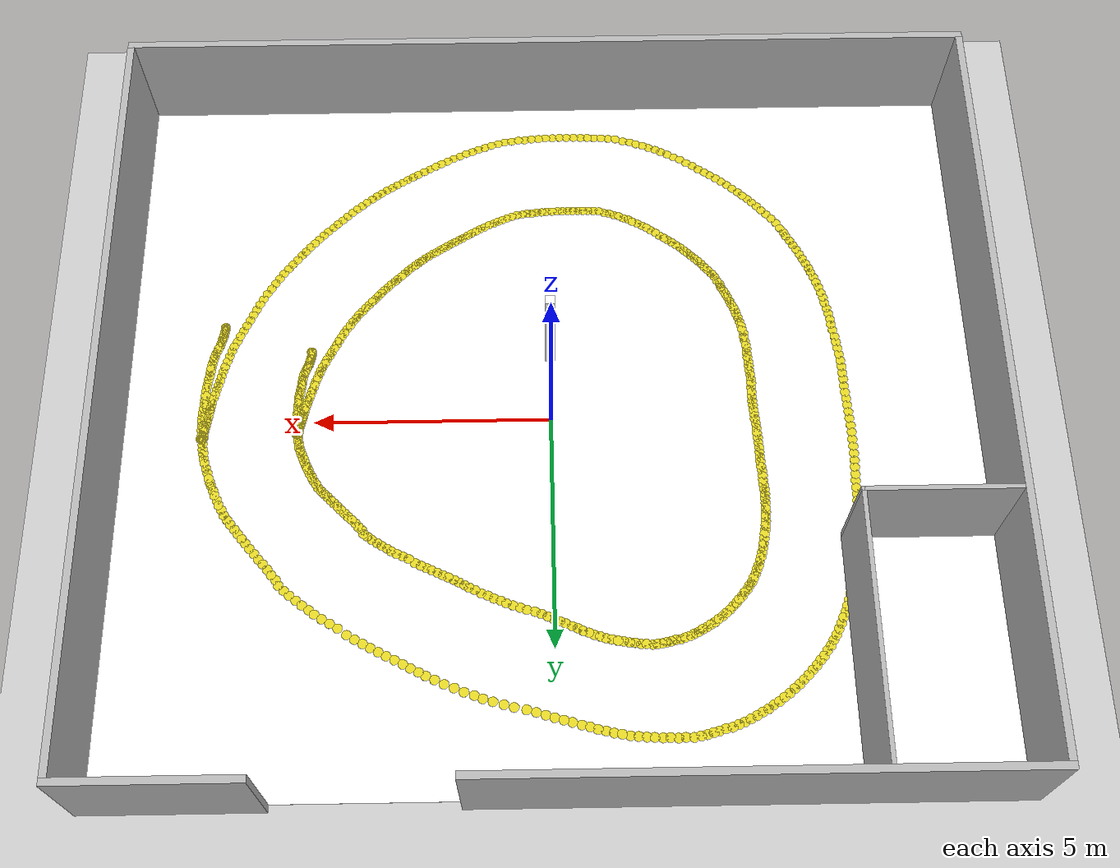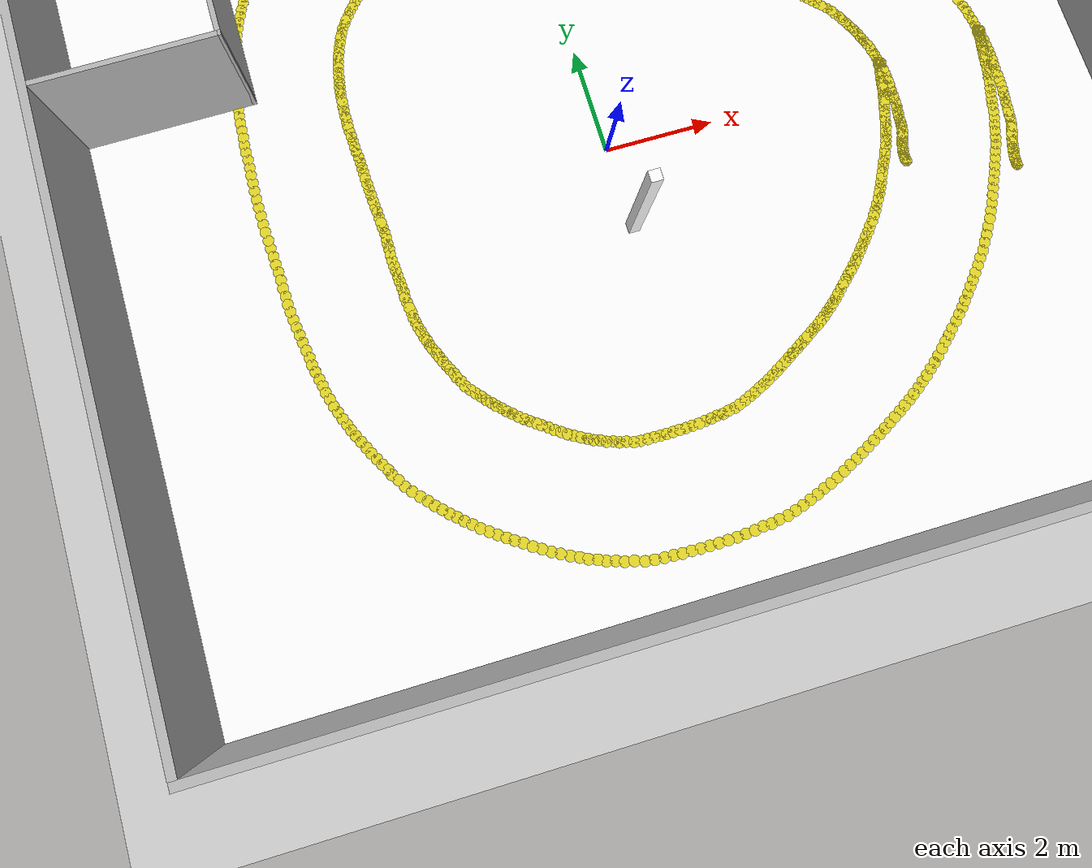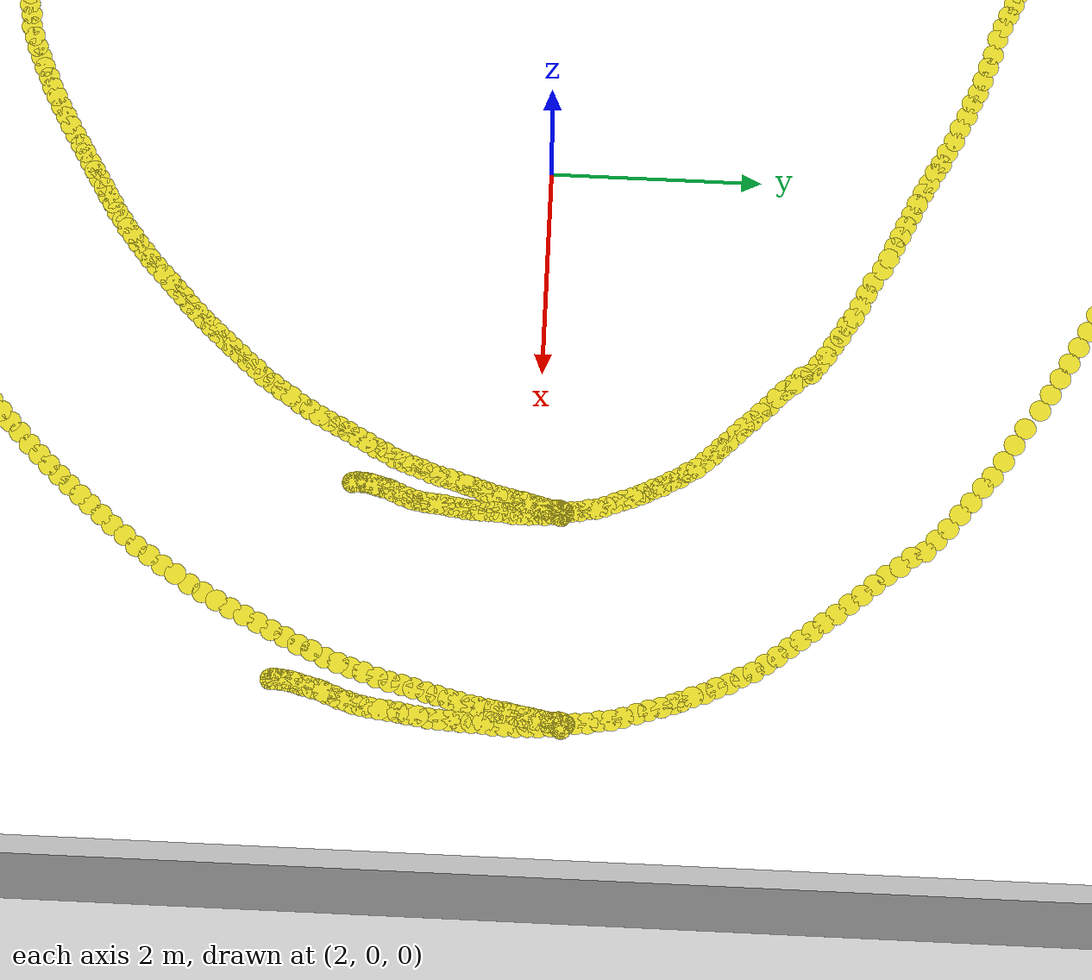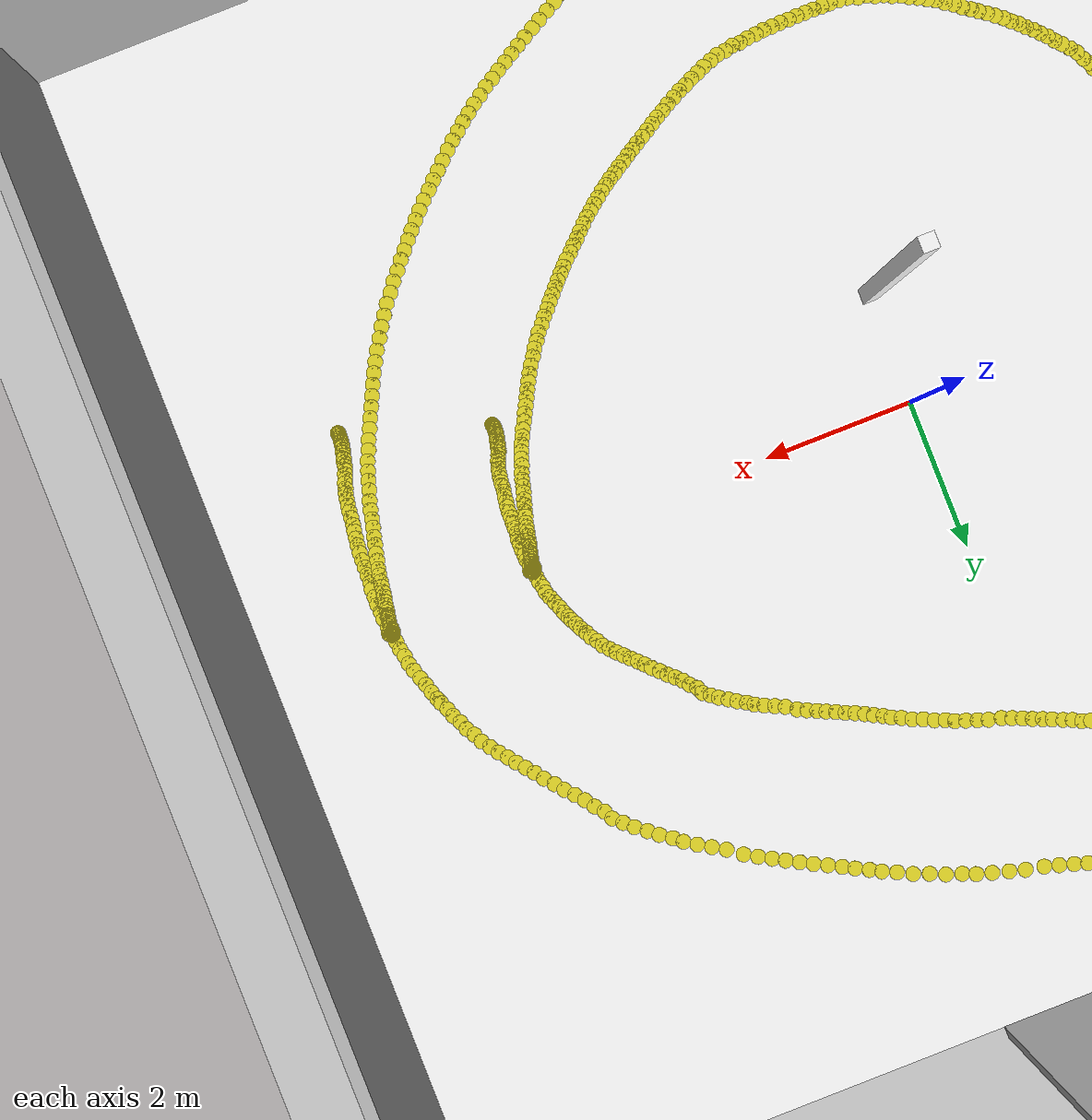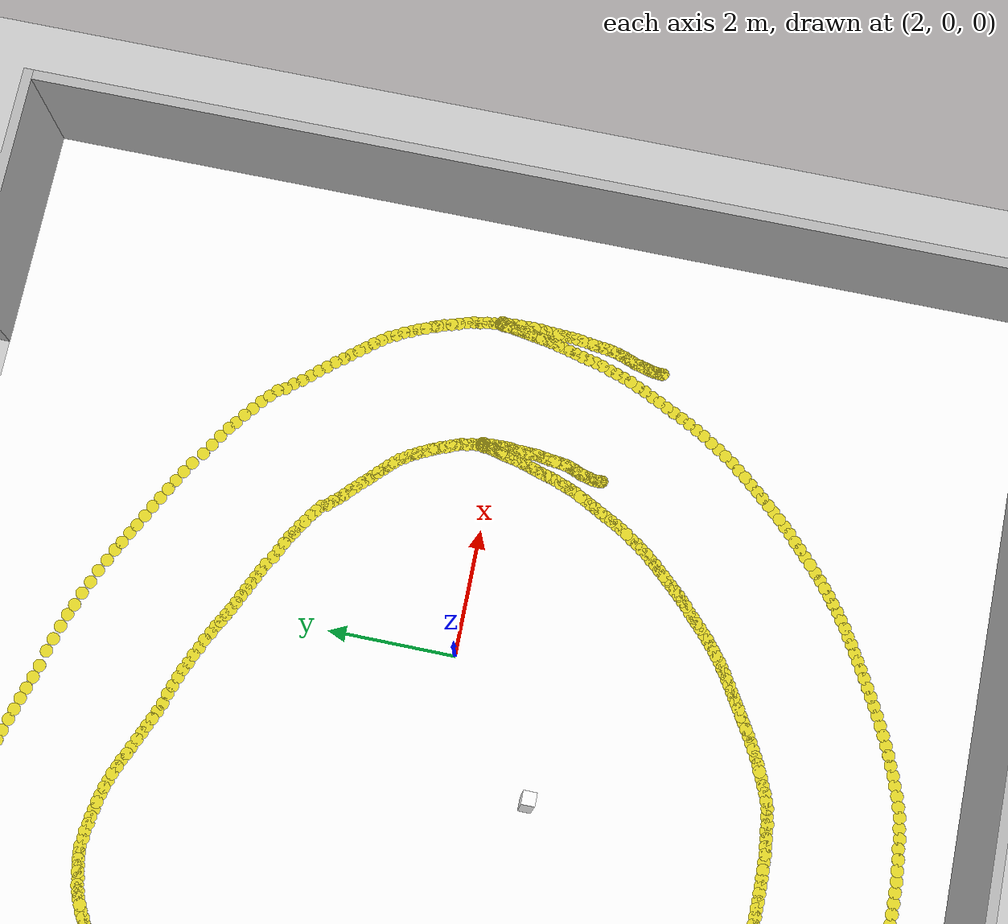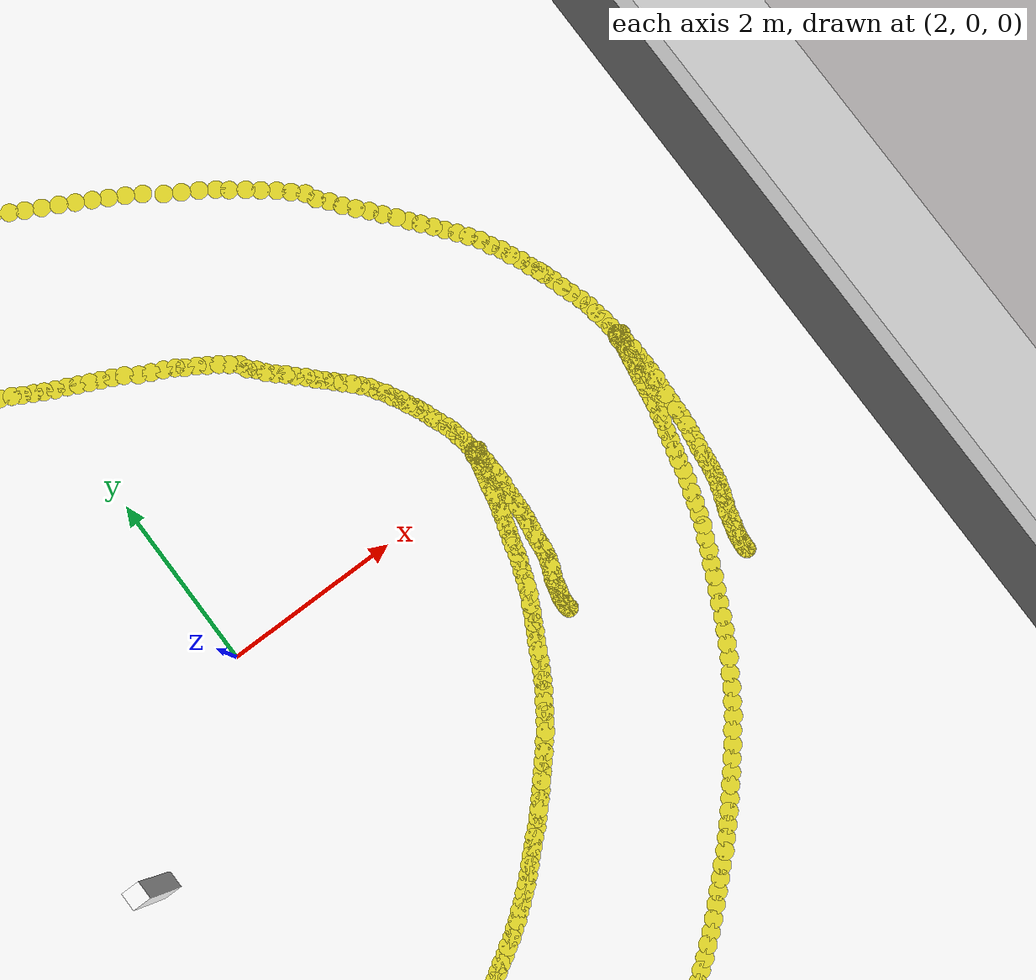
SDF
<?xml version="1.0" ?>

<sdf version="1.4">
  <world name="default">

    <include>
      <uri>model://ground_plane</uri>
    </include>

    <include>
      <uri>model://sun</uri>
    </include>

    <include>
      <uri>model://highbay</uri>
    </include>

    <include>
      <uri>model://loop_1</uri>
    </include>

  </world>
</sdf>

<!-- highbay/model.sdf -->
<sdf version="1.6">
<model name='highbay'>
  <static>true</static>
  <pose frame=''>0 0 0 0 -0 0</pose>

    <link name='Wall_1'>
      <collision name='Wall_1_Collision'>
        <geometry>
          <box>
            <size>3.6576 .15239 2.5</size>
          </box>
        </geometry>
        <pose frame=''>0 0 1.25 0 -0 0</pose>
      </collision>
      <visual name='Wall_1_Visual'>
        <pose frame=''>0 0 1.25 0 -0 0</pose>
        <geometry>
          <box>
            <size>3.6576 .15239 2.5</size>
          </box>
        </geometry>
        <material>
          <script>

            <uri>model://highbay/materials/scripts</uri>
            <uri>model://highbay/materials/textures</uri>
            <name>RepeatedTexture</name>

          </script>
        </material>
      </visual>
      <pose frame=''>7.323594 8.05 0 0 -0 0</pose>
    </link>

    <link name='Wall_1_5'>
      <collision name='Wall_1_5_Collision'>
        <geometry>
          <box>
            <size>10.9728 .15239 2.5</size>
          </box>
        </geometry>
        <pose frame=''>0 0 1.25 0 -0 0</pose>
      </collision>
      <visual name='Wall_1_5_Visual'>
        <pose frame=''>0 0 1.25 0 -0 0</pose>
        <geometry>
          <box>
            <size>10.9728 .15239 2.5</size>
          </box>
        </geometry>
        <material>
          <script>
            <uri>model://highbay/materials/scripts</uri>
            <uri>model://highbay/materials/textures</uri>
            <name>RepeatedTexture</name>
          </script>
        </material>
      </visual>
      <pose frame=''>-3.665994 8.05 0 0 -0 0</pose>
    </link>

    <link name='Wall_2'>
      <collision name='Wall_2_Collision'>
        <geometry>
          <box>
            <size>15.954375 .15239 2.5</size>
          </box>
        </geometry>
        <pose frame=''>0 0 1.25 0 -0 0</pose>
      </collision>
      <visual name='Wall_2_Visual'>
        <pose frame=''>0 0 1.25 0 -0 0</pose>
        <geometry>
          <box>
            <size>15.954375 .15239 2.5</size>
          </box>
        </geometry>
        <material>
          <script>
            <uri>model://highbay/materials/scripts</uri>
            <uri>model://highbay/materials/textures</uri>
            <name>RepeatedTexture</name>
          </script>
        </material>
      </visual>
      <pose frame=''>-9.076199 0 0 0 -0 1.57079632679</pose>
    </link>

    <link name='Wall_3'>
      <collision name='Wall_3_Collision'>
        <geometry>
          <box>
            <size>18.288 .15239 2.5</size>
          </box>
        </geometry>
        <pose frame=''>0 0 1.25 0 -0 0</pose>
      </collision>
      <visual name='Wall_3_Visual'>
        <pose frame=''>0 0 1.25 0 -0 0</pose>
        <geometry>
          <box>
            <size>18.288 .15239 2.5</size>
          </box>
        </geometry>
        <material>
          <script>
            <uri>model://highbay/materials/scripts</uri>
            <uri>model://highbay/materials/textures</uri>
            <name>RepeatedTexture</name>
          </script>
        </material>
      </visual>
      <pose frame=''>0 -8.05 0 0 -0 0</pose>
    </link>

    <link name='Wall_4'>
      <collision name='Wall_4_Collision'>
        <geometry>
          <box>
            <size>15.954375 .15239 2.5</size>
          </box>
        </geometry>
        <pose frame=''>0 0 1.25 0 -0 0</pose>
      </collision>
      <visual name='Wall_4_Visual'>
        <pose frame=''>0 0 1.25 0 -0 0</pose>
        <geometry>
          <box>
            <size>15.954375 .15239 2.5</size>
          </box>
        </geometry>
        <material>
          <script>
            <uri>model://highbay/materials/scripts</uri>
            <uri>model://highbay/materials/textures</uri>
            <name>RepeatedTexture</name>
          </script>
        </material>
      </visual>
      <pose frame=''>9.076199 0 0 0 -0 1.57079632679</pose>
    </link>

    <link name='Wall_5'>
      <collision name='Wall_5_Collision'>
        <geometry>
          <box>
            <size>3.07975 .092075 2.5</size>
          </box>
        </geometry>
        <pose frame=''>0 0 1.25 0 -0 0</pose>
      </collision>
      <visual name='Wall_5_Visual'>
        <pose frame=''>0 0 1.25 0 -0 0</pose>
        <geometry>
          <box>
            <size>3.07975 .092075 2.5</size>
          </box>
        </geometry>
        <material>
          <script>
            <uri>model://highbay/materials/scripts</uri>
            <uri>model://highbay/materials/textures</uri>
            <name>RepeatedTexture</name>
          </script>
        </material>
      </visual>
      <pose frame=''>-7.460129 2.7144175 0 0 -0 0</pose>
    </link>

  <link name='Wall_6'>
    <collision name='Wall_6_Collision'>
      <geometry>
        <box>
          <size>.092075 .092075 2.5</size>
        </box>
      </geometry>
      <pose frame=''>0 0 1.25 0 -0 0</pose>
    </collision>
    <visual name='Wall_6_Visual'>
      <pose frame=''>0 0 1.25 0 -0 0</pose>
      <geometry>
        <box>
          <size>.092075 .092075 2.5</size>
        </box>
      </geometry>
      <material>
        <script>
          <uri>model://highbay/materials/scripts</uri>
          <uri>model://highbay/materials/textures</uri>
          <name>RepeatedTexture</name>
        </script>
      </material>
    </visual>
    <pose frame=''>-5.911379 2.7144175 0 0 -0 1.5708</pose>
  </link>

  <link name='Wall_7'>
    <collision name='Wall_7_Collision'>
      <geometry>
        <box>
          <size>5.21335 .092075 2.5</size>
        </box>
      </geometry>
      <pose frame=''>0 0 1.25 0 -0 0</pose>
    </collision>
    <visual name='Wall_7_Visual'>
      <pose frame=''>0 0 1.25 0 -0 0</pose>
      <geometry>
        <box>
          <size>5.21335 .092075 2.5</size>
        </box>
      </geometry>
      <material>
        <script>
          <uri>model://highbay/materials/scripts</uri>
          <uri>model://highbay/materials/textures</uri>
          <name>RepeatedTexture</name>
        </script>
      </material>
    </visual>
    <pose frame=''>-5.911379 5.36713 0 0 -0 1.5708</pose>
  </link>

  <link name='Pillar'>
    <collision name='Pillar_Collision'>
      <geometry>
        <box>
          <size>0.2 0.2 2.5</size>
        </box>
      </geometry>
      <pose frame=''>0 0 1.25 0 -0 0</pose>
    </collision>
    <visual name='Pillar_Visual'>
      <pose frame=''>0 0 1.25 0 -0 0</pose>
      <geometry>
        <box>
          <size>0.2 0.2 2.5</size>
        </box>
      </geometry>
      <material>
        <script>
          <uri>model://highbay/materials/scripts</uri>
          <uri>model://highbay/materials/textures</uri>
          <name>RepeatedTexture</name>
        </script>
        <ambient>1 1 1 1</ambient>
      </material>
      <meta>
        <layer>0</layer>
      </meta>
    </visual>
    <pose frame=''>.008394 -1.5 0 0 -0 -1.5708</pose>
  </link>

  <link name='Floor'>
    <collision name='Floor_Collision'>
      <geometry>
        <box>
          <size>18.288  15.954375 .005</size>
        </box>
      </geometry>
      <pose frame=''>0 0 1.25 0 -0 0</pose>
    </collision>
    <visual name='Floor_Visual'>
      <pose frame=''>0 0 1.25 0 -0 0</pose>
      <geometry>
        <box>
          <size>18.288  15.954375 .005</size>
        </box>
      </geometry>
      <material>
        <script>
          <uri>model://highbay/materials/scripts</uri>
          <uri>model://highbay/materials/textures</uri>
          <name>RepeatedFloor</name>
        </script>
        <ambient>1 1 1 1</ambient>
      </material>
      <meta>
        <layer>0</layer>
      </meta>
    </visual>
    <pose frame=''>0 0 -1.25 0 -0 0</pose>
  </link>

</model>
</sdf>

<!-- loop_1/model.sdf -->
<sdf version="1.6">
	<model name="highbay_loop1">
		<static>true</static>
		<link name="inner_loop">

		<visual name="inner_point0">
			<pose>5.38060227608 0.241318782437 0.01 0 0 0</pose>
			<geometry>
				<cylinder>
					<radius>0.1</radius>
					<length>0.001</length>
				</cylinder>
			</geometry>
			<material>
				<script>
					<uri>file://media/materials/scripts/gazebo.material</uri>
					<name>Gazebo/Yellow</name>
				</script>
			</material>
		</visual>

		<visual name="outer_point0">
			<pose>7.3785938036 0.33092824584 0.01 0 0 0</pose>
			<geometry>
				<cylinder>
					<radius>0.1</radius>
					<length>0.001</length>
				</cylinder>
			</geometry>
			<material>
				<script>
					<uri>file://media/materials/scripts/gazebo.material</uri>
					<name>Gazebo/Yellow</name>
				</script>
			</material>
		</visual>

		<visual name="inner_point1">
			<pose>5.37865269065 0.241760774014 0.01 0 0 0</pose>
			<geometry>
				<cylinder>
					<radius>0.1</radius>
					<length>0.001</length>
				</cylinder>
			</geometry>
			<material>
				<script>
					<uri>file://media/materials/scripts/gazebo.material</uri>
					<name>Gazebo/Yellow</name>
				</script>
			</material>
		</visual>

		<visual name="outer_point1">
			<pose>7.37663540587 0.331566507063 0.01 0 0 0</pose>
			<geometry>
				<cylinder>
					<radius>0.1</radius>
					<length>0.001</length>
				</cylinder>
			</geometry>
			<material>
				<script>
					<uri>file://media/materials/scripts/gazebo.material</uri>
					<name>Gazebo/Yellow</name>
				</script>
			</material>
		</visual>

		<visual name="inner_point2">
			<pose>5.37792687375 0.242230459266 0.01 0 0 0</pose>
			<geometry>
				<cylinder>
					<radius>0.1</radius>
					<length>0.001</length>
				</cylinder>
			</geometry>
			<material>
				<script>
					<uri>file://media/materials/scripts/gazebo.material</uri>
					<name>Gazebo/Yellow</name>
				</script>
			</material>
		</visual>

		<visual name="outer_point2">
			<pose>7.3759012092 0.332222430566 0.01 0 0 0</pose>
			<geometry>
				<cylinder>
					<radius>0.1</radius>
					<length>0.001</length>
				</cylinder>
			</geometry>
			<material>
				<script>
					<uri>file://media/materials/scripts/gazebo.material</uri>
					<name>Gazebo/Yellow</name>
				</script>
			</material>
		</visual>

		<visual name="inner_point3">
			<pose>5.37782465935 0.24323619331 0.01 0 0 0</pose>
			<geometry>
				<cylinder>
					<radius>0.1</radius>
					<length>0.001</length>
				</cylinder>
			</geometry>
			<material>
				<script>
					<uri>file://media/materials/scripts/gazebo.material</uri>
					<name>Gazebo/Yellow</name>
				</script>
			</material>
		</visual>

		<visual name="outer_point3">
			<pose>7.37578208716 0.333602761563 0.01 0 0 0</pose>
			<geometry>
				<cylinder>
					<radius>0.1</radius>
					<length>0.001</length>
				</cylinder>
			</geometry>
			<material>
				<script>
					<uri>file://media/materials/scripts/gazebo.material</uri>
					<name>Gazebo/Yellow</name>
				</script>
			</material>
		</visual>

		<visual name="inner_point4">
			<pose>5.37704955333 0.243157482016 0.01 0 0 0</pose>
			<geometry>
				<cylinder>
					<radius>0.1</radius>
					<length>0.001</length>
				</cylinder>
			</geometry>
			<material>
				<script>
					<uri>file://media/materials/scripts/gazebo.material</uri>
					<name>Gazebo/Yellow</name>
				</script>
			</material>
		</visual>

		<visual name="outer_point4">
			<pose>7.37500771322 0.333507862928 0.01 0 0 0</pose>
			<geometry>
				<cylinder>
					<radius>0.1</radius>
					<length>0.001</length>
				</cylinder>
			</geometry>
			<material>
				<script>
					<uri>file://media/materials/scripts/gazebo.material</uri>
					<name>Gazebo/Yellow</name>
				</script>
			</material>
		</visual>

		<visual name="inner_point5">
			<pose>5.37785899281 0.243060758093 0.01 0 0 0</pose>
			<geometry>
				<cylinder>
					<radius>0.1</radius>
					<length>0.001</length>
				</cylinder>
			</geometry>
			<material>
				<script>
					<uri>file://media/materials/scripts/gazebo.material</uri>
					<name>Gazebo/Yellow</name>
				</script>
			</material>
		</visual>

		<visual name="outer_point5">
			<pose>7.37581938748 0.333361706634 0.01 0 0 0</pose>
			<geometry>
				<cylinder>
					<radius>0.1</radius>
					<length>0.001</length>
				</cylinder>
			</geometry>
			<material>
				<script>
					<uri>file://media/materials/scripts/gazebo.material</uri>
					<name>Gazebo/Yellow</name>
				</script>
			</material>
		</visual>

		<visual name="inner_point6">
			<pose>5.37763214889 0.243172502615 0.01 0 0 0</pose>
			<geometry>
				<cylinder>
					<radius>0.1</radius>
					<length>0.001</length>
				</cylinder>
			</geometry>
			<material>
				<script>
					<uri>file://media/materials/scripts/gazebo.material</uri>
					<name>Gazebo/Yellow</name>
				</script>
			</material>
		</visual>

		<visual name="outer_point6">
			<pose>7.37559049866 0.333518684462 0.01 0 0 0</pose>
			<geometry>
				<cylinder>
					<radius>0.1</radius>
					<length>0.001</length>
				</cylinder>
			</geometry>
			<material>
				<script>
					<uri>file://media/materials/scripts/gazebo.material</uri>
					<name>Gazebo/Yellow</name>
				</script>
			</material>
		</visual>

		<visual name="inner_point7">
			<pose>5.3789299904 0.242003470515 0.01 0 0 0</pose>
			<geometry>
				<cylinder>
					<radius>0.1</radius>
					<length>0.001</length>
				</cylinder>
			</geometry>
			<material>
				<script>
					<uri>file://media/materials/scripts/gazebo.material</uri>
					<name>Gazebo/Yellow</name>
				</script>
			</material>
		</visual>

		<visual name="outer_point7">
			<pose>7.37690886764 0.331894549813 0.01 0 0 0</pose>
			<geometry>
				<cylinder>
					<radius>0.1</radius>
					<length>0.001</length>
				</cylinder>
			</geometry>
			<material>
				<script>
					<uri>file://media/materials/scripts/gazebo.material</uri>
					<name>Gazebo/Yellow</name>
				</script>
			</material>
		</visual>

		<visual name="inner_point8">
			<pose>5.37895705161 0.241944125189 0.01 0 0 0</pose>
			<geometry>
				<cylinder>
					<radius>0.1</radius>
					<length>0.001</length>
				</cylinder>
			</geometry>
			<material>
				<script>
					<uri>file://media/materials/scripts/gazebo.material</uri>
					<name>Gazebo/Yellow</name>
				</script>
			</material>
		</visual>

		<visual name="outer_point8">
			<pose>7.37693693877 0.331812754238 0.01 0 0 0</pose>
			<geometry>
				<cylinder>
					<radius>0.1</radius>
					<length>0.001</length>
				</cylinder>
			</geometry>
			<material>
				<script>
					<uri>file://media/materials/scripts/gazebo.material</uri>
					<name>Gazebo/Yellow</name>
				</script>
			</material>
		</visual>

		<visual name="inner_point9">
			<pose>5.37840722004 0.242370672514 0.01 0 0 0</pose>
			<geometry>
				<cylinder>
					<radius>0.1</radius>
					<length>0.001</length>
				</cylinder>
			</geometry>
			<material>
				<script>
					<uri>file://media/materials/scripts/gazebo.material</uri>
					<name>Gazebo/Yellow</name>
				</script>
			</material>
		</visual>

		<visual name="outer_point9">
			<pose>7.37637957497 0.332406603881 0.01 0 0 0</pose>
			<geometry>
				<cylinder>
					<radius>0.1</radius>
					<length>0.001</length>
				</cylinder>
			</geometry>
			<material>
				<script>
					<uri>file://media/materials/scripts/gazebo.material</uri>
					<name>Gazebo/Yellow</name>
				</script>
			</material>
		</visual>

		<visual name="inner_point10">
			<pose>5.37855283253 0.242056601676 0.01 0 0 0</pose>
			<geometry>
				<cylinder>
					<radius>0.1</radius>
					<length>0.001</length>
				</cylinder>
			</geometry>
			<material>
				<script>
					<uri>file://media/materials/scripts/gazebo.material</uri>
					<name>Gazebo/Yellow</name>
				</script>
			</material>
		</visual>

		<visual name="outer_point10">
			<pose>7.37653054039 0.33197366845 0.01 0 0 0</pose>
			<geometry>
				<cylinder>
					<radius>0.1</radius>
					<length>0.001</length>
				</cylinder>
			</geometry>
			<material>
				<script>
					<uri>file://media/materials/scripts/gazebo.material</uri>
					<name>Gazebo/Yellow</name>
				</script>
			</material>
		</visual>

		<visual name="inner_point11">
			<pose>5.37670492436 0.241894038708 0.01 0 0 0</pose>
			<geometry>
				<cylinder>
					<radius>0.1</radius>
					<length>0.001</length>
				</cylinder>
			</geometry>
			<material>
				<script>
					<uri>file://media/materials/scripts/gazebo.material</uri>
					<name>Gazebo/Yellow</name>
				</script>
			</material>
		</visual>

		<visual name="outer_point11">
			<pose>7.37468395716 0.331781660271 0.01 0 0 0</pose>
			<geometry>
				<cylinder>
					<radius>0.1</radius>
					<length>0.001</length>
				</cylinder>
			</geometry>
			<material>
				<script>
					<uri>file://media/materials/scripts/gazebo.material</uri>
					<name>Gazebo/Yellow</name>
				</script>
			</material>
		</visual>

		<visual name="inner_point12">
			<pose>5.37615775781 0.241891318389 0.01 0 0 0</pose>
			<geometry>
				<cylinder>
					<radius>0.1</radius>
					<length>0.001</length>
				</cylinder>
			</geometry>
			<material>
				<script>
					<uri>file://media/materials/scripts/gazebo.material</uri>
					<name>Gazebo/Yellow</name>
				</script>
			</material>
		</visual>

		<visual name="outer_point12">
			<pose>7.37413642523 0.33178706099 0.01 0 0 0</pose>
			<geometry>
				<cylinder>
					<radius>0.1</radius>
					<length>0.001</length>
				</cylinder>
			</geometry>
			<material>
				<script>
					<uri>file://media/materials/scripts/gazebo.material</uri>
					<name>Gazebo/Yellow</name>
				</script>
			</material>
		</visual>

		<visual name="inner_point13">
			<pose>5.37371238005 0.242879403152 0.01 0 0 0</pose>
			<geometry>
				<cylinder>
					<radius>0.1</radius>
					<length>0.001</length>
				</cylinder>
			</geometry>
			<material>
				<script>
					<uri>file://media/materials/scripts/gazebo.material</uri>
					<name>Gazebo/Yellow</name>
				</script>
			</material>
		</visual>

		<visual name="outer_point13">
			<pose>7.37167267314 0.333182599376 0.01 0 0 0</pose>
			<geometry>
				<cylinder>
					<radius>0.1</radius>
					<length>0.001</length>
				</cylinder>
			</geometry>
			<material>
				<script>
					<uri>file://media/materials/scripts/gazebo.material</uri>
					<name>Gazebo/Yellow</name>
				</script>
			</material>
		</visual>

		<visual name="inner_point14">
			<pose>5.37282012618 0.243144285189 0.01 0 0 0</pose>
			<geometry>
				<cylinder>
					<radius>0.1</radius>
					<length>0.001</length>
				</cylinder>
			</geometry>
			<material>
				<script>
					<uri>file://media/materials/scripts/gazebo.material</uri>
					<name>Gazebo/Yellow</name>
				</script>
			</material>
		</visual>

		<visual name="outer_point14">
			<pose>7.37077529674 0.333560746261 0.01 0 0 0</pose>
			<geometry>
				<cylinder>
					<radius>0.1</radius>
					<length>0.001</length>
				</cylinder>
			</geometry>
			<material>
				<script>
					<uri>file://media/materials/scripts/gazebo.material</uri>
					<name>Gazebo/Yellow</name>
				</script>
			</material>
		</visual>

		<visual name="inner_point15">
			<pose>5.37190415555 0.244385650725 0.01 0 0 0</pose>
			<geometry>
				<cylinder>
					<radius>0.1</radius>
					<length>0.001</length>
				</cylinder>
			</geometry>
			<material>
				<script>
					<uri>file://media/materials/scripts/gazebo.material</uri>
					<name>Gazebo/Yellow</name>
				</script>
			</material>
		</visual>

		<visual name="outer_point15">
			<pose>7.36983772217 0.335278243118 0.01 0 0 0</pose>
			<geometry>
				<cylinder>
					<radius>0.1</radius>
					<length>0.001</length>
				</cylinder>
			</geometry>
			<material>
				<script>
					<uri>file://media/materials/scripts/gazebo.material</uri>
					<name>Gazebo/Yellow</name>
				</script>
			</material>
		</visual>

		<visual name="inner_point16">
			<pose>5.37025455505 0.245234632305 0.01 0 0 0</pose>
			<geometry>
				<cylinder>
					<radius>0.1</radius>
					<length>0.001</length>
				</cylinder>
			</geometry>
			<material>
				<script>
					<uri>file://media/materials/scripts/gazebo.material</uri>
					<name>Gazebo/Yellow</name>
				</script>
			</material>
		</visual>

		<visual name="outer_point16">
			<pose>7.3681724853 0.336470283051 0.01 0 0 0</pose>
			<geometry>
				<cylinder>
					<radius>0.1</radius>
					<length>0.001</length>
				</cylinder>
			</geometry>
			<material>
				<script>
					<uri>file://media/materials/scripts/gazebo.material</uri>
					<name>Gazebo/Yellow</name>
				</script>
			</material>
		</visual>

		<visual name="inner_point17">
			<pose>5.3677655241 0.246986567285 0.01 0 0 0</pose>
			<geometry>
				<cylinder>
					<radius>0.1</radius>
					<length>0.001</length>
				</cylinder>
			</geometry>
			<material>
				<script>
					<uri>file://media/materials/scripts/gazebo.material</uri>
					<name>Gazebo/Yellow</name>
				</script>
			</material>
		</visual>

		<visual name="outer_point17">
			<pose>7.36565169121 0.338915144274 0.01 0 0 0</pose>
			<geometry>
				<cylinder>
					<radius>0.1</radius>
					<length>0.001</length>
				</cylinder>
			</geometry>
			<material>
				<script>
					<uri>file://media/materials/scripts/gazebo.material</uri>
					<name>Gazebo/Yellow</name>
				</script>
			</material>
		</visual>

		<visual name="inner_point18">
			<pose>5.36562624796 0.248028890037 0.01 0 0 0</pose>
			<geometry>
				<cylinder>
					<radius>0.1</radius>
					<length>0.001</length>
				</cylinder>
			</geometry>
			<material>
				<script>
					<uri>file://media/materials/scripts/gazebo.material</uri>
					<name>Gazebo/Yellow</name>
				</script>
			</material>
		</visual>

		<visual name="outer_point18">
			<pose>7.36349286715 0.340381323303 0.01 0 0 0</pose>
			<geometry>
				<cylinder>
					<radius>0.1</radius>
					<length>0.001</length>
				</cylinder>
			</geometry>
			<material>
				<script>
					<uri>file://media/materials/scripts/gazebo.material</uri>
					<name>Gazebo/Yellow</name>
				</script>
			</material>
		</visual>

		<visual name="inner_point19">
			<pose>5.36262770256 0.249422910205 0.01 0 0 0</pose>
			<geometry>
				<cylinder>
					<radius>0.1</radius>
					<length>0.001</length>
				</cylinder>
			</geometry>
			<material>
				<script>
					<uri>file://media/materials/scripts/gazebo.material</uri>
					<name>Gazebo/Yellow</name>
				</script>
			</material>
		</visual>

		<visual name="outer_point19">
			<pose>7.36046790297 0.342345101442 0.01 0 0 0</pose>
			<geometry>
				<cylinder>
					<radius>0.1</radius>
					<length>0.001</length>
				</cylinder>
			</geometry>
			<material>
				<script>
					<uri>file://media/materials/scripts/gazebo.material</uri>
					<name>Gazebo/Yellow</name>
				</script>
			</material>
		</visual>

		<visual name="inner_point20">
			<pose>5.36077810318 0.250495387309 0.01 0 0 0</pose>
			<geometry>
				<cylinder>
					<radius>0.1</radius>
					<length>0.001</length>
				</cylinder>
			</geometry>
			<material>
				<script>
					<uri>file://media/materials/scripts/gazebo.material</uri>
					<name>Gazebo/Yellow</name>
				</script>
			</material>
		</visual>

		<visual name="outer_point20">
			<pose>7.3585982195 0.343848388344 0.01 0 0 0</pose>
			<geometry>
				<cylinder>
					<radius>0.1</radius>
					<length>0.001</length>
				</cylinder>
			</geometry>
			<material>
				<script>
					<uri>file://media/materials/scripts/gazebo.material</uri>
					<name>Gazebo/Yellow</name>
				</script>
			</material>
		</visual>

		<visual name="inner_point21">
			<pose>5.36037797095 0.250484757265 0.01 0 0 0</pose>
			<geometry>
				<cylinder>
					<radius>0.1</radius>
					<length>0.001</length>
				</cylinder>
			</geometry>
			<material>
				<script>
					<uri>file://media/materials/scripts/gazebo.material</uri>
					<name>Gazebo/Yellow</name>
				</script>
			</material>
		</visual>

		<visual name="outer_point21">
			<pose>7.35819794708 0.34384075837 0.01 0 0 0</pose>
			<geometry>
				<cylinder>
					<radius>0.1</radius>
					<length>0.001</length>
				</cylinder>
			</geometry>
			<material>
				<script>
					<uri>file://media/materials/scripts/gazebo.material</uri>
					<name>Gazebo/Yellow</name>
				</script>
			</material>
		</visual>

		<visual name="inner_point22">
			<pose>5.35856724392 0.251528598303 0.01 0 0 0</pose>
			<geometry>
				<cylinder>
					<radius>0.1</radius>
					<length>0.001</length>
				</cylinder>
			</geometry>
			<material>
				<script>
					<uri>file://media/materials/scripts/gazebo.material</uri>
					<name>Gazebo/Yellow</name>
				</script>
			</material>
		</visual>

		<visual name="outer_point22">
			<pose>7.35636755925 0.345304395103 0.01 0 0 0</pose>
			<geometry>
				<cylinder>
					<radius>0.1</radius>
					<length>0.001</length>
				</cylinder>
			</geometry>
			<material>
				<script>
					<uri>file://media/materials/scripts/gazebo.material</uri>
					<name>Gazebo/Yellow</name>
				</script>
			</material>
		</visual>

		<visual name="inner_point23">
			<pose>5.35631641219 0.25237292428 0.01 0 0 0</pose>
			<geometry>
				<cylinder>
					<radius>0.1</radius>
					<length>0.001</length>
				</cylinder>
			</geometry>
			<material>
				<script>
					<uri>file://media/materials/scripts/gazebo.material</uri>
					<name>Gazebo/Yellow</name>
				</script>
			</material>
		</visual>

		<visual name="outer_point23">
			<pose>7.35410010117 0.346502261097 0.01 0 0 0</pose>
			<geometry>
				<cylinder>
					<radius>0.1</radius>
					<length>0.001</length>
				</cylinder>
			</geometry>
			<material>
				<script>
					<uri>file://media/materials/scripts/gazebo.material</uri>
					<name>Gazebo/Yellow</name>
				</script>
			</material>
		</visual>

		<visual name="inner_point24">
			<pose>5.35465429369 0.253137870809 0.01 0 0 0</pose>
			<geometry>
				<cylinder>
					<radius>0.1</radius>
					<length>0.001</length>
				</cylinder>
			</geometry>
			<material>
				<script>
					<uri>file://media/materials/scripts/gazebo.material</uri>
					<name>Gazebo/Yellow</name>
				</script>
			</material>
		</visual>

		<visual name="outer_point24">
			<pose>7.3524231673 0.347581121727 0.01 0 0 0</pose>
			<geometry>
				<cylinder>
					<radius>0.1</radius>
					<length>0.001</length>
				</cylinder>
			</geometry>
			<material>
				<script>
					<uri>file://media/materials/scripts/gazebo.material</uri>
					<name>Gazebo/Yellow</name>
				</script>
			</material>
		</visual>

		<visual name="inner_point25">
			<pose>5.35448140481 0.252985049601 0.01 0 0 0</pose>
			<geometry>
				<cylinder>
					<radius>0.1</radius>
					<length>0.001</length>
				</cylinder>
			</geometry>
			<material>
				<script>
					<uri>file://media/materials/scripts/gazebo.material</uri>
					<name>Gazebo/Yellow</name>
				</script>
			</material>
		</visual>

		<visual name="outer_point25">
			<pose>7.35225282334 0.34737445227 0.01 0 0 0</pose>
			<geometry>
				<cylinder>
					<radius>0.1</radius>
					<length>0.001</length>
				</cylinder>
			</geometry>
			<material>
				<script>
					<uri>file://media/materials/scripts/gazebo.material</uri>
					<name>Gazebo/Yellow</name>
				</script>
			</material>
		</visual>

		<visual name="inner_point26">
			<pose>5.35329338027 0.253475440532 0.01 0 0 0</pose>
			<geometry>
				<cylinder>
					<radius>0.1</radius>
					<length>0.001</length>
				</cylinder>
			</geometry>
			<material>
				<script>
					<uri>file://media/materials/scripts/gazebo.material</uri>
					<name>Gazebo/Yellow</name>
				</script>
			</material>
		</visual>

		<visual name="outer_point26">
			<pose>7.35105517365 0.348068341516 0.01 0 0 0</pose>
			<geometry>
				<cylinder>
					<radius>0.1</radius>
					<length>0.001</length>
				</cylinder>
			</geometry>
			<material>
				<script>
					<uri>file://media/materials/scripts/gazebo.material</uri>
					<name>Gazebo/Yellow</name>
				</script>
			</material>
		</visual>

		<visual name="inner_point27">
			<pose>5.35317529842 0.25385357927 0.01 0 0 0</pose>
			<geometry>
				<cylinder>
					<radius>0.1</radius>
					<length>0.001</length>
				</cylinder>
			</geometry>
			<material>
				<script>
					<uri>file://media/materials/scripts/gazebo.material</uri>
					<name>Gazebo/Yellow</name>
				</script>
			</material>
		</visual>

		<visual name="outer_point27">
			<pose>7.35093032121 0.348589364065 0.01 0 0 0</pose>
			<geometry>
				<cylinder>
					<radius>0.1</radius>
					<length>0.001</length>
				</cylinder>
			</geometry>
			<material>
				<script>
					<uri>file://media/materials/scripts/gazebo.material</uri>
					<name>Gazebo/Yellow</name>
				</script>
			</material>
		</visual>

		<visual name="inner_point28">
			<pose>5.3526584049 0.254094320705 0.01 0 0 0</pose>
			<geometry>
				<cylinder>
					<radius>0.1</radius>
					<length>0.001</length>
				</cylinder>
			</geometry>
			<material>
				<script>
					<uri>file://media/materials/scripts/gazebo.material</uri>
					<name>Gazebo/Yellow</name>
				</script>
			</material>
		</visual>

		<visual name="outer_point28">
			<pose>7.35040874112 0.348928882566 0.01 0 0 0</pose>
			<geometry>
				<cylinder>
					<radius>0.1</radius>
					<length>0.001</length>
				</cylinder>
			</geometry>
			<material>
				<script>
					<uri>file://media/materials/scripts/gazebo.material</uri>
					<name>Gazebo/Yellow</name>
				</script>
			</material>
		</visual>

		<visual name="inner_point29">
			<pose>5.35301578362 0.25423932991 0.01 0 0 0</pose>
			<geometry>
				<cylinder>
					<radius>0.1</radius>
					<length>0.001</length>
				</cylinder>
			</geometry>
			<material>
				<script>
					<uri>file://media/materials/scripts/gazebo.material</uri>
					<name>Gazebo/Yellow</name>
				</script>
			</material>
		</visual>

		<visual name="outer_point29">
			<pose>7.35076385593 0.349121570457 0.01 0 0 0</pose>
			<geometry>
				<cylinder>
					<radius>0.1</radius>
					<length>0.001</length>
				</cylinder>
			</geometry>
			<material>
				<script>
					<uri>file://media/materials/scripts/gazebo.material</uri>
					<name>Gazebo/Yellow</name>
				</script>
			</material>
		</visual>

		<visual name="inner_point30">
			<pose>5.35234173714 0.254707983069 0.01 0 0 0</pose>
			<geometry>
				<cylinder>
					<radius>0.1</radius>
					<length>0.001</length>
				</cylinder>
			</geometry>
			<material>
				<script>
					<uri>file://media/materials/scripts/gazebo.material</uri>
					<name>Gazebo/Yellow</name>
				</script>
			</material>
		</visual>

		<visual name="outer_point30">
			<pose>7.35008094533 0.349776674383 0.01 0 0 0</pose>
			<geometry>
				<cylinder>
					<radius>0.1</radius>
					<length>0.001</length>
				</cylinder>
			</geometry>
			<material>
				<script>
					<uri>file://media/materials/scripts/gazebo.material</uri>
					<name>Gazebo/Yellow</name>
				</script>
			</material>
		</visual>

		<visual name="inner_point31">
			<pose>5.35115585564 0.255836846656 0.01 0 0 0</pose>
			<geometry>
				<cylinder>
					<radius>0.1</radius>
					<length>0.001</length>
				</cylinder>
			</geometry>
			<material>
				<script>
					<uri>file://media/materials/scripts/gazebo.material</uri>
					<name>Gazebo/Yellow</name>
				</script>
			</material>
		</visual>

		<visual name="outer_point31">
			<pose>7.34887400483 0.351347036526 0.01 0 0 0</pose>
			<geometry>
				<cylinder>
					<radius>0.1</radius>
					<length>0.001</length>
				</cylinder>
			</geometry>
			<material>
				<script>
					<uri>file://media/materials/scripts/gazebo.material</uri>
					<name>Gazebo/Yellow</name>
				</script>
			</material>
		</visual>

		<visual name="inner_point32">
			<pose>5.35061573787 0.256255603277 0.01 0 0 0</pose>
			<geometry>
				<cylinder>
					<radius>0.1</radius>
					<length>0.001</length>
				</cylinder>
			</geometry>
			<material>
				<script>
					<uri>file://media/materials/scripts/gazebo.material</uri>
					<name>Gazebo/Yellow</name>
				</script>
			</material>
		</visual>

		<visual name="outer_point32">
			<pose>7.34832596245 0.351931402821 0.01 0 0 0</pose>
			<geometry>
				<cylinder>
					<radius>0.1</radius>
					<length>0.001</length>
				</cylinder>
			</geometry>
			<material>
				<script>
					<uri>file://media/materials/scripts/gazebo.material</uri>
					<name>Gazebo/Yellow</name>
				</script>
			</material>
		</visual>

		<visual name="inner_point33">
			<pose>5.34903457446 0.256850223828 0.01 0 0 0</pose>
			<geometry>
				<cylinder>
					<radius>0.1</radius>
					<length>0.001</length>
				</cylinder>
			</geometry>
			<material>
				<script>
					<uri>file://media/materials/scripts/gazebo.material</uri>
					<name>Gazebo/Yellow</name>
				</script>
			</material>
		</visual>

		<visual name="outer_point33">
			<pose>7.34673282073 0.352775803399 0.01 0 0 0</pose>
			<geometry>
				<cylinder>
					<radius>0.1</radius>
					<length>0.001</length>
				</cylinder>
			</geometry>
			<material>
				<script>
					<uri>file://media/materials/scripts/gazebo.material</uri>
					<name>Gazebo/Yellow</name>
				</script>
			</material>
		</visual>

		<visual name="inner_point34">
			<pose>5.34847073183 0.257312022893 0.01 0 0 0</pose>
			<geometry>
				<cylinder>
					<radius>0.1</radius>
					<length>0.001</length>
				</cylinder>
			</geometry>
			<material>
				<script>
					<uri>file://media/materials/scripts/gazebo.material</uri>
					<name>Gazebo/Yellow</name>
				</script>
			</material>
		</visual>

		<visual name="outer_point34">
			<pose>7.34616022199 0.353419779595 0.01 0 0 0</pose>
			<geometry>
				<cylinder>
					<radius>0.1</radius>
					<length>0.001</length>
				</cylinder>
			</geometry>
			<material>
				<script>
					<uri>file://media/materials/scripts/gazebo.material</uri>
					<name>Gazebo/Yellow</name>
				</script>
			</material>
		</visual>

		<visual name="inner_point35">
			<pose>5.34817909944 0.257374628669 0.01 0 0 0</pose>
			<geometry>
				<cylinder>
					<radius>0.1</radius>
					<length>0.001</length>
				</cylinder>
			</geometry>
			<material>
				<script>
					<uri>file://media/materials/scripts/gazebo.material</uri>
					<name>Gazebo/Yellow</name>
				</script>
			</material>
		</visual>

		<visual name="outer_point35">
			<pose>7.34586721541 0.353510944878 0.01 0 0 0</pose>
			<geometry>
				<cylinder>
					<radius>0.1</radius>
					<length>0.001</length>
				</cylinder>
			</geometry>
			<material>
				<script>
					<uri>file://media/materials/scripts/gazebo.material</uri>
					<name>Gazebo/Yellow</name>
				</script>
			</material>
		</visual>

		<visual name="inner_point36">
			<pose>5.34800748989 0.25774795417 0.01 0 0 0</pose>
			<geometry>
				<cylinder>
					<radius>0.1</radius>
					<length>0.001</length>
				</cylinder>
			</geometry>
			<material>
				<script>
					<uri>file://media/materials/scripts/gazebo.material</uri>
					<name>Gazebo/Yellow</name>
				</script>
			</material>
		</visual>

		<visual name="outer_point36">
			<pose>7.34568875728 0.354026476727 0.01 0 0 0</pose>
			<geometry>
				<cylinder>
					<radius>0.1</radius>
					<length>0.001</length>
				</cylinder>
			</geometry>
			<material>
				<script>
					<uri>file://media/materials/scripts/gazebo.material</uri>
					<name>Gazebo/Yellow</name>
				</script>
			</material>
		</visual>

		<visual name="inner_point37">
			<pose>5.34985058351 0.257683746368 0.01 0 0 0</pose>
			<geometry>
				<cylinder>
					<radius>0.1</radius>
					<length>0.001</length>
				</cylinder>
			</geometry>
			<material>
				<script>
					<uri>file://media/materials/scripts/gazebo.material</uri>
					<name>Gazebo/Yellow</name>
				</script>
			</material>
		</visual>

		<visual name="outer_point37">
			<pose>7.34753459782 0.353905256265 0.01 0 0 0</pose>
			<geometry>
				<cylinder>
					<radius>0.1</radius>
					<length>0.001</length>
				</cylinder>
			</geometry>
			<material>
				<script>
					<uri>file://media/materials/scripts/gazebo.material</uri>
					<name>Gazebo/Yellow</name>
				</script>
			</material>
		</visual>

		<visual name="inner_point38">
			<pose>5.34914852292 0.258262256306 0.01 0 0 0</pose>
			<geometry>
				<cylinder>
					<radius>0.1</radius>
					<length>0.001</length>
				</cylinder>
			</geometry>
			<material>
				<script>
					<uri>file://media/materials/scripts/gazebo.material</uri>
					<name>Gazebo/Yellow</name>
				</script>
			</material>
		</visual>

		<visual name="outer_point38">
			<pose>7.34682153513 0.354711913159 0.01 0 0 0</pose>
			<geometry>
				<cylinder>
					<radius>0.1</radius>
					<length>0.001</length>
				</cylinder>
			</geometry>
			<material>
				<script>
					<uri>file://media/materials/scripts/gazebo.material</uri>
					<name>Gazebo/Yellow</name>
				</script>
			</material>
		</visual>

		<visual name="inner_point39">
			<pose>5.34685369112 0.25943303127 0.01 0 0 0</pose>
			<geometry>
				<cylinder>
					<radius>0.1</radius>
					<length>0.001</length>
				</cylinder>
			</geometry>
			<material>
				<script>
					<uri>file://media/materials/scripts/gazebo.material</uri>
					<name>Gazebo/Yellow</name>
				</script>
			</material>
		</visual>

		<visual name="outer_point39">
			<pose>7.34450358251 0.356360382695 0.01 0 0 0</pose>
			<geometry>
				<cylinder>
					<radius>0.1</radius>
					<length>0.001</length>
				</cylinder>
			</geometry>
			<material>
				<script>
					<uri>file://media/materials/scripts/gazebo.material</uri>
					<name>Gazebo/Yellow</name>
				</script>
			</material>
		</visual>

		<visual name="inner_point40">
			<pose>5.34611365185 0.259853172121 0.01 0 0 0</pose>
			<geometry>
				<cylinder>
					<radius>0.1</radius>
					<length>0.001</length>
				</cylinder>
			</geometry>
			<material>
				<script>
					<uri>file://media/materials/scripts/gazebo.material</uri>
					<name>Gazebo/Yellow</name>
				</script>
			</material>
		</visual>

		<visual name="outer_point40">
			<pose>7.3437552871 0.356950530967 0.01 0 0 0</pose>
			<geometry>
				<cylinder>
					<radius>0.1</radius>
					<length>0.001</length>
				</cylinder>
			</geometry>
			<material>
				<script>
					<uri>file://media/materials/scripts/gazebo.material</uri>
					<name>Gazebo/Yellow</name>
				</script>
			</material>
		</visual>

		<visual name="inner_point41">
			<pose>5.344737876 0.260190274771 0.01 0 0 0</pose>
			<geometry>
				<cylinder>
					<radius>0.1</radius>
					<length>0.001</length>
				</cylinder>
			</geometry>
			<material>
				<script>
					<uri>file://media/materials/scripts/gazebo.material</uri>
					<name>Gazebo/Yellow</name>
				</script>
			</material>
		</visual>

		<visual name="outer_point41">
			<pose>7.34237218395 0.357438265511 0.01 0 0 0</pose>
			<geometry>
				<cylinder>
					<radius>0.1</radius>
					<length>0.001</length>
				</cylinder>
			</geometry>
			<material>
				<script>
					<uri>file://media/materials/scripts/gazebo.material</uri>
					<name>Gazebo/Yellow</name>
				</script>
			</material>
		</visual>

		<visual name="inner_point42">
			<pose>5.34399232259 0.260200885268 0.01 0 0 0</pose>
			<geometry>
				<cylinder>
					<radius>0.1</radius>
					<length>0.001</length>
				</cylinder>
			</geometry>
			<material>
				<script>
					<uri>file://media/materials/scripts/gazebo.material</uri>
					<name>Gazebo/Yellow</name>
				</script>
			</material>
		</visual>

		<visual name="outer_point42">
			<pose>7.34162577891 0.357466368151 0.01 0 0 0</pose>
			<geometry>
				<cylinder>
					<radius>0.1</radius>
					<length>0.001</length>
				</cylinder>
			</geometry>
			<material>
				<script>
					<uri>file://media/materials/scripts/gazebo.material</uri>
					<name>Gazebo/Yellow</name>
				</script>
			</material>
		</visual>

		<visual name="inner_point43">
			<pose>5.34238365884 0.258747866482 0.01 0 0 0</pose>
			<geometry>
				<cylinder>
					<radius>0.1</radius>
					<length>0.001</length>
				</cylinder>
			</geometry>
			<material>
				<script>
					<uri>file://media/materials/scripts/gazebo.material</uri>
					<name>Gazebo/Yellow</name>
				</script>
			</material>
		</visual>

		<visual name="outer_point43">
			<pose>7.34004201864 0.355500528134 0.01 0 0 0</pose>
			<geometry>
				<cylinder>
					<radius>0.1</radius>
					<length>0.001</length>
				</cylinder>
			</geometry>
			<material>
				<script>
					<uri>file://media/materials/scripts/gazebo.material</uri>
					<name>Gazebo/Yellow</name>
				</script>
			</material>
		</visual>

		<visual name="inner_point44">
			<pose>5.34122655358 0.258335228491 0.01 0 0 0</pose>
			<geometry>
				<cylinder>
					<radius>0.1</radius>
					<length>0.001</length>
				</cylinder>
			</geometry>
			<material>
				<script>
					<uri>file://media/materials/scripts/gazebo.material</uri>
					<name>Gazebo/Yellow</name>
				</script>
			</material>
		</visual>

		<visual name="outer_point44">
			<pose>7.33889135334 0.354954832119 0.01 0 0 0</pose>
			<geometry>
				<cylinder>
					<radius>0.1</radius>
					<length>0.001</length>
				</cylinder>
			</geometry>
			<material>
				<script>
					<uri>file://media/materials/scripts/gazebo.material</uri>
					<name>Gazebo/Yellow</name>
				</script>
			</material>
		</visual>

		<visual name="inner_point45">
			<pose>5.33887725575 0.256281605837 0.01 0 0 0</pose>
			<geometry>
				<cylinder>
					<radius>0.1</radius>
					<length>0.001</length>
				</cylinder>
			</geometry>
			<material>
				<script>
					<uri>file://media/materials/scripts/gazebo.material</uri>
					<name>Gazebo/Yellow</name>
				</script>
			</material>
		</visual>

		<visual name="outer_point45">
			<pose>7.33657695172 0.352176990117 0.01 0 0 0</pose>
			<geometry>
				<cylinder>
					<radius>0.1</radius>
					<length>0.001</length>
				</cylinder>
			</geometry>
			<material>
				<script>
					<uri>file://media/materials/scripts/gazebo.material</uri>
					<name>Gazebo/Yellow</name>
				</script>
			</material>
		</visual>

		<visual name="inner_point46">
			<pose>5.33713095901 0.254953328556 0.01 0 0 0</pose>
			<geometry>
				<cylinder>
					<radius>0.1</radius>
					<length>0.001</length>
				</cylinder>
			</geometry>
			<material>
				<script>
					<uri>file://media/materials/scripts/gazebo.material</uri>
					<name>Gazebo/Yellow</name>
				</script>
			</material>
		</visual>

		<visual name="outer_point46">
			<pose>7.33485290954 0.350383975607 0.01 0 0 0</pose>
			<geometry>
				<cylinder>
					<radius>0.1</radius>
					<length>0.001</length>
				</cylinder>
			</geometry>
			<material>
				<script>
					<uri>file://media/materials/scripts/gazebo.material</uri>
					<name>Gazebo/Yellow</name>
				</script>
			</material>
		</visual>

		<visual name="inner_point47">
			<pose>5.3360284196 0.250310547767 0.01 0 0 0</pose>
			<geometry>
				<cylinder>
					<radius>0.1</radius>
					<length>0.001</length>
				</cylinder>
			</geometry>
			<material>
				<script>
					<uri>file://media/materials/scripts/gazebo.material</uri>
					<name>Gazebo/Yellow</name>
				</script>
			</material>
		</visual>

		<visual name="outer_point47">
			<pose>7.33383154127 0.344026539211 0.01 0 0 0</pose>
			<geometry>
				<cylinder>
					<radius>0.1</radius>
					<length>0.001</length>
				</cylinder>
			</geometry>
			<material>
				<script>
					<uri>file://media/materials/scripts/gazebo.material</uri>
					<name>Gazebo/Yellow</name>
				</script>
			</material>
		</visual>

		<visual name="inner_point48">
			<pose>5.33308318258 0.245382072843 0.01 0 0 0</pose>
			<geometry>
				<cylinder>
					<radius>0.1</radius>
					<length>0.001</length>
				</cylinder>
			</geometry>
			<material>
				<script>
					<uri>file://media/materials/scripts/gazebo.material</uri>
					<name>Gazebo/Yellow</name>
				</script>
			</material>
		</visual>

		<visual name="outer_point48">
			<pose>7.33096949863 0.337307412979 0.01 0 0 0</pose>
			<geometry>
				<cylinder>
					<radius>0.1</radius>
					<length>0.001</length>
				</cylinder>
			</geometry>
			<material>
				<script>
					<uri>file://media/materials/scripts/gazebo.material</uri>
					<name>Gazebo/Yellow</name>
				</script>
			</material>
		</visual>

		<visual name="inner_point49">
			<pose>5.32479750942 0.228555267747 0.01 0 0 0</pose>
			<geometry>
				<cylinder>
					<radius>0.1</radius>
					<length>0.001</length>
				</cylinder>
			</geometry>
			<material>
				<script>
					<uri>file://media/materials/scripts/gazebo.material</uri>
					<name>Gazebo/Yellow</name>
				</script>
			</material>
		</visual>

		<visual name="outer_point49">
			<pose>7.3229576837 0.314321915742 0.01 0 0 0</pose>
			<geometry>
				<cylinder>
					<radius>0.1</radius>
					<length>0.001</length>
				</cylinder>
			</geometry>
			<material>
				<script>
					<uri>file://media/materials/scripts/gazebo.material</uri>
					<name>Gazebo/Yellow</name>
				</script>
			</material>
		</visual>

		<visual name="inner_point50">
			<pose>5.32278437135 0.220656299241 0.01 0 0 0</pose>
			<geometry>
				<cylinder>
					<radius>0.1</radius>
					<length>0.001</length>
				</cylinder>
			</geometry>
			<material>
				<script>
					<uri>file://media/materials/scripts/gazebo.material</uri>
					<name>Gazebo/Yellow</name>
				</script>
			</material>
		</visual>

		<visual name="outer_point50">
			<pose>7.32106806189 0.30349525217 0.01 0 0 0</pose>
			<geometry>
				<cylinder>
					<radius>0.1</radius>
					<length>0.001</length>
				</cylinder>
			</geometry>
			<material>
				<script>
					<uri>file://media/materials/scripts/gazebo.material</uri>
					<name>Gazebo/Yellow</name>
				</script>
			</material>
		</visual>

		<visual name="inner_point51">
			<pose>5.32605610401 0.206121482026 0.01 0 0 0</pose>
			<geometry>
				<cylinder>
					<radius>0.1</radius>
					<length>0.001</length>
				</cylinder>
			</geometry>
			<material>
				<script>
					<uri>file://media/materials/scripts/gazebo.material</uri>
					<name>Gazebo/Yellow</name>
				</script>
			</material>
		</visual>

		<visual name="outer_point51">
			<pose>7.32456004911 0.283464751972 0.01 0 0 0</pose>
			<geometry>
				<cylinder>
					<radius>0.1</radius>
					<length>0.001</length>
				</cylinder>
			</geometry>
			<material>
				<script>
					<uri>file://media/materials/scripts/gazebo.material</uri>
					<name>Gazebo/Yellow</name>
				</script>
			</material>
		</visual>

		<visual name="inner_point52">
			<pose>5.32499613089 0.194638281506 0.01 0 0 0</pose>
			<geometry>
				<cylinder>
					<radius>0.1</radius>
					<length>0.001</length>
				</cylinder>
			</geometry>
			<material>
				<script>
					<uri>file://media/materials/scripts/gazebo.material</uri>
					<name>Gazebo/Yellow</name>
				</script>
			</material>
		</visual>

		<visual name="outer_point52">
			<pose>7.32366143286 0.267693128893 0.01 0 0 0</pose>
			<geometry>
				<cylinder>
					<radius>0.1</radius>
					<length>0.001</length>
				</cylinder>
			</geometry>
			<material>
				<script>
					<uri>file://media/materials/scripts/gazebo.material</uri>
					<name>Gazebo/Yellow</name>
				</script>
			</material>
		</visual>

		<visual name="inner_point53">
			<pose>5.32813353113 0.175258111475 0.01 0 0 0</pose>
			<geometry>
				<cylinder>
					<radius>0.1</radius>
					<length>0.001</length>
				</cylinder>
			</geometry>
			<material>
				<script>
					<uri>file://media/materials/scripts/gazebo.material</uri>
					<name>Gazebo/Yellow</name>
				</script>
			</material>
		</visual>

		<visual name="outer_point53">
			<pose>7.32705246113 0.241008482523 0.01 0 0 0</pose>
			<geometry>
				<cylinder>
					<radius>0.1</radius>
					<length>0.001</length>
				</cylinder>
			</geometry>
			<material>
				<script>
					<uri>file://media/materials/scripts/gazebo.material</uri>
					<name>Gazebo/Yellow</name>
				</script>
			</material>
		</visual>

		<visual name="inner_point54">
			<pose>5.32680561387 0.159981419784 0.01 0 0 0</pose>
			<geometry>
				<cylinder>
					<radius>0.1</radius>
					<length>0.001</length>
				</cylinder>
			</geometry>
			<material>
				<script>
					<uri>file://media/materials/scripts/gazebo.material</uri>
					<name>Gazebo/Yellow</name>
				</script>
			</material>
		</visual>

		<visual name="outer_point54">
			<pose>7.32590422598 0.22002089887 0.01 0 0 0</pose>
			<geometry>
				<cylinder>
					<radius>0.1</radius>
					<length>0.001</length>
				</cylinder>
			</geometry>
			<material>
				<script>
					<uri>file://media/materials/scripts/gazebo.material</uri>
					<name>Gazebo/Yellow</name>
				</script>
			</material>
		</visual>

		<visual name="inner_point55">
			<pose>5.32306975269 0.138964589455 0.01 0 0 0</pose>
			<geometry>
				<cylinder>
					<radius>0.1</radius>
					<length>0.001</length>
				</cylinder>
			</geometry>
			<material>
				<script>
					<uri>file://media/materials/scripts/gazebo.material</uri>
					<name>Gazebo/Yellow</name>
				</script>
			</material>
		</visual>

		<visual name="outer_point55">
			<pose>7.32238857242 0.191159005813 0.01 0 0 0</pose>
			<geometry>
				<cylinder>
					<radius>0.1</radius>
					<length>0.001</length>
				</cylinder>
			</geometry>
			<material>
				<script>
					<uri>file://media/materials/scripts/gazebo.material</uri>
					<name>Gazebo/Yellow</name>
				</script>
			</material>
		</visual>

		<visual name="inner_point56">
			<pose>5.32006787762 0.119691103896 0.01 0 0 0</pose>
			<geometry>
				<cylinder>
					<radius>0.1</radius>
					<length>0.001</length>
				</cylinder>
			</geometry>
			<material>
				<script>
					<uri>file://media/materials/scripts/gazebo.material</uri>
					<name>Gazebo/Yellow</name>
				</script>
			</material>
		</visual>

		<visual name="outer_point56">
			<pose>7.31956190785 0.164675802065 0.01 0 0 0</pose>
			<geometry>
				<cylinder>
					<radius>0.1</radius>
					<length>0.001</length>
				</cylinder>
			</geometry>
			<material>
				<script>
					<uri>file://media/materials/scripts/gazebo.material</uri>
					<name>Gazebo/Yellow</name>
				</script>
			</material>
		</visual>

		<visual name="inner_point57">
			<pose>5.31053212788 0.0950557068892 0.01 0 0 0</pose>
			<geometry>
				<cylinder>
					<radius>0.1</radius>
					<length>0.001</length>
				</cylinder>
			</geometry>
			<material>
				<script>
					<uri>file://media/materials/scripts/gazebo.material</uri>
					<name>Gazebo/Yellow</name>
				</script>
			</material>
		</visual>

		<visual name="outer_point57">
			<pose>7.31021181385 0.130848912075 0.01 0 0 0</pose>
			<geometry>
				<cylinder>
					<radius>0.1</radius>
					<length>0.001</length>
				</cylinder>
			</geometry>
			<material>
				<script>
					<uri>file://media/materials/scripts/gazebo.material</uri>
					<name>Gazebo/Yellow</name>
				</script>
			</material>
		</visual>

		<visual name="inner_point58">
			<pose>5.30721057511 0.0727818226692 0.01 0 0 0</pose>
			<geometry>
				<cylinder>
					<radius>0.1</radius>
					<length>0.001</length>
				</cylinder>
			</geometry>
			<material>
				<script>
					<uri>file://media/materials/scripts/gazebo.material</uri>
					<name>Gazebo/Yellow</name>
				</script>
			</material>
		</visual>

		<visual name="outer_point58">
			<pose>7.30702253437 0.100206767907 0.01 0 0 0</pose>
			<geometry>
				<cylinder>
					<radius>0.1</radius>
					<length>0.001</length>
				</cylinder>
			</geometry>
			<material>
				<script>
					<uri>file://media/materials/scripts/gazebo.material</uri>
					<name>Gazebo/Yellow</name>
				</script>
			</material>
		</visual>

		<visual name="inner_point59">
			<pose>5.29729196895 0.0409581281972 0.01 0 0 0</pose>
			<geometry>
				<cylinder>
					<radius>0.1</radius>
					<length>0.001</length>
				</cylinder>
			</geometry>
			<material>
				<script>
					<uri>file://media/materials/scripts/gazebo.material</uri>
					<name>Gazebo/Yellow</name>
				</script>
			</material>
		</visual>

		<visual name="outer_point59">
			<pose>7.29723218937 0.0564214646367 0.01 0 0 0</pose>
			<geometry>
				<cylinder>
					<radius>0.1</radius>
					<length>0.001</length>
				</cylinder>
			</geometry>
			<material>
				<script>
					<uri>file://media/materials/scripts/gazebo.material</uri>
					<name>Gazebo/Yellow</name>
				</script>
			</material>
		</visual>

		<visual name="inner_point60">
			<pose>5.29171591345 0.0138262621878 0.01 0 0 0</pose>
			<geometry>
				<cylinder>
					<radius>0.1</radius>
					<length>0.001</length>
				</cylinder>
			</geometry>
			<material>
				<script>
					<uri>file://media/materials/scripts/gazebo.material</uri>
					<name>Gazebo/Yellow</name>
				</script>
			</material>
		</visual>

		<visual name="outer_point60">
			<pose>7.29170908669 0.0190518696163 0.01 0 0 0</pose>
			<geometry>
				<cylinder>
					<radius>0.1</radius>
					<length>0.001</length>
				</cylinder>
			</geometry>
			<material>
				<script>
					<uri>file://media/materials/scripts/gazebo.material</uri>
					<name>Gazebo/Yellow</name>
				</script>
			</material>
		</visual>

		<visual name="inner_point61">
			<pose>5.28363479599 -0.025063599489 0.01 0 0 0</pose>
			<geometry>
				<cylinder>
					<radius>0.1</radius>
					<length>0.001</length>
				</cylinder>
			</geometry>
			<material>
				<script>
					<uri>file://media/materials/scripts/gazebo.material</uri>
					<name>Gazebo/Yellow</name>
				</script>
			</material>
		</visual>

		<visual name="outer_point61">
			<pose>7.28361229436 -0.0345507493284 0.01 0 0 0</pose>
			<geometry>
				<cylinder>
					<radius>0.1</radius>
					<length>0.001</length>
				</cylinder>
			</geometry>
			<material>
				<script>
					<uri>file://media/materials/scripts/gazebo.material</uri>
					<name>Gazebo/Yellow</name>
				</script>
			</material>
		</visual>

		<visual name="inner_point62">
			<pose>5.27485490839 -0.0574942481323 0.01 0 0 0</pose>
			<geometry>
				<cylinder>
					<radius>0.1</radius>
					<length>0.001</length>
				</cylinder>
			</geometry>
			<material>
				<script>
					<uri>file://media/materials/scripts/gazebo.material</uri>
					<name>Gazebo/Yellow</name>
				</script>
			</material>
		</visual>

		<visual name="outer_point62">
			<pose>7.27473611588 -0.0792923199988 0.01 0 0 0</pose>
			<geometry>
				<cylinder>
					<radius>0.1</radius>
					<length>0.001</length>
				</cylinder>
			</geometry>
			<material>
				<script>
					<uri>file://media/materials/scripts/gazebo.material</uri>
					<name>Gazebo/Yellow</name>
				</script>
			</material>
		</visual>

		<visual name="inner_point63">
			<pose>5.2618606528 -0.103446672698 0.01 0 0 0</pose>
			<geometry>
				<cylinder>
					<radius>0.1</radius>
					<length>0.001</length>
				</cylinder>
			</geometry>
			<material>
				<script>
					<uri>file://media/materials/scripts/gazebo.material</uri>
					<name>Gazebo/Yellow</name>
				</script>
			</material>
		</visual>

		<visual name="outer_point63">
			<pose>7.26147426047 -0.142758503255 0.01 0 0 0</pose>
			<geometry>
				<cylinder>
					<radius>0.1</radius>
					<length>0.001</length>
				</cylinder>
			</geometry>
			<material>
				<script>
					<uri>file://media/materials/scripts/gazebo.material</uri>
					<name>Gazebo/Yellow</name>
				</script>
			</material>
		</visual>

		<visual name="inner_point64">
			<pose>5.25213171848 -0.142879263353 0.01 0 0 0</pose>
			<geometry>
				<cylinder>
					<radius>0.1</radius>
					<length>0.001</length>
				</cylinder>
			</geometry>
			<material>
				<script>
					<uri>file://media/materials/scripts/gazebo.material</uri>
					<name>Gazebo/Yellow</name>
				</script>
			</material>
		</visual>

		<visual name="outer_point64">
			<pose>7.25139206856 -0.197267245487 0.01 0 0 0</pose>
			<geometry>
				<cylinder>
					<radius>0.1</radius>
					<length>0.001</length>
				</cylinder>
			</geometry>
			<material>
				<script>
					<uri>file://media/materials/scripts/gazebo.material</uri>
					<name>Gazebo/Yellow</name>
				</script>
			</material>
		</visual>

		<visual name="inner_point65">
			<pose>5.24346795024 -0.199009006888 0.01 0 0 0</pose>
			<geometry>
				<cylinder>
					<radius>0.1</radius>
					<length>0.001</length>
				</cylinder>
			</geometry>
			<material>
				<script>
					<uri>file://media/materials/scripts/gazebo.material</uri>
					<name>Gazebo/Yellow</name>
				</script>
			</material>
		</visual>

		<visual name="outer_point65">
			<pose>7.24202902131 -0.2748617932 0.01 0 0 0</pose>
			<geometry>
				<cylinder>
					<radius>0.1</radius>
					<length>0.001</length>
				</cylinder>
			</geometry>
			<material>
				<script>
					<uri>file://media/materials/scripts/gazebo.material</uri>
					<name>Gazebo/Yellow</name>
				</script>
			</material>
		</visual>

		<visual name="inner_point66">
			<pose>5.23304434125 -0.245893425085 0.01 0 0 0</pose>
			<geometry>
				<cylinder>
					<radius>0.1</radius>
					<length>0.001</length>
				</cylinder>
			</geometry>
			<material>
				<script>
					<uri>file://media/materials/scripts/gazebo.material</uri>
					<name>Gazebo/Yellow</name>
				</script>
			</material>
		</visual>

		<visual name="outer_point66">
			<pose>7.23084006226 -0.339767048242 0.01 0 0 0</pose>
			<geometry>
				<cylinder>
					<radius>0.1</radius>
					<length>0.001</length>
				</cylinder>
			</geometry>
			<material>
				<script>
					<uri>file://media/materials/scripts/gazebo.material</uri>
					<name>Gazebo/Yellow</name>
				</script>
			</material>
		</visual>

		<visual name="inner_point67">
			<pose>5.21972995041 -0.307813373246 0.01 0 0 0</pose>
			<geometry>
				<cylinder>
					<radius>0.1</radius>
					<length>0.001</length>
				</cylinder>
			</geometry>
			<material>
				<script>
					<uri>file://media/materials/scripts/gazebo.material</uri>
					<name>Gazebo/Yellow</name>
				</script>
			</material>
		</visual>

		<visual name="outer_point67">
			<pose>7.21626140028 -0.425551088839 0.01 0 0 0</pose>
			<geometry>
				<cylinder>
					<radius>0.1</radius>
					<length>0.001</length>
				</cylinder>
			</geometry>
			<material>
				<script>
					<uri>file://media/materials/scripts/gazebo.material</uri>
					<name>Gazebo/Yellow</name>
				</script>
			</material>
		</visual>

		<visual name="inner_point68">
			<pose>5.20642357025 -0.363744920212 0.01 0 0 0</pose>
			<geometry>
				<cylinder>
					<radius>0.1</radius>
					<length>0.001</length>
				</cylinder>
			</geometry>
			<material>
				<script>
					<uri>file://media/materials/scripts/gazebo.material</uri>
					<name>Gazebo/Yellow</name>
				</script>
			</material>
		</visual>

		<visual name="outer_point68">
			<pose>7.20156029826 -0.503134433983 0.01 0 0 0</pose>
			<geometry>
				<cylinder>
					<radius>0.1</radius>
					<length>0.001</length>
				</cylinder>
			</geometry>
			<material>
				<script>
					<uri>file://media/materials/scripts/gazebo.material</uri>
					<name>Gazebo/Yellow</name>
				</script>
			</material>
		</visual>

		<visual name="inner_point69">
			<pose>5.18174885835 -0.44079626824 0.01 0 0 0</pose>
			<geometry>
				<cylinder>
					<radius>0.1</radius>
					<length>0.001</length>
				</cylinder>
			</geometry>
			<material>
				<script>
					<uri>file://media/materials/scripts/gazebo.material</uri>
					<name>Gazebo/Yellow</name>
				</script>
			</material>
		</visual>

		<visual name="outer_point69">
			<pose>7.17455148834 -0.610318178053 0.01 0 0 0</pose>
			<geometry>
				<cylinder>
					<radius>0.1</radius>
					<length>0.001</length>
				</cylinder>
			</geometry>
			<material>
				<script>
					<uri>file://media/materials/scripts/gazebo.material</uri>
					<name>Gazebo/Yellow</name>
				</script>
			</material>
		</visual>

		<visual name="inner_point70">
			<pose>5.16481210284 -0.504840559994 0.01 0 0 0</pose>
			<geometry>
				<cylinder>
					<radius>0.1</radius>
					<length>0.001</length>
				</cylinder>
			</geometry>
			<material>
				<script>
					<uri>file://media/materials/scripts/gazebo.material</uri>
					<name>Gazebo/Yellow</name>
				</script>
			</material>
		</visual>

		<visual name="outer_point70">
			<pose>7.15532571375 -0.699405625673 0.01 0 0 0</pose>
			<geometry>
				<cylinder>
					<radius>0.1</radius>
					<length>0.001</length>
				</cylinder>
			</geometry>
			<material>
				<script>
					<uri>file://media/materials/scripts/gazebo.material</uri>
					<name>Gazebo/Yellow</name>
				</script>
			</material>
		</visual>

		<visual name="inner_point71">
			<pose>5.13799871158 -0.584399441985 0.01 0 0 0</pose>
			<geometry>
				<cylinder>
					<radius>0.1</radius>
					<length>0.001</length>
				</cylinder>
			</geometry>
			<material>
				<script>
					<uri>file://media/materials/scripts/gazebo.material</uri>
					<name>Gazebo/Yellow</name>
				</script>
			</material>
		</visual>

		<visual name="outer_point71">
			<pose>7.12518595565 -0.810423460625 0.01 0 0 0</pose>
			<geometry>
				<cylinder>
					<radius>0.1</radius>
					<length>0.001</length>
				</cylinder>
			</geometry>
			<material>
				<script>
					<uri>file://media/materials/scripts/gazebo.material</uri>
					<name>Gazebo/Yellow</name>
				</script>
			</material>
		</visual>

		<visual name="inner_point72">
			<pose>5.11810314486 -0.655843219923 0.01 0 0 0</pose>
			<geometry>
				<cylinder>
					<radius>0.1</radius>
					<length>0.001</length>
				</cylinder>
			</geometry>
			<material>
				<script>
					<uri>file://media/materials/scripts/gazebo.material</uri>
					<name>Gazebo/Yellow</name>
				</script>
			</material>
		</visual>

		<visual name="outer_point72">
			<pose>7.10188230302 -0.910048356842 0.01 0 0 0</pose>
			<geometry>
				<cylinder>
					<radius>0.1</radius>
					<length>0.001</length>
				</cylinder>
			</geometry>
			<material>
				<script>
					<uri>file://media/materials/scripts/gazebo.material</uri>
					<name>Gazebo/Yellow</name>
				</script>
			</material>
		</visual>

		<visual name="inner_point73">
			<pose>5.0896457252 -0.738838230932 0.01 0 0 0</pose>
			<geometry>
				<cylinder>
					<radius>0.1</radius>
					<length>0.001</length>
				</cylinder>
			</geometry>
			<material>
				<script>
					<uri>file://media/materials/scripts/gazebo.material</uri>
					<name>Gazebo/Yellow</name>
				</script>
			</material>
		</visual>

		<visual name="outer_point73">
			<pose>7.06890016538 -1.02615662756 0.01 0 0 0</pose>
			<geometry>
				<cylinder>
					<radius>0.1</radius>
					<length>0.001</length>
				</cylinder>
			</geometry>
			<material>
				<script>
					<uri>file://media/materials/scripts/gazebo.material</uri>
					<name>Gazebo/Yellow</name>
				</script>
			</material>
		</visual>

		<visual name="inner_point74">
			<pose>5.06769494988 -0.815912991969 0.01 0 0 0</pose>
			<geometry>
				<cylinder>
					<radius>0.1</radius>
					<length>0.001</length>
				</cylinder>
			</geometry>
			<material>
				<script>
					<uri>file://media/materials/scripts/gazebo.material</uri>
					<name>Gazebo/Yellow</name>
				</script>
			</material>
		</visual>

		<visual name="outer_point74">
			<pose>7.04226636716 -1.13382448602 0.01 0 0 0</pose>
			<geometry>
				<cylinder>
					<radius>0.1</radius>
					<length>0.001</length>
				</cylinder>
			</geometry>
			<material>
				<script>
					<uri>file://media/materials/scripts/gazebo.material</uri>
					<name>Gazebo/Yellow</name>
				</script>
			</material>
		</visual>

		<visual name="inner_point75">
			<pose>5.04803911588 -0.900333410892 0.01 0 0 0</pose>
			<geometry>
				<cylinder>
					<radius>0.1</radius>
					<length>0.001</length>
				</cylinder>
			</geometry>
			<material>
				<script>
					<uri>file://media/materials/scripts/gazebo.material</uri>
					<name>Gazebo/Yellow</name>
				</script>
			</material>
		</visual>

		<visual name="outer_point75">
			<pose>7.01696861477 -1.2514980851 0.01 0 0 0</pose>
			<geometry>
				<cylinder>
					<radius>0.1</radius>
					<length>0.001</length>
				</cylinder>
			</geometry>
			<material>
				<script>
					<uri>file://media/materials/scripts/gazebo.material</uri>
					<name>Gazebo/Yellow</name>
				</script>
			</material>
		</visual>

		<visual name="inner_point76">
			<pose>5.02149430477 -0.983143414037 0.01 0 0 0</pose>
			<geometry>
				<cylinder>
					<radius>0.1</radius>
					<length>0.001</length>
				</cylinder>
			</geometry>
			<material>
				<script>
					<uri>file://media/materials/scripts/gazebo.material</uri>
					<name>Gazebo/Yellow</name>
				</script>
			</material>
		</visual>

		<visual name="outer_point76">
			<pose>6.98422972377 -1.36742153596 0.01 0 0 0</pose>
			<geometry>
				<cylinder>
					<radius>0.1</radius>
					<length>0.001</length>
				</cylinder>
			</geometry>
			<material>
				<script>
					<uri>file://media/materials/scripts/gazebo.material</uri>
					<name>Gazebo/Yellow</name>
				</script>
			</material>
		</visual>

		<visual name="inner_point77">
			<pose>4.98458427767 -1.07356294371 0.01 0 0 0</pose>
			<geometry>
				<cylinder>
					<radius>0.1</radius>
					<length>0.001</length>
				</cylinder>
			</geometry>
			<material>
				<script>
					<uri>file://media/materials/scripts/gazebo.material</uri>
					<name>Gazebo/Yellow</name>
				</script>
			</material>
		</visual>

		<visual name="outer_point77">
			<pose>6.93975105524 -1.49466016752 0.01 0 0 0</pose>
			<geometry>
				<cylinder>
					<radius>0.1</radius>
					<length>0.001</length>
				</cylinder>
			</geometry>
			<material>
				<script>
					<uri>file://media/materials/scripts/gazebo.material</uri>
					<name>Gazebo/Yellow</name>
				</script>
			</material>
		</visual>

		<visual name="inner_point78">
			<pose>4.95658337685 -1.15785840954 0.01 0 0 0</pose>
			<geometry>
				<cylinder>
					<radius>0.1</radius>
					<length>0.001</length>
				</cylinder>
			</geometry>
			<material>
				<script>
					<uri>file://media/materials/scripts/gazebo.material</uri>
					<name>Gazebo/Yellow</name>
				</script>
			</material>
		</visual>

		<visual name="outer_point78">
			<pose>6.90415076275 -1.6128103602 0.01 0 0 0</pose>
			<geometry>
				<cylinder>
					<radius>0.1</radius>
					<length>0.001</length>
				</cylinder>
			</geometry>
			<material>
				<script>
					<uri>file://media/materials/scripts/gazebo.material</uri>
					<name>Gazebo/Yellow</name>
				</script>
			</material>
		</visual>

		<visual name="inner_point79">
			<pose>4.92410609368 -1.24213805425 0.01 0 0 0</pose>
			<geometry>
				<cylinder>
					<radius>0.1</radius>
					<length>0.001</length>
				</cylinder>
			</geometry>
			<material>
				<script>
					<uri>file://media/materials/scripts/gazebo.material</uri>
					<name>Gazebo/Yellow</name>
				</script>
			</material>
		</visual>

		<visual name="outer_point79">
			<pose>6.86335706805 -1.73132683008 0.01 0 0 0</pose>
			<geometry>
				<cylinder>
					<radius>0.1</radius>
					<length>0.001</length>
				</cylinder>
			</geometry>
			<material>
				<script>
					<uri>file://media/materials/scripts/gazebo.material</uri>
					<name>Gazebo/Yellow</name>
				</script>
			</material>
		</visual>

		<visual name="inner_point80">
			<pose>4.89126706539 -1.32849139241 0.01 0 0 0</pose>
			<geometry>
				<cylinder>
					<radius>0.1</radius>
					<length>0.001</length>
				</cylinder>
			</geometry>
			<material>
				<script>
					<uri>file://media/materials/scripts/gazebo.material</uri>
					<name>Gazebo/Yellow</name>
				</script>
			</material>
		</visual>

		<visual name="outer_point80">
			<pose>6.82134362332 -1.85270936285 0.01 0 0 0</pose>
			<geometry>
				<cylinder>
					<radius>0.1</radius>
					<length>0.001</length>
				</cylinder>
			</geometry>
			<material>
				<script>
					<uri>file://media/materials/scripts/gazebo.material</uri>
					<name>Gazebo/Yellow</name>
				</script>
			</material>
		</visual>

		<visual name="inner_point81">
			<pose>4.84003639508 -1.41796542643 0.01 0 0 0</pose>
			<geometry>
				<cylinder>
					<radius>0.1</radius>
					<length>0.001</length>
				</cylinder>
			</geometry>
			<material>
				<script>
					<uri>file://media/materials/scripts/gazebo.material</uri>
					<name>Gazebo/Yellow</name>
				</script>
			</material>
		</visual>

		<visual name="outer_point81">
			<pose>6.75936474569 -1.98026310789 0.01 0 0 0</pose>
			<geometry>
				<cylinder>
					<radius>0.1</radius>
					<length>0.001</length>
				</cylinder>
			</geometry>
			<material>
				<script>
					<uri>file://media/materials/scripts/gazebo.material</uri>
					<name>Gazebo/Yellow</name>
				</script>
			</material>
		</visual>

		<visual name="inner_point82">
			<pose>4.80224875666 -1.50579458053 0.01 0 0 0</pose>
			<geometry>
				<cylinder>
					<radius>0.1</radius>
					<length>0.001</length>
				</cylinder>
			</geometry>
			<material>
				<script>
					<uri>file://media/materials/scripts/gazebo.material</uri>
					<name>Gazebo/Yellow</name>
				</script>
			</material>
		</visual>

		<visual name="outer_point82">
			<pose>6.71063174682 -2.10418773127 0.01 0 0 0</pose>
			<geometry>
				<cylinder>
					<radius>0.1</radius>
					<length>0.001</length>
				</cylinder>
			</geometry>
			<material>
				<script>
					<uri>file://media/materials/scripts/gazebo.material</uri>
					<name>Gazebo/Yellow</name>
				</script>
			</material>
		</visual>

		<visual name="inner_point83">
			<pose>4.74865530078 -1.59600394642 0.01 0 0 0</pose>
			<geometry>
				<cylinder>
					<radius>0.1</radius>
					<length>0.001</length>
				</cylinder>
			</geometry>
			<material>
				<script>
					<uri>file://media/materials/scripts/gazebo.material</uri>
					<name>Gazebo/Yellow</name>
				</script>
			</material>
		</visual>

		<visual name="outer_point83">
			<pose>6.64444482406 -2.2331711799 0.01 0 0 0</pose>
			<geometry>
				<cylinder>
					<radius>0.1</radius>
					<length>0.001</length>
				</cylinder>
			</geometry>
			<material>
				<script>
					<uri>file://media/materials/scripts/gazebo.material</uri>
					<name>Gazebo/Yellow</name>
				</script>
			</material>
		</visual>

		<visual name="inner_point84">
			<pose>4.70466451254 -1.68510426588 0.01 0 0 0</pose>
			<geometry>
				<cylinder>
					<radius>0.1</radius>
					<length>0.001</length>
				</cylinder>
			</geometry>
			<material>
				<script>
					<uri>file://media/materials/scripts/gazebo.material</uri>
					<name>Gazebo/Yellow</name>
				</script>
			</material>
		</visual>

		<visual name="outer_point84">
			<pose>6.5875305899 -2.35950424714 0.01 0 0 0</pose>
			<geometry>
				<cylinder>
					<radius>0.1</radius>
					<length>0.001</length>
				</cylinder>
			</geometry>
			<material>
				<script>
					<uri>file://media/materials/scripts/gazebo.material</uri>
					<name>Gazebo/Yellow</name>
				</script>
			</material>
		</visual>

		<visual name="inner_point85">
			<pose>4.65339016843 -1.77598295351 0.01 0 0 0</pose>
			<geometry>
				<cylinder>
					<radius>0.1</radius>
					<length>0.001</length>
				</cylinder>
			</geometry>
			<material>
				<script>
					<uri>file://media/materials/scripts/gazebo.material</uri>
					<name>Gazebo/Yellow</name>
				</script>
			</material>
		</visual>

		<visual name="outer_point85">
			<pose>6.52192942206 -2.48911762357 0.01 0 0 0</pose>
			<geometry>
				<cylinder>
					<radius>0.1</radius>
					<length>0.001</length>
				</cylinder>
			</geometry>
			<material>
				<script>
					<uri>file://media/materials/scripts/gazebo.material</uri>
					<name>Gazebo/Yellow</name>
				</script>
			</material>
		</visual>

		<visual name="inner_point86">
			<pose>4.60741167219 -1.86625923665 0.01 0 0 0</pose>
			<geometry>
				<cylinder>
					<radius>0.1</radius>
					<length>0.001</length>
				</cylinder>
			</geometry>
			<material>
				<script>
					<uri>file://media/materials/scripts/gazebo.material</uri>
					<name>Gazebo/Yellow</name>
				</script>
			</material>
		</visual>

		<visual name="outer_point86">
			<pose>6.46111571055 -2.61711297617 0.01 0 0 0</pose>
			<geometry>
				<cylinder>
					<radius>0.1</radius>
					<length>0.001</length>
				</cylinder>
			</geometry>
			<material>
				<script>
					<uri>file://media/materials/scripts/gazebo.material</uri>
					<name>Gazebo/Yellow</name>
				</script>
			</material>
		</visual>

		<visual name="inner_point87">
			<pose>4.56028594351 -1.96234186501 0.01 0 0 0</pose>
			<geometry>
				<cylinder>
					<radius>0.1</radius>
					<length>0.001</length>
				</cylinder>
			</geometry>
			<material>
				<script>
					<uri>file://media/materials/scripts/gazebo.material</uri>
					<name>Gazebo/Yellow</name>
				</script>
			</material>
		</visual>

		<visual name="outer_point87">
			<pose>6.39741681682 -2.75287975426 0.01 0 0 0</pose>
			<geometry>
				<cylinder>
					<radius>0.1</radius>
					<length>0.001</length>
				</cylinder>
			</geometry>
			<material>
				<script>
					<uri>file://media/materials/scripts/gazebo.material</uri>
					<name>Gazebo/Yellow</name>
				</script>
			</material>
		</visual>

		<visual name="inner_point88">
			<pose>4.51044581449 -2.05412145311 0.01 0 0 0</pose>
			<geometry>
				<cylinder>
					<radius>0.1</radius>
					<length>0.001</length>
				</cylinder>
			</geometry>
			<material>
				<script>
					<uri>file://media/materials/scripts/gazebo.material</uri>
					<name>Gazebo/Yellow</name>
				</script>
			</material>
		</visual>

		<visual name="outer_point88">
			<pose>6.33058256889 -2.8830377307 0.01 0 0 0</pose>
			<geometry>
				<cylinder>
					<radius>0.1</radius>
					<length>0.001</length>
				</cylinder>
			</geometry>
			<material>
				<script>
					<uri>file://media/materials/scripts/gazebo.material</uri>
					<name>Gazebo/Yellow</name>
				</script>
			</material>
		</visual>

		<visual name="inner_point89">
			<pose>4.45809274668 -2.14549068361 0.01 0 0 0</pose>
			<geometry>
				<cylinder>
					<radius>0.1</radius>
					<length>0.001</length>
				</cylinder>
			</geometry>
			<material>
				<script>
					<uri>file://media/materials/scripts/gazebo.material</uri>
					<name>Gazebo/Yellow</name>
				</script>
			</material>
		</visual>

		<visual name="outer_point89">
			<pose>6.26025381285 -3.01279425882 0.01 0 0 0</pose>
			<geometry>
				<cylinder>
					<radius>0.1</radius>
					<length>0.001</length>
				</cylinder>
			</geometry>
			<material>
				<script>
					<uri>file://media/materials/scripts/gazebo.material</uri>
					<name>Gazebo/Yellow</name>
				</script>
			</material>
		</visual>

		<visual name="inner_point90">
			<pose>4.40458704871 -2.23818387882 0.01 0 0 0</pose>
			<geometry>
				<cylinder>
					<radius>0.1</radius>
					<length>0.001</length>
				</cylinder>
			</geometry>
			<material>
				<script>
					<uri>file://media/materials/scripts/gazebo.material</uri>
					<name>Gazebo/Yellow</name>
				</script>
			</material>
		</visual>

		<visual name="outer_point90">
			<pose>6.18759221238 -3.14421510695 0.01 0 0 0</pose>
			<geometry>
				<cylinder>
					<radius>0.1</radius>
					<length>0.001</length>
				</cylinder>
			</geometry>
			<material>
				<script>
					<uri>file://media/materials/scripts/gazebo.material</uri>
					<name>Gazebo/Yellow</name>
				</script>
			</material>
		</visual>

		<visual name="inner_point91">
			<pose>4.33504701627 -2.33149039689 0.01 0 0 0</pose>
			<geometry>
				<cylinder>
					<radius>0.1</radius>
					<length>0.001</length>
				</cylinder>
			</geometry>
			<material>
				<script>
					<uri>file://media/materials/scripts/gazebo.material</uri>
					<name>Gazebo/Yellow</name>
				</script>
			</material>
		</visual>

		<visual name="outer_point91">
			<pose>6.09645808949 -3.2788187619 0.01 0 0 0</pose>
			<geometry>
				<cylinder>
					<radius>0.1</radius>
					<length>0.001</length>
				</cylinder>
			</geometry>
			<material>
				<script>
					<uri>file://media/materials/scripts/gazebo.material</uri>
					<name>Gazebo/Yellow</name>
				</script>
			</material>
		</visual>

		<visual name="inner_point92">
			<pose>4.2793953146 -2.42351754762 0.01 0 0 0</pose>
			<geometry>
				<cylinder>
					<radius>0.1</radius>
					<length>0.001</length>
				</cylinder>
			</geometry>
			<material>
				<script>
					<uri>file://media/materials/scripts/gazebo.material</uri>
					<name>Gazebo/Yellow</name>
				</script>
			</material>
		</visual>

		<visual name="outer_point92">
			<pose>6.01969659082 -3.40908919291 0.01 0 0 0</pose>
			<geometry>
				<cylinder>
					<radius>0.1</radius>
					<length>0.001</length>
				</cylinder>
			</geometry>
			<material>
				<script>
					<uri>file://media/materials/scripts/gazebo.material</uri>
					<name>Gazebo/Yellow</name>
				</script>
			</material>
		</visual>

		<visual name="inner_point93">
			<pose>4.21482971383 -2.50973771814 0.01 0 0 0</pose>
			<geometry>
				<cylinder>
					<radius>0.1</radius>
					<length>0.001</length>
				</cylinder>
			</geometry>
			<material>
				<script>
					<uri>file://media/materials/scripts/gazebo.material</uri>
					<name>Gazebo/Yellow</name>
				</script>
			</material>
		</visual>

		<visual name="outer_point93">
			<pose>5.93325230345 -3.53297952901 0.01 0 0 0</pose>
			<geometry>
				<cylinder>
					<radius>0.1</radius>
					<length>0.001</length>
				</cylinder>
			</geometry>
			<material>
				<script>
					<uri>file://media/materials/scripts/gazebo.material</uri>
					<name>Gazebo/Yellow</name>
				</script>
			</material>
		</visual>

		<visual name="inner_point94">
			<pose>4.15440249546 -2.59925759635 0.01 0 0 0</pose>
			<geometry>
				<cylinder>
					<radius>0.1</radius>
					<length>0.001</length>
				</cylinder>
			</geometry>
			<material>
				<script>
					<uri>file://media/materials/scripts/gazebo.material</uri>
					<name>Gazebo/Yellow</name>
				</script>
			</material>
		</visual>

		<visual name="outer_point94">
			<pose>5.8498933865 -3.66006419439 0.01 0 0 0</pose>
			<geometry>
				<cylinder>
					<radius>0.1</radius>
					<length>0.001</length>
				</cylinder>
			</geometry>
			<material>
				<script>
					<uri>file://media/materials/scripts/gazebo.material</uri>
					<name>Gazebo/Yellow</name>
				</script>
			</material>
		</visual>

		<visual name="inner_point95">
			<pose>4.07923175029 -2.67701512697 0.01 0 0 0</pose>
			<geometry>
				<cylinder>
					<radius>0.1</radius>
					<length>0.001</length>
				</cylinder>
			</geometry>
			<material>
				<script>
					<uri>file://media/materials/scripts/gazebo.material</uri>
					<name>Gazebo/Yellow</name>
				</script>
			</material>
		</visual>

		<visual name="outer_point95">
			<pose>5.75132394481 -3.77433353701 0.01 0 0 0</pose>
			<geometry>
				<cylinder>
					<radius>0.1</radius>
					<length>0.001</length>
				</cylinder>
			</geometry>
			<material>
				<script>
					<uri>file://media/materials/scripts/gazebo.material</uri>
					<name>Gazebo/Yellow</name>
				</script>
			</material>
		</visual>

		<visual name="inner_point96">
			<pose>4.01381796965 -2.76242170257 0.01 0 0 0</pose>
			<geometry>
				<cylinder>
					<radius>0.1</radius>
					<length>0.001</length>
				</cylinder>
			</geometry>
			<material>
				<script>
					<uri>file://media/materials/scripts/gazebo.material</uri>
					<name>Gazebo/Yellow</name>
				</script>
			</material>
		</visual>

		<visual name="outer_point96">
			<pose>5.66134172645 -3.89629359603 0.01 0 0 0</pose>
			<geometry>
				<cylinder>
					<radius>0.1</radius>
					<length>0.001</length>
				</cylinder>
			</geometry>
			<material>
				<script>
					<uri>file://media/materials/scripts/gazebo.material</uri>
					<name>Gazebo/Yellow</name>
				</script>
			</material>
		</visual>

		<visual name="inner_point97">
			<pose>3.94160244051 -2.83789132051 0.01 0 0 0</pose>
			<geometry>
				<cylinder>
					<radius>0.1</radius>
					<length>0.001</length>
				</cylinder>
			</geometry>
			<material>
				<script>
					<uri>file://media/materials/scripts/gazebo.material</uri>
					<name>Gazebo/Yellow</name>
				</script>
			</material>
		</visual>

		<visual name="outer_point97">
			<pose>5.56468331471 -4.00648383965 0.01 0 0 0</pose>
			<geometry>
				<cylinder>
					<radius>0.1</radius>
					<length>0.001</length>
				</cylinder>
			</geometry>
			<material>
				<script>
					<uri>file://media/materials/scripts/gazebo.material</uri>
					<name>Gazebo/Yellow</name>
				</script>
			</material>
		</visual>

		<visual name="inner_point98">
			<pose>3.87412091336 -2.91850882192 0.01 0 0 0</pose>
			<geometry>
				<cylinder>
					<radius>0.1</radius>
					<length>0.001</length>
				</cylinder>
			</geometry>
			<material>
				<script>
					<uri>file://media/materials/scripts/gazebo.material</uri>
					<name>Gazebo/Yellow</name>
				</script>
			</material>
		</visual>

		<visual name="outer_point98">
			<pose>5.47156050733 -4.12191513054 0.01 0 0 0</pose>
			<geometry>
				<cylinder>
					<radius>0.1</radius>
					<length>0.001</length>
				</cylinder>
			</geometry>
			<material>
				<script>
					<uri>file://media/materials/scripts/gazebo.material</uri>
					<name>Gazebo/Yellow</name>
				</script>
			</material>
		</visual>

		<visual name="inner_point99">
			<pose>3.81127902896 -2.98578237469 0.01 0 0 0</pose>
			<geometry>
				<cylinder>
					<radius>0.1</radius>
					<length>0.001</length>
				</cylinder>
			</geometry>
			<material>
				<script>
					<uri>file://media/materials/scripts/gazebo.material</uri>
					<name>Gazebo/Yellow</name>
				</script>
			</material>
		</visual>

		<visual name="outer_point99">
			<pose>5.38567889036 -4.21917812482 0.01 0 0 0</pose>
			<geometry>
				<cylinder>
					<radius>0.1</radius>
					<length>0.001</length>
				</cylinder>
			</geometry>
			<material>
				<script>
					<uri>file://media/materials/scripts/gazebo.material</uri>
					<name>Gazebo/Yellow</name>
				</script>
			</material>
		</visual>

		<visual name="inner_point100">
			<pose>3.74465438891 -3.06189664359 0.01 0 0 0</pose>
			<geometry>
				<cylinder>
					<radius>0.1</radius>
					<length>0.001</length>
				</cylinder>
			</geometry>
			<material>
				<script>
					<uri>file://media/materials/scripts/gazebo.material</uri>
					<name>Gazebo/Yellow</name>
				</script>
			</material>
		</visual>

		<visual name="outer_point100">
			<pose>5.29295626209 -4.32789874055 0.01 0 0 0</pose>
			<geometry>
				<cylinder>
					<radius>0.1</radius>
					<length>0.001</length>
				</cylinder>
			</geometry>
			<material>
				<script>
					<uri>file://media/materials/scripts/gazebo.material</uri>
					<name>Gazebo/Yellow</name>
				</script>
			</material>
		</visual>

		<visual name="inner_point101">
			<pose>3.68013275803 -3.13262743632 0.01 0 0 0</pose>
			<geometry>
				<cylinder>
					<radius>0.1</radius>
					<length>0.001</length>
				</cylinder>
			</geometry>
			<material>
				<script>
					<uri>file://media/materials/scripts/gazebo.material</uri>
					<name>Gazebo/Yellow</name>
				</script>
			</material>
		</visual>

		<visual name="outer_point101">
			<pose>5.2030890686 -4.42900858246 0.01 0 0 0</pose>
			<geometry>
				<cylinder>
					<radius>0.1</radius>
					<length>0.001</length>
				</cylinder>
			</geometry>
			<material>
				<script>
					<uri>file://media/materials/scripts/gazebo.material</uri>
					<name>Gazebo/Yellow</name>
				</script>
			</material>
		</visual>

		<visual name="inner_point102">
			<pose>3.61262149654 -3.20539493068 0.01 0 0 0</pose>
			<geometry>
				<cylinder>
					<radius>0.1</radius>
					<length>0.001</length>
				</cylinder>
			</geometry>
			<material>
				<script>
					<uri>file://media/materials/scripts/gazebo.material</uri>
					<name>Gazebo/Yellow</name>
				</script>
			</material>
		</visual>

		<visual name="outer_point102">
			<pose>5.1086371294 -4.53277476563 0.01 0 0 0</pose>
			<geometry>
				<cylinder>
					<radius>0.1</radius>
					<length>0.001</length>
				</cylinder>
			</geometry>
			<material>
				<script>
					<uri>file://media/materials/scripts/gazebo.material</uri>
					<name>Gazebo/Yellow</name>
				</script>
			</material>
		</visual>

		<visual name="inner_point103">
			<pose>3.54411694398 -3.27474332343 0.01 0 0 0</pose>
			<geometry>
				<cylinder>
					<radius>0.1</radius>
					<length>0.001</length>
				</cylinder>
			</geometry>
			<material>
				<script>
					<uri>file://media/materials/scripts/gazebo.material</uri>
					<name>Gazebo/Yellow</name>
				</script>
			</material>
		</visual>

		<visual name="outer_point103">
			<pose>5.01305213198 -4.63203084399 0.01 0 0 0</pose>
			<geometry>
				<cylinder>
					<radius>0.1</radius>
					<length>0.001</length>
				</cylinder>
			</geometry>
			<material>
				<script>
					<uri>file://media/materials/scripts/gazebo.material</uri>
					<name>Gazebo/Yellow</name>
				</script>
			</material>
		</visual>

		<visual name="inner_point104">
			<pose>3.47513056507 -3.34586308897 0.01 0 0 0</pose>
			<geometry>
				<cylinder>
					<radius>0.1</radius>
					<length>0.001</length>
				</cylinder>
			</geometry>
			<material>
				<script>
					<uri>file://media/materials/scripts/gazebo.material</uri>
					<name>Gazebo/Yellow</name>
				</script>
			</material>
		</visual>

		<visual name="outer_point104">
			<pose>4.91588676949 -4.73302622264 0.01 0 0 0</pose>
			<geometry>
				<cylinder>
					<radius>0.1</radius>
					<length>0.001</length>
				</cylinder>
			</geometry>
			<material>
				<script>
					<uri>file://media/materials/scripts/gazebo.material</uri>
					<name>Gazebo/Yellow</name>
				</script>
			</material>
		</visual>

		<visual name="inner_point105">
			<pose>3.3933209496 -3.41505167271 0.01 0 0 0</pose>
			<geometry>
				<cylinder>
					<radius>0.1</radius>
					<length>0.001</length>
				</cylinder>
			</geometry>
			<material>
				<script>
					<uri>file://media/materials/scripts/gazebo.material</uri>
					<name>Gazebo/Yellow</name>
				</script>
			</material>
		</visual>

		<visual name="outer_point105">
			<pose>4.8030134946 -4.83377184546 0.01 0 0 0</pose>
			<geometry>
				<cylinder>
					<radius>0.1</radius>
					<length>0.001</length>
				</cylinder>
			</geometry>
			<material>
				<script>
					<uri>file://media/materials/scripts/gazebo.material</uri>
					<name>Gazebo/Yellow</name>
				</script>
			</material>
		</visual>

		<visual name="inner_point106">
			<pose>3.32441841641 -3.48411432287 0.01 0 0 0</pose>
			<geometry>
				<cylinder>
					<radius>0.1</radius>
					<length>0.001</length>
				</cylinder>
			</geometry>
			<material>
				<script>
					<uri>file://media/materials/scripts/gazebo.material</uri>
					<name>Gazebo/Yellow</name>
				</script>
			</material>
		</visual>

		<visual name="outer_point106">
			<pose>4.70508149866 -4.93110065774 0.01 0 0 0</pose>
			<geometry>
				<cylinder>
					<radius>0.1</radius>
					<length>0.001</length>
				</cylinder>
			</geometry>
			<material>
				<script>
					<uri>file://media/materials/scripts/gazebo.material</uri>
					<name>Gazebo/Yellow</name>
				</script>
			</material>
		</visual>

		<visual name="inner_point107">
			<pose>3.25291361945 -3.54894453348 0.01 0 0 0</pose>
			<geometry>
				<cylinder>
					<radius>0.1</radius>
					<length>0.001</length>
				</cylinder>
			</geometry>
			<material>
				<script>
					<uri>file://media/materials/scripts/gazebo.material</uri>
					<name>Gazebo/Yellow</name>
				</script>
			</material>
		</visual>

		<visual name="outer_point107">
			<pose>4.60429841608 -5.0233119 0.01 0 0 0</pose>
			<geometry>
				<cylinder>
					<radius>0.1</radius>
					<length>0.001</length>
				</cylinder>
			</geometry>
			<material>
				<script>
					<uri>file://media/materials/scripts/gazebo.material</uri>
					<name>Gazebo/Yellow</name>
				</script>
			</material>
		</visual>

		<visual name="inner_point108">
			<pose>3.18109939979 -3.61939368078 0.01 0 0 0</pose>
			<geometry>
				<cylinder>
					<radius>0.1</radius>
					<length>0.001</length>
				</cylinder>
			</geometry>
			<material>
				<script>
					<uri>file://media/materials/scripts/gazebo.material</uri>
					<name>Gazebo/Yellow</name>
				</script>
			</material>
		</visual>

		<visual name="outer_point108">
			<pose>4.50142699821 -5.12163701421 0.01 0 0 0</pose>
			<geometry>
				<cylinder>
					<radius>0.1</radius>
					<length>0.001</length>
				</cylinder>
			</geometry>
			<material>
				<script>
					<uri>file://media/materials/scripts/gazebo.material</uri>
					<name>Gazebo/Yellow</name>
				</script>
			</material>
		</visual>

		<visual name="inner_point109">
			<pose>3.103887171 -3.6931991087 0.01 0 0 0</pose>
			<geometry>
				<cylinder>
					<radius>0.1</radius>
					<length>0.001</length>
				</cylinder>
			</geometry>
			<material>
				<script>
					<uri>file://media/materials/scripts/gazebo.material</uri>
					<name>Gazebo/Yellow</name>
				</script>
			</material>
		</visual>

		<visual name="outer_point109">
			<pose>4.39066018363 -5.22428212864 0.01 0 0 0</pose>
			<geometry>
				<cylinder>
					<radius>0.1</radius>
					<length>0.001</length>
				</cylinder>
			</geometry>
			<material>
				<script>
					<uri>file://media/materials/scripts/gazebo.material</uri>
					<name>Gazebo/Yellow</name>
				</script>
			</material>
		</visual>

		<visual name="inner_point110">
			<pose>3.03016063714 -3.76132627581 0.01 0 0 0</pose>
			<geometry>
				<cylinder>
					<radius>0.1</radius>
					<length>0.001</length>
				</cylinder>
			</geometry>
			<material>
				<script>
					<uri>file://media/materials/scripts/gazebo.material</uri>
					<name>Gazebo/Yellow</name>
				</script>
			</material>
		</visual>

		<visual name="outer_point110">
			<pose>4.28487077946 -5.31879295563 0.01 0 0 0</pose>
			<geometry>
				<cylinder>
					<radius>0.1</radius>
					<length>0.001</length>
				</cylinder>
			</geometry>
			<material>
				<script>
					<uri>file://media/materials/scripts/gazebo.material</uri>
					<name>Gazebo/Yellow</name>
				</script>
			</material>
		</visual>

		<visual name="inner_point111">
			<pose>2.95620980752 -3.81980915874 0.01 0 0 0</pose>
			<geometry>
				<cylinder>
					<radius>0.1</radius>
					<length>0.001</length>
				</cylinder>
			</geometry>
			<material>
				<script>
					<uri>file://media/materials/scripts/gazebo.material</uri>
					<name>Gazebo/Yellow</name>
				</script>
			</material>
		</visual>

		<visual name="outer_point111">
			<pose>4.18028128215 -5.40146937036 0.01 0 0 0</pose>
			<geometry>
				<cylinder>
					<radius>0.1</radius>
					<length>0.001</length>
				</cylinder>
			</geometry>
			<material>
				<script>
					<uri>file://media/materials/scripts/gazebo.material</uri>
					<name>Gazebo/Yellow</name>
				</script>
			</material>
		</visual>

		<visual name="inner_point112">
			<pose>2.88082135402 -3.88525401183 0.01 0 0 0</pose>
			<geometry>
				<cylinder>
					<radius>0.1</radius>
					<length>0.001</length>
				</cylinder>
			</geometry>
			<material>
				<script>
					<uri>file://media/materials/scripts/gazebo.material</uri>
					<name>Gazebo/Yellow</name>
				</script>
			</material>
		</visual>

		<visual name="outer_point112">
			<pose>4.07203871304 -5.49180348308 0.01 0 0 0</pose>
			<geometry>
				<cylinder>
					<radius>0.1</radius>
					<length>0.001</length>
				</cylinder>
			</geometry>
			<material>
				<script>
					<uri>file://media/materials/scripts/gazebo.material</uri>
					<name>Gazebo/Yellow</name>
				</script>
			</material>
		</visual>

		<visual name="inner_point113">
			<pose>2.80431455838 -3.94091247144 0.01 0 0 0</pose>
			<geometry>
				<cylinder>
					<radius>0.1</radius>
					<length>0.001</length>
				</cylinder>
			</geometry>
			<material>
				<script>
					<uri>file://media/materials/scripts/gazebo.material</uri>
					<name>Gazebo/Yellow</name>
				</script>
			</material>
		</visual>

		<visual name="outer_point113">
			<pose>3.96388053585 -5.57045435304 0.01 0 0 0</pose>
			<geometry>
				<cylinder>
					<radius>0.1</radius>
					<length>0.001</length>
				</cylinder>
			</geometry>
			<material>
				<script>
					<uri>file://media/materials/scripts/gazebo.material</uri>
					<name>Gazebo/Yellow</name>
				</script>
			</material>
		</visual>

		<visual name="inner_point114">
			<pose>2.72913026874 -4.00303198903 0.01 0 0 0</pose>
			<geometry>
				<cylinder>
					<radius>0.1</radius>
					<length>0.001</length>
				</cylinder>
			</geometry>
			<material>
				<script>
					<uri>file://media/materials/scripts/gazebo.material</uri>
					<name>Gazebo/Yellow</name>
				</script>
			</material>
		</visual>

		<visual name="outer_point114">
			<pose>3.85574481588 -5.65552697001 0.01 0 0 0</pose>
			<geometry>
				<cylinder>
					<radius>0.1</radius>
					<length>0.001</length>
				</cylinder>
			</geometry>
			<material>
				<script>
					<uri>file://media/materials/scripts/gazebo.material</uri>
					<name>Gazebo/Yellow</name>
				</script>
			</material>
		</visual>

		<visual name="inner_point115">
			<pose>2.64901407059 -4.05555514842 0.01 0 0 0</pose>
			<geometry>
				<cylinder>
					<radius>0.1</radius>
					<length>0.001</length>
				</cylinder>
			</geometry>
			<material>
				<script>
					<uri>file://media/materials/scripts/gazebo.material</uri>
					<name>Gazebo/Yellow</name>
				</script>
			</material>
		</visual>

		<visual name="outer_point115">
			<pose>3.74273318861 -5.73000386095 0.01 0 0 0</pose>
			<geometry>
				<cylinder>
					<radius>0.1</radius>
					<length>0.001</length>
				</cylinder>
			</geometry>
			<material>
				<script>
					<uri>file://media/materials/scripts/gazebo.material</uri>
					<name>Gazebo/Yellow</name>
				</script>
			</material>
		</visual>

		<visual name="inner_point116">
			<pose>2.57147341085 -4.11381832192 0.01 0 0 0</pose>
			<geometry>
				<cylinder>
					<radius>0.1</radius>
					<length>0.001</length>
				</cylinder>
			</geometry>
			<material>
				<script>
					<uri>file://media/materials/scripts/gazebo.material</uri>
					<name>Gazebo/Yellow</name>
				</script>
			</material>
		</visual>

		<visual name="outer_point116">
			<pose>3.63157118126 -5.80975249434 0.01 0 0 0</pose>
			<geometry>
				<cylinder>
					<radius>0.1</radius>
					<length>0.001</length>
				</cylinder>
			</geometry>
			<material>
				<script>
					<uri>file://media/materials/scripts/gazebo.material</uri>
					<name>Gazebo/Yellow</name>
				</script>
			</material>
		</visual>

		<visual name="inner_point117">
			<pose>2.48849424006 -4.15922232424 0.01 0 0 0</pose>
			<geometry>
				<cylinder>
					<radius>0.1</radius>
					<length>0.001</length>
				</cylinder>
			</geometry>
			<material>
				<script>
					<uri>file://media/materials/scripts/gazebo.material</uri>
					<name>Gazebo/Yellow</name>
				</script>
			</material>
		</visual>

		<visual name="outer_point117">
			<pose>3.51534918511 -5.87548830649 0.01 0 0 0</pose>
			<geometry>
				<cylinder>
					<radius>0.1</radius>
					<length>0.001</length>
				</cylinder>
			</geometry>
			<material>
				<script>
					<uri>file://media/materials/scripts/gazebo.material</uri>
					<name>Gazebo/Yellow</name>
				</script>
			</material>
		</visual>

		<visual name="inner_point118">
			<pose>2.40954395175 -4.21209963005 0.01 0 0 0</pose>
			<geometry>
				<cylinder>
					<radius>0.1</radius>
					<length>0.001</length>
				</cylinder>
			</geometry>
			<material>
				<script>
					<uri>file://media/materials/scripts/gazebo.material</uri>
					<name>Gazebo/Yellow</name>
				</script>
			</material>
		</visual>

		<visual name="outer_point118">
			<pose>3.40263881655 -5.94811880895 0.01 0 0 0</pose>
			<geometry>
				<cylinder>
					<radius>0.1</radius>
					<length>0.001</length>
				</cylinder>
			</geometry>
			<material>
				<script>
					<uri>file://media/materials/scripts/gazebo.material</uri>
					<name>Gazebo/Yellow</name>
				</script>
			</material>
		</visual>

		<visual name="inner_point119">
			<pose>2.32550370471 -4.25937049557 0.01 0 0 0</pose>
			<geometry>
				<cylinder>
					<radius>0.1</radius>
					<length>0.001</length>
				</cylinder>
			</geometry>
			<material>
				<script>
					<uri>file://media/materials/scripts/gazebo.material</uri>
					<name>Gazebo/Yellow</name>
				</script>
			</material>
		</visual>

		<visual name="outer_point119">
			<pose>3.28391007131 -6.01477849272 0.01 0 0 0</pose>
			<geometry>
				<cylinder>
					<radius>0.1</radius>
					<length>0.001</length>
				</cylinder>
			</geometry>
			<material>
				<script>
					<uri>file://media/materials/scripts/gazebo.material</uri>
					<name>Gazebo/Yellow</name>
				</script>
			</material>
		</visual>

		<visual name="inner_point120">
			<pose>2.24492764099 -4.31065688065 0.01 0 0 0</pose>
			<geometry>
				<cylinder>
					<radius>0.1</radius>
					<length>0.001</length>
				</cylinder>
			</geometry>
			<material>
				<script>
					<uri>file://media/materials/scripts/gazebo.material</uri>
					<name>Gazebo/Yellow</name>
				</script>
			</material>
		</visual>

		<visual name="outer_point120">
			<pose>3.16872974739 -6.08451980326 0.01 0 0 0</pose>
			<geometry>
				<cylinder>
					<radius>0.1</radius>
					<length>0.001</length>
				</cylinder>
			</geometry>
			<material>
				<script>
					<uri>file://media/materials/scripts/gazebo.material</uri>
					<name>Gazebo/Yellow</name>
				</script>
			</material>
		</visual>

		<visual name="inner_point121">
			<pose>2.16299335164 -4.36110246427 0.01 0 0 0</pose>
			<geometry>
				<cylinder>
					<radius>0.1</radius>
					<length>0.001</length>
				</cylinder>
			</geometry>
			<material>
				<script>
					<uri>file://media/materials/scripts/gazebo.material</uri>
					<name>Gazebo/Yellow</name>
				</script>
			</material>
		</visual>

		<visual name="outer_point121">
			<pose>3.05164505596 -6.15283295416 0.01 0 0 0</pose>
			<geometry>
				<cylinder>
					<radius>0.1</radius>
					<length>0.001</length>
				</cylinder>
			</geometry>
			<material>
				<script>
					<uri>file://media/materials/scripts/gazebo.material</uri>
					<name>Gazebo/Yellow</name>
				</script>
			</material>
		</visual>

		<visual name="inner_point122">
			<pose>2.07872129562 -4.412395611 0.01 0 0 0</pose>
			<geometry>
				<cylinder>
					<radius>0.1</radius>
					<length>0.001</length>
				</cylinder>
			</geometry>
			<material>
				<script>
					<uri>file://media/materials/scripts/gazebo.material</uri>
					<name>Gazebo/Yellow</name>
				</script>
			</material>
		</visual>

		<visual name="outer_point122">
			<pose>2.93108734723 -6.22166953002 0.01 0 0 0</pose>
			<geometry>
				<cylinder>
					<radius>0.1</radius>
					<length>0.001</length>
				</cylinder>
			</geometry>
			<material>
				<script>
					<uri>file://media/materials/scripts/gazebo.material</uri>
					<name>Gazebo/Yellow</name>
				</script>
			</material>
		</visual>

		<visual name="inner_point123">
			<pose>1.98404574888 -4.46799933466 0.01 0 0 0</pose>
			<geometry>
				<cylinder>
					<radius>0.1</radius>
					<length>0.001</length>
				</cylinder>
			</geometry>
			<material>
				<script>
					<uri>file://media/materials/scripts/gazebo.material</uri>
					<name>Gazebo/Yellow</name>
				</script>
			</material>
		</visual>

		<visual name="outer_point123">
			<pose>2.79573103558 -6.29588527074 0.01 0 0 0</pose>
			<geometry>
				<cylinder>
					<radius>0.1</radius>
					<length>0.001</length>
				</cylinder>
			</geometry>
			<material>
				<script>
					<uri>file://media/materials/scripts/gazebo.material</uri>
					<name>Gazebo/Yellow</name>
				</script>
			</material>
		</visual>

		<visual name="inner_point124">
			<pose>1.89713752166 -4.5201793527 0.01 0 0 0</pose>
			<geometry>
				<cylinder>
					<radius>0.1</radius>
					<length>0.001</length>
				</cylinder>
			</geometry>
			<material>
				<script>
					<uri>file://media/materials/scripts/gazebo.material</uri>
					<name>Gazebo/Yellow</name>
				</script>
			</material>
		</visual>

		<visual name="outer_point124">
			<pose>2.67113850539 -6.36433836894 0.01 0 0 0</pose>
			<geometry>
				<cylinder>
					<radius>0.1</radius>
					<length>0.001</length>
				</cylinder>
			</geometry>
			<material>
				<script>
					<uri>file://media/materials/scripts/gazebo.material</uri>
					<name>Gazebo/Yellow</name>
				</script>
			</material>
		</visual>

		<visual name="inner_point125">
			<pose>1.80415779141 -4.57669343069 0.01 0 0 0</pose>
			<geometry>
				<cylinder>
					<radius>0.1</radius>
					<length>0.001</length>
				</cylinder>
			</geometry>
			<material>
				<script>
					<uri>file://media/materials/scripts/gazebo.material</uri>
					<name>Gazebo/Yellow</name>
				</script>
			</material>
		</visual>

		<visual name="outer_point125">
			<pose>2.53763544694 -6.43734130948 0.01 0 0 0</pose>
			<geometry>
				<cylinder>
					<radius>0.1</radius>
					<length>0.001</length>
				</cylinder>
			</geometry>
			<material>
				<script>
					<uri>file://media/materials/scripts/gazebo.material</uri>
					<name>Gazebo/Yellow</name>
				</script>
			</material>
		</visual>

		<visual name="inner_point126">
			<pose>1.71372150035 -4.63077603143 0.01 0 0 0</pose>
			<geometry>
				<cylinder>
					<radius>0.1</radius>
					<length>0.001</length>
				</cylinder>
			</geometry>
			<material>
				<script>
					<uri>file://media/materials/scripts/gazebo.material</uri>
					<name>Gazebo/Yellow</name>
				</script>
			</material>
		</visual>

		<visual name="outer_point126">
			<pose>2.407858389 -6.50645563621 0.01 0 0 0</pose>
			<geometry>
				<cylinder>
					<radius>0.1</radius>
					<length>0.001</length>
				</cylinder>
			</geometry>
			<material>
				<script>
					<uri>file://media/materials/scripts/gazebo.material</uri>
					<name>Gazebo/Yellow</name>
				</script>
			</material>
		</visual>

		<visual name="inner_point127">
			<pose>1.6137438846 -4.68510970044 0.01 0 0 0</pose>
			<geometry>
				<cylinder>
					<radius>0.1</radius>
					<length>0.001</length>
				</cylinder>
			</geometry>
			<material>
				<script>
					<uri>file://media/materials/scripts/gazebo.material</uri>
					<name>Gazebo/Yellow</name>
				</script>
			</material>
		</visual>

		<visual name="outer_point127">
			<pose>2.2650718799 -6.57608083785 0.01 0 0 0</pose>
			<geometry>
				<cylinder>
					<radius>0.1</radius>
					<length>0.001</length>
				</cylinder>
			</geometry>
			<material>
				<script>
					<uri>file://media/materials/scripts/gazebo.material</uri>
					<name>Gazebo/Yellow</name>
				</script>
			</material>
		</visual>

		<visual name="inner_point128">
			<pose>1.51971834027 -4.74022829245 0.01 0 0 0</pose>
			<geometry>
				<cylinder>
					<radius>0.1</radius>
					<length>0.001</length>
				</cylinder>
			</geometry>
			<material>
				<script>
					<uri>file://media/materials/scripts/gazebo.material</uri>
					<name>Gazebo/Yellow</name>
				</script>
			</material>
		</visual>

		<visual name="outer_point128">
			<pose>2.13030668858 -6.64474446957 0.01 0 0 0</pose>
			<geometry>
				<cylinder>
					<radius>0.1</radius>
					<length>0.001</length>
				</cylinder>
			</geometry>
			<material>
				<script>
					<uri>file://media/materials/scripts/gazebo.material</uri>
					<name>Gazebo/Yellow</name>
				</script>
			</material>
		</visual>

		<visual name="inner_point129">
			<pose>1.41837063785 -4.79203551791 0.01 0 0 0</pose>
			<geometry>
				<cylinder>
					<radius>0.1</radius>
					<length>0.001</length>
				</cylinder>
			</geometry>
			<material>
				<script>
					<uri>file://media/materials/scripts/gazebo.material</uri>
					<name>Gazebo/Yellow</name>
				</script>
			</material>
		</visual>

		<visual name="outer_point129">
			<pose>1.98599846552 -6.70979427471 0.01 0 0 0</pose>
			<geometry>
				<cylinder>
					<radius>0.1</radius>
					<length>0.001</length>
				</cylinder>
			</geometry>
			<material>
				<script>
					<uri>file://media/materials/scripts/gazebo.material</uri>
					<name>Gazebo/Yellow</name>
				</script>
			</material>
		</visual>

		<visual name="inner_point130">
			<pose>1.3203390934 -4.84521997026 0.01 0 0 0</pose>
			<geometry>
				<cylinder>
					<radius>0.1</radius>
					<length>0.001</length>
				</cylinder>
			</geometry>
			<material>
				<script>
					<uri>file://media/materials/scripts/gazebo.material</uri>
					<name>Gazebo/Yellow</name>
				</script>
			</material>
		</visual>

		<visual name="outer_point130">
			<pose>1.84617187352 -6.77485721269 0.01 0 0 0</pose>
			<geometry>
				<cylinder>
					<radius>0.1</radius>
					<length>0.001</length>
				</cylinder>
			</geometry>
			<material>
				<script>
					<uri>file://media/materials/scripts/gazebo.material</uri>
					<name>Gazebo/Yellow</name>
				</script>
			</material>
		</visual>

		<visual name="inner_point131">
			<pose>1.21898131589 -4.88532861833 0.01 0 0 0</pose>
			<geometry>
				<cylinder>
					<radius>0.1</radius>
					<length>0.001</length>
				</cylinder>
			</geometry>
			<material>
				<script>
					<uri>file://media/materials/scripts/gazebo.material</uri>
					<name>Gazebo/Yellow</name>
				</script>
			</material>
		</visual>

		<visual name="outer_point131">
			<pose>1.70317366619 -6.82583313209 0.01 0 0 0</pose>
			<geometry>
				<cylinder>
					<radius>0.1</radius>
					<length>0.001</length>
				</cylinder>
			</geometry>
			<material>
				<script>
					<uri>file://media/materials/scripts/gazebo.material</uri>
					<name>Gazebo/Yellow</name>
				</script>
			</material>
		</visual>

		<visual name="inner_point132">
			<pose>1.1189396544 -4.93577616848 0.01 0 0 0</pose>
			<geometry>
				<cylinder>
					<radius>0.1</radius>
					<length>0.001</length>
				</cylinder>
			</geometry>
			<material>
				<script>
					<uri>file://media/materials/scripts/gazebo.material</uri>
					<name>Gazebo/Yellow</name>
				</script>
			</material>
		</visual>

		<visual name="outer_point132">
			<pose>1.56111925336 -6.88628307753 0.01 0 0 0</pose>
			<geometry>
				<cylinder>
					<radius>0.1</radius>
					<length>0.001</length>
				</cylinder>
			</geometry>
			<material>
				<script>
					<uri>file://media/materials/scripts/gazebo.material</uri>
					<name>Gazebo/Yellow</name>
				</script>
			</material>
		</visual>

		<visual name="inner_point133">
			<pose>1.01468143717 -4.97771512285 0.01 0 0 0</pose>
			<geometry>
				<cylinder>
					<radius>0.1</radius>
					<length>0.001</length>
				</cylinder>
			</geometry>
			<material>
				<script>
					<uri>file://media/materials/scripts/gazebo.material</uri>
					<name>Gazebo/Yellow</name>
				</script>
			</material>
		</visual>

		<visual name="outer_point133">
			<pose>1.41415592285 -6.93741411384 0.01 0 0 0</pose>
			<geometry>
				<cylinder>
					<radius>0.1</radius>
					<length>0.001</length>
				</cylinder>
			</geometry>
			<material>
				<script>
					<uri>file://media/materials/scripts/gazebo.material</uri>
					<name>Gazebo/Yellow</name>
				</script>
			</material>
		</visual>

		<visual name="inner_point134">
			<pose>0.911178723709 -5.02444602756 0.01 0 0 0</pose>
			<geometry>
				<cylinder>
					<radius>0.1</radius>
					<length>0.001</length>
				</cylinder>
			</geometry>
			<material>
				<script>
					<uri>file://media/materials/scripts/gazebo.material</uri>
					<name>Gazebo/Yellow</name>
				</script>
			</material>
		</visual>

		<visual name="outer_point134">
			<pose>1.26805597987 -6.99234811456 0.01 0 0 0</pose>
			<geometry>
				<cylinder>
					<radius>0.1</radius>
					<length>0.001</length>
				</cylinder>
			</geometry>
			<material>
				<script>
					<uri>file://media/materials/scripts/gazebo.material</uri>
					<name>Gazebo/Yellow</name>
				</script>
			</material>
		</visual>

		<visual name="inner_point135">
			<pose>0.801275068782 -5.06236992609 0.01 0 0 0</pose>
			<geometry>
				<cylinder>
					<radius>0.1</radius>
					<length>0.001</length>
				</cylinder>
			</geometry>
			<material>
				<script>
					<uri>file://media/materials/scripts/gazebo.material</uri>
					<name>Gazebo/Yellow</name>
				</script>
			</material>
		</visual>

		<visual name="outer_point135">
			<pose>1.1139439355 -7.03777828382 0.01 0 0 0</pose>
			<geometry>
				<cylinder>
					<radius>0.1</radius>
					<length>0.001</length>
				</cylinder>
			</geometry>
			<material>
				<script>
					<uri>file://media/materials/scripts/gazebo.material</uri>
					<name>Gazebo/Yellow</name>
				</script>
			</material>
		</visual>

		<visual name="inner_point136">
			<pose>0.694159070605 -5.10058548306 0.01 0 0 0</pose>
			<geometry>
				<cylinder>
					<radius>0.1</radius>
					<length>0.001</length>
				</cylinder>
			</geometry>
			<material>
				<script>
					<uri>file://media/materials/scripts/gazebo.material</uri>
					<name>Gazebo/Yellow</name>
				</script>
			</material>
		</visual>

		<visual name="outer_point136">
			<pose>0.963860874596 -7.08231728553 0.01 0 0 0</pose>
			<geometry>
				<cylinder>
					<radius>0.1</radius>
					<length>0.001</length>
				</cylinder>
			</geometry>
			<material>
				<script>
					<uri>file://media/materials/scripts/gazebo.material</uri>
					<name>Gazebo/Yellow</name>
				</script>
			</material>
		</visual>

		<visual name="inner_point137">
			<pose>0.576569826989 -5.11245430852 0.01 0 0 0</pose>
			<geometry>
				<cylinder>
					<radius>0.1</radius>
					<length>0.001</length>
				</cylinder>
			</geometry>
			<material>
				<script>
					<uri>file://media/materials/scripts/gazebo.material</uri>
					<name>Gazebo/Yellow</name>
				</script>
			</material>
		</visual>

		<visual name="outer_point137">
			<pose>0.800703980156 -7.09985559698 0.01 0 0 0</pose>
			<geometry>
				<cylinder>
					<radius>0.1</radius>
					<length>0.001</length>
				</cylinder>
			</geometry>
			<material>
				<script>
					<uri>file://media/materials/scripts/gazebo.material</uri>
					<name>Gazebo/Yellow</name>
				</script>
			</material>
		</visual>

		<visual name="inner_point138">
			<pose>0.468253687545 -5.13994535483 0.01 0 0 0</pose>
			<geometry>
				<cylinder>
					<radius>0.1</radius>
					<length>0.001</length>
				</cylinder>
			</geometry>
			<material>
				<script>
					<uri>file://media/materials/scripts/gazebo.material</uri>
					<name>Gazebo/Yellow</name>
				</script>
			</material>
		</visual>

		<visual name="outer_point138">
			<pose>0.649704096321 -7.13169728445 0.01 0 0 0</pose>
			<geometry>
				<cylinder>
					<radius>0.1</radius>
					<length>0.001</length>
				</cylinder>
			</geometry>
			<material>
				<script>
					<uri>file://media/materials/scripts/gazebo.material</uri>
					<name>Gazebo/Yellow</name>
				</script>
			</material>
		</visual>

		<visual name="inner_point139">
			<pose>0.360809385893 -5.13815173028 0.01 0 0 0</pose>
			<geometry>
				<cylinder>
					<radius>0.1</radius>
					<length>0.001</length>
				</cylinder>
			</geometry>
			<material>
				<script>
					<uri>file://media/materials/scripts/gazebo.material</uri>
					<name>Gazebo/Yellow</name>
				</script>
			</material>
		</visual>

		<visual name="outer_point139">
			<pose>0.500907651506 -7.13323881508 0.01 0 0 0</pose>
			<geometry>
				<cylinder>
					<radius>0.1</radius>
					<length>0.001</length>
				</cylinder>
			</geometry>
			<material>
				<script>
					<uri>file://media/materials/scripts/gazebo.material</uri>
					<name>Gazebo/Yellow</name>
				</script>
			</material>
		</visual>

		<visual name="inner_point140">
			<pose>0.24931492348 -5.15940271477 0.01 0 0 0</pose>
			<geometry>
				<cylinder>
					<radius>0.1</radius>
					<length>0.001</length>
				</cylinder>
			</geometry>
			<material>
				<script>
					<uri>file://media/materials/scripts/gazebo.material</uri>
					<name>Gazebo/Yellow</name>
				</script>
			</material>
		</visual>

		<visual name="outer_point140">
			<pose>0.345847163202 -7.15707173808 0.01 0 0 0</pose>
			<geometry>
				<cylinder>
					<radius>0.1</radius>
					<length>0.001</length>
				</cylinder>
			</geometry>
			<material>
				<script>
					<uri>file://media/materials/scripts/gazebo.material</uri>
					<name>Gazebo/Yellow</name>
				</script>
			</material>
		</visual>

		<visual name="inner_point141">
			<pose>0.131811149361 -5.16848248412 0.01 0 0 0</pose>
			<geometry>
				<cylinder>
					<radius>0.1</radius>
					<length>0.001</length>
				</cylinder>
			</geometry>
			<material>
				<script>
					<uri>file://media/materials/scripts/gazebo.material</uri>
					<name>Gazebo/Yellow</name>
				</script>
			</material>
		</visual>

		<visual name="outer_point141">
			<pose>0.182800315294 -7.16783240471 0.01 0 0 0</pose>
			<geometry>
				<cylinder>
					<radius>0.1</radius>
					<length>0.001</length>
				</cylinder>
			</geometry>
			<material>
				<script>
					<uri>file://media/materials/scripts/gazebo.material</uri>
					<name>Gazebo/Yellow</name>
				</script>
			</material>
		</visual>

		<visual name="inner_point142">
			<pose>0.0175166479452 -5.18180310956 0.01 0 0 0</pose>
			<geometry>
				<cylinder>
					<radius>0.1</radius>
					<length>0.001</length>
				</cylinder>
			</geometry>
			<material>
				<script>
					<uri>file://media/materials/scripts/gazebo.material</uri>
					<name>Gazebo/Yellow</name>
				</script>
			</material>
		</visual>

		<visual name="outer_point142">
			<pose>0.0242774404695 -7.18179168245 0.01 0 0 0</pose>
			<geometry>
				<cylinder>
					<radius>0.1</radius>
					<length>0.001</length>
				</cylinder>
			</geometry>
			<material>
				<script>
					<uri>file://media/materials/scripts/gazebo.material</uri>
					<name>Gazebo/Yellow</name>
				</script>
			</material>
		</visual>

		<visual name="inner_point143">
			<pose>-0.100908206661 -5.18401177521 0.01 0 0 0</pose>
			<geometry>
				<cylinder>
					<radius>0.1</radius>
					<length>0.001</length>
				</cylinder>
			</geometry>
			<material>
				<script>
					<uri>file://media/materials/scripts/gazebo.material</uri>
					<name>Gazebo/Yellow</name>
				</script>
			</material>
		</visual>

		<visual name="outer_point143">
			<pose>-0.139831380282 -7.18363298597 0.01 0 0 0</pose>
			<geometry>
				<cylinder>
					<radius>0.1</radius>
					<length>0.001</length>
				</cylinder>
			</geometry>
			<material>
				<script>
					<uri>file://media/materials/scripts/gazebo.material</uri>
					<name>Gazebo/Yellow</name>
				</script>
			</material>
		</visual>

		<visual name="inner_point144">
			<pose>-0.216690460779 -5.18989070732 0.01 0 0 0</pose>
			<geometry>
				<cylinder>
					<radius>0.1</radius>
					<length>0.001</length>
				</cylinder>
			</geometry>
			<material>
				<script>
					<uri>file://media/materials/scripts/gazebo.material</uri>
					<name>Gazebo/Yellow</name>
				</script>
			</material>
		</visual>

		<visual name="outer_point144">
			<pose>-0.300122596535 -7.18814971924 0.01 0 0 0</pose>
			<geometry>
				<cylinder>
					<radius>0.1</radius>
					<length>0.001</length>
				</cylinder>
			</geometry>
			<material>
				<script>
					<uri>file://media/materials/scripts/gazebo.material</uri>
					<name>Gazebo/Yellow</name>
				</script>
			</material>
		</visual>

		<visual name="inner_point145">
			<pose>-0.334285163461 -5.19055407088 0.01 0 0 0</pose>
			<geometry>
				<cylinder>
					<radius>0.1</radius>
					<length>0.001</length>
				</cylinder>
			</geometry>
			<material>
				<script>
					<uri>file://media/materials/scripts/gazebo.material</uri>
					<name>Gazebo/Yellow</name>
				</script>
			</material>
		</visual>

		<visual name="outer_point145">
			<pose>-0.462824063804 -7.18641923444 0.01 0 0 0</pose>
			<geometry>
				<cylinder>
					<radius>0.1</radius>
					<length>0.001</length>
				</cylinder>
			</geometry>
			<material>
				<script>
					<uri>file://media/materials/scripts/gazebo.material</uri>
					<name>Gazebo/Yellow</name>
				</script>
			</material>
		</visual>

		<visual name="inner_point146">
			<pose>-0.449719432731 -5.19373205814 0.01 0 0 0</pose>
			<geometry>
				<cylinder>
					<radius>0.1</radius>
					<length>0.001</length>
				</cylinder>
			</geometry>
			<material>
				<script>
					<uri>file://media/materials/scripts/gazebo.material</uri>
					<name>Gazebo/Yellow</name>
				</script>
			</material>
		</visual>

		<visual name="outer_point146">
			<pose>-0.622251605486 -7.18627632349 0.01 0 0 0</pose>
			<geometry>
				<cylinder>
					<radius>0.1</radius>
					<length>0.001</length>
				</cylinder>
			</geometry>
			<material>
				<script>
					<uri>file://media/materials/scripts/gazebo.material</uri>
					<name>Gazebo/Yellow</name>
				</script>
			</material>
		</visual>

		<visual name="inner_point147">
			<pose>-0.565126551076 -5.19217745447 0.01 0 0 0</pose>
			<geometry>
				<cylinder>
					<radius>0.1</radius>
					<length>0.001</length>
				</cylinder>
			</geometry>
			<material>
				<script>
					<uri>file://media/materials/scripts/gazebo.material</uri>
					<name>Gazebo/Yellow</name>
				</script>
			</material>
		</visual>

		<visual name="outer_point147">
			<pose>-0.7815323281 -7.18043511877 0.01 0 0 0</pose>
			<geometry>
				<cylinder>
					<radius>0.1</radius>
					<length>0.001</length>
				</cylinder>
			</geometry>
			<material>
				<script>
					<uri>file://media/materials/scripts/gazebo.material</uri>
					<name>Gazebo/Yellow</name>
				</script>
			</material>
		</visual>

		<visual name="inner_point148">
			<pose>-0.681365236493 -5.19466161533 0.01 0 0 0</pose>
			<geometry>
				<cylinder>
					<radius>0.1</radius>
					<length>0.001</length>
				</cylinder>
			</geometry>
			<material>
				<script>
					<uri>file://media/materials/scripts/gazebo.material</uri>
					<name>Gazebo/Yellow</name>
				</script>
			</material>
		</visual>

		<visual name="outer_point148">
			<pose>-0.94147014039 -7.17767584598 0.01 0 0 0</pose>
			<geometry>
				<cylinder>
					<radius>0.1</radius>
					<length>0.001</length>
				</cylinder>
			</geometry>
			<material>
				<script>
					<uri>file://media/materials/scripts/gazebo.material</uri>
					<name>Gazebo/Yellow</name>
				</script>
			</material>
		</visual>

		<visual name="inner_point149">
			<pose>-0.79195586996 -5.18921343487 0.01 0 0 0</pose>
			<geometry>
				<cylinder>
					<radius>0.1</radius>
					<length>0.001</length>
				</cylinder>
			</geometry>
			<material>
				<script>
					<uri>file://media/materials/scripts/gazebo.material</uri>
					<name>Gazebo/Yellow</name>
				</script>
			</material>
		</visual>

		<visual name="outer_point149">
			<pose>-1.09369368717 -7.16632099129 0.01 0 0 0</pose>
			<geometry>
				<cylinder>
					<radius>0.1</radius>
					<length>0.001</length>
				</cylinder>
			</geometry>
			<material>
				<script>
					<uri>file://media/materials/scripts/gazebo.material</uri>
					<name>Gazebo/Yellow</name>
				</script>
			</material>
		</visual>

		<visual name="inner_point150">
			<pose>-0.909119414087 -5.18873874671 0.01 0 0 0</pose>
			<geometry>
				<cylinder>
					<radius>0.1</radius>
					<length>0.001</length>
				</cylinder>
			</geometry>
			<material>
				<script>
					<uri>file://media/materials/scripts/gazebo.material</uri>
					<name>Gazebo/Yellow</name>
				</script>
			</material>
		</visual>

		<visual name="outer_point150">
			<pose>-1.25428165899 -7.15872936209 0.01 0 0 0</pose>
			<geometry>
				<cylinder>
					<radius>0.1</radius>
					<length>0.001</length>
				</cylinder>
			</geometry>
			<material>
				<script>
					<uri>file://media/materials/scripts/gazebo.material</uri>
					<name>Gazebo/Yellow</name>
				</script>
			</material>
		</visual>

		<visual name="inner_point151">
			<pose>-1.03085636079 -5.18338435727 0.01 0 0 0</pose>
			<geometry>
				<cylinder>
					<radius>0.1</radius>
					<length>0.001</length>
				</cylinder>
			</geometry>
			<material>
				<script>
					<uri>file://media/materials/scripts/gazebo.material</uri>
					<name>Gazebo/Yellow</name>
				</script>
			</material>
		</visual>

		<visual name="outer_point151">
			<pose>-1.42097042552 -7.14496816035 0.01 0 0 0</pose>
			<geometry>
				<cylinder>
					<radius>0.1</radius>
					<length>0.001</length>
				</cylinder>
			</geometry>
			<material>
				<script>
					<uri>file://media/materials/scripts/gazebo.material</uri>
					<name>Gazebo/Yellow</name>
				</script>
			</material>
		</visual>

		<visual name="inner_point152">
			<pose>-1.14915690291 -5.1730837036 0.01 0 0 0</pose>
			<geometry>
				<cylinder>
					<radius>0.1</radius>
					<length>0.001</length>
				</cylinder>
			</geometry>
			<material>
				<script>
					<uri>file://media/materials/scripts/gazebo.material</uri>
					<name>Gazebo/Yellow</name>
				</script>
			</material>
		</visual>

		<visual name="outer_point152">
			<pose>-1.58286774965 -7.12549116656 0.01 0 0 0</pose>
			<geometry>
				<cylinder>
					<radius>0.1</radius>
					<length>0.001</length>
				</cylinder>
			</geometry>
			<material>
				<script>
					<uri>file://media/materials/scripts/gazebo.material</uri>
					<name>Gazebo/Yellow</name>
				</script>
			</material>
		</visual>

		<visual name="inner_point153">
			<pose>-1.27248732191 -5.12648606807 0.01 0 0 0</pose>
			<geometry>
				<cylinder>
					<radius>0.1</radius>
					<length>0.001</length>
				</cylinder>
			</geometry>
			<material>
				<script>
					<uri>file://media/materials/scripts/gazebo.material</uri>
					<name>Gazebo/Yellow</name>
				</script>
			</material>
		</visual>

		<visual name="outer_point153">
			<pose>-1.75430275747 -7.06758212083 0.01 0 0 0</pose>
			<geometry>
				<cylinder>
					<radius>0.1</radius>
					<length>0.001</length>
				</cylinder>
			</geometry>
			<material>
				<script>
					<uri>file://media/materials/scripts/gazebo.material</uri>
					<name>Gazebo/Yellow</name>
				</script>
			</material>
		</visual>

		<visual name="inner_point154">
			<pose>-1.38742957733 -5.10713657771 0.01 0 0 0</pose>
			<geometry>
				<cylinder>
					<radius>0.1</radius>
					<length>0.001</length>
				</cylinder>
			</geometry>
			<material>
				<script>
					<uri>file://media/materials/scripts/gazebo.material</uri>
					<name>Gazebo/Yellow</name>
				</script>
			</material>
		</visual>

		<visual name="outer_point154">
			<pose>-1.91175559488 -7.03718378628 0.01 0 0 0</pose>
			<geometry>
				<cylinder>
					<radius>0.1</radius>
					<length>0.001</length>
				</cylinder>
			</geometry>
			<material>
				<script>
					<uri>file://media/materials/scripts/gazebo.material</uri>
					<name>Gazebo/Yellow</name>
				</script>
			</material>
		</visual>

		<visual name="inner_point155">
			<pose>-1.48819276953 -5.06229881565 0.01 0 0 0</pose>
			<geometry>
				<cylinder>
					<radius>0.1</radius>
					<length>0.001</length>
				</cylinder>
			</geometry>
			<material>
				<script>
					<uri>file://media/materials/scripts/gazebo.material</uri>
					<name>Gazebo/Yellow</name>
				</script>
			</material>
		</visual>

		<visual name="outer_point155">
			<pose>-2.05227470554 -6.98110353981 0.01 0 0 0</pose>
			<geometry>
				<cylinder>
					<radius>0.1</radius>
					<length>0.001</length>
				</cylinder>
			</geometry>
			<material>
				<script>
					<uri>file://media/materials/scripts/gazebo.material</uri>
					<name>Gazebo/Yellow</name>
				</script>
			</material>
		</visual>

		<visual name="inner_point156">
			<pose>-1.59902792188 -5.03331471671 0.01 0 0 0</pose>
			<geometry>
				<cylinder>
					<radius>0.1</radius>
					<length>0.001</length>
				</cylinder>
			</geometry>
			<material>
				<script>
					<uri>file://media/materials/scripts/gazebo.material</uri>
					<name>Gazebo/Yellow</name>
				</script>
			</material>
		</visual>

		<visual name="outer_point156">
			<pose>-2.20458188829 -6.93943758624 0.01 0 0 0</pose>
			<geometry>
				<cylinder>
					<radius>0.1</radius>
					<length>0.001</length>
				</cylinder>
			</geometry>
			<material>
				<script>
					<uri>file://media/materials/scripts/gazebo.material</uri>
					<name>Gazebo/Yellow</name>
				</script>
			</material>
		</visual>

		<visual name="inner_point157">
			<pose>-1.69416096261 -4.98363403479 0.01 0 0 0</pose>
			<geometry>
				<cylinder>
					<radius>0.1</radius>
					<length>0.001</length>
				</cylinder>
			</geometry>
			<material>
				<script>
					<uri>file://media/materials/scripts/gazebo.material</uri>
					<name>Gazebo/Yellow</name>
				</script>
			</material>
		</visual>

		<visual name="outer_point157">
			<pose>-2.33787289991 -6.87721132177 0.01 0 0 0</pose>
			<geometry>
				<cylinder>
					<radius>0.1</radius>
					<length>0.001</length>
				</cylinder>
			</geometry>
			<material>
				<script>
					<uri>file://media/materials/scripts/gazebo.material</uri>
					<name>Gazebo/Yellow</name>
				</script>
			</material>
		</visual>

		<visual name="inner_point158">
			<pose>-1.80129047346 -4.94488390636 0.01 0 0 0</pose>
			<geometry>
				<cylinder>
					<radius>0.1</radius>
					<length>0.001</length>
				</cylinder>
			</geometry>
			<material>
				<script>
					<uri>file://media/materials/scripts/gazebo.material</uri>
					<name>Gazebo/Yellow</name>
				</script>
			</material>
		</visual>

		<visual name="outer_point158">
			<pose>-2.48583407042 -6.82408588163 0.01 0 0 0</pose>
			<geometry>
				<cylinder>
					<radius>0.1</radius>
					<length>0.001</length>
				</cylinder>
			</geometry>
			<material>
				<script>
					<uri>file://media/materials/scripts/gazebo.material</uri>
					<name>Gazebo/Yellow</name>
				</script>
			</material>
		</visual>

		<visual name="inner_point159">
			<pose>-1.89373914602 -4.89049290633 0.01 0 0 0</pose>
			<geometry>
				<cylinder>
					<radius>0.1</radius>
					<length>0.001</length>
				</cylinder>
			</geometry>
			<material>
				<script>
					<uri>file://media/materials/scripts/gazebo.material</uri>
					<name>Gazebo/Yellow</name>
				</script>
			</material>
		</visual>

		<visual name="outer_point159">
			<pose>-2.61594130941 -6.7555462662 0.01 0 0 0</pose>
			<geometry>
				<cylinder>
					<radius>0.1</radius>
					<length>0.001</length>
				</cylinder>
			</geometry>
			<material>
				<script>
					<uri>file://media/materials/scripts/gazebo.material</uri>
					<name>Gazebo/Yellow</name>
				</script>
			</material>
		</visual>

		<visual name="inner_point160">
			<pose>-1.99712701246 -4.8407288549 0.01 0 0 0</pose>
			<geometry>
				<cylinder>
					<radius>0.1</radius>
					<length>0.001</length>
				</cylinder>
			</geometry>
			<material>
				<script>
					<uri>file://media/materials/scripts/gazebo.material</uri>
					<name>Gazebo/Yellow</name>
				</script>
			</material>
		</visual>

		<visual name="outer_point160">
			<pose>-2.75989537922 -6.68956211366 0.01 0 0 0</pose>
			<geometry>
				<cylinder>
					<radius>0.1</radius>
					<length>0.001</length>
				</cylinder>
			</geometry>
			<material>
				<script>
					<uri>file://media/materials/scripts/gazebo.material</uri>
					<name>Gazebo/Yellow</name>
				</script>
			</material>
		</visual>

		<visual name="inner_point161">
			<pose>-2.10099691109 -4.78042249583 0.01 0 0 0</pose>
			<geometry>
				<cylinder>
					<radius>0.1</radius>
					<length>0.001</length>
				</cylinder>
			</geometry>
			<material>
				<script>
					<uri>file://media/materials/scripts/gazebo.material</uri>
					<name>Gazebo/Yellow</name>
				</script>
			</material>
		</visual>

		<visual name="outer_point161">
			<pose>-2.90570746818 -6.61138970452 0.01 0 0 0</pose>
			<geometry>
				<cylinder>
					<radius>0.1</radius>
					<length>0.001</length>
				</cylinder>
			</geometry>
			<material>
				<script>
					<uri>file://media/materials/scripts/gazebo.material</uri>
					<name>Gazebo/Yellow</name>
				</script>
			</material>
		</visual>

		<visual name="inner_point162">
			<pose>-2.1994605921 -4.72558493861 0.01 0 0 0</pose>
			<geometry>
				<cylinder>
					<radius>0.1</radius>
					<length>0.001</length>
				</cylinder>
			</geometry>
			<material>
				<script>
					<uri>file://media/materials/scripts/gazebo.material</uri>
					<name>Gazebo/Yellow</name>
				</script>
			</material>
		</visual>

		<visual name="outer_point162">
			<pose>-3.04339970101 -6.53880494193 0.01 0 0 0</pose>
			<geometry>
				<cylinder>
					<radius>0.1</radius>
					<length>0.001</length>
				</cylinder>
			</geometry>
			<material>
				<script>
					<uri>file://media/materials/scripts/gazebo.material</uri>
					<name>Gazebo/Yellow</name>
				</script>
			</material>
		</visual>

		<visual name="inner_point163">
			<pose>-2.29810209121 -4.65410909188 0.01 0 0 0</pose>
			<geometry>
				<cylinder>
					<radius>0.1</radius>
					<length>0.001</length>
				</cylinder>
			</geometry>
			<material>
				<script>
					<uri>file://media/materials/scripts/gazebo.material</uri>
					<name>Gazebo/Yellow</name>
				</script>
			</material>
		</visual>

		<visual name="outer_point163">
			<pose>-3.18359351672 -6.4474035282 0.01 0 0 0</pose>
			<geometry>
				<cylinder>
					<radius>0.1</radius>
					<length>0.001</length>
				</cylinder>
			</geometry>
			<material>
				<script>
					<uri>file://media/materials/scripts/gazebo.material</uri>
					<name>Gazebo/Yellow</name>
				</script>
			</material>
		</visual>

		<visual name="inner_point164">
			<pose>-2.39483260783 -4.59287472621 0.01 0 0 0</pose>
			<geometry>
				<cylinder>
					<radius>0.1</radius>
					<length>0.001</length>
				</cylinder>
			</geometry>
			<material>
				<script>
					<uri>file://media/materials/scripts/gazebo.material</uri>
					<name>Gazebo/Yellow</name>
				</script>
			</material>
		</visual>

		<visual name="outer_point164">
			<pose>-3.31952455694 -6.36627394783 0.01 0 0 0</pose>
			<geometry>
				<cylinder>
					<radius>0.1</radius>
					<length>0.001</length>
				</cylinder>
			</geometry>
			<material>
				<script>
					<uri>file://media/materials/scripts/gazebo.material</uri>
					<name>Gazebo/Yellow</name>
				</script>
			</material>
		</visual>

		<visual name="inner_point165">
			<pose>-2.48671422923 -4.5157934839 0.01 0 0 0</pose>
			<geometry>
				<cylinder>
					<radius>0.1</radius>
					<length>0.001</length>
				</cylinder>
			</geometry>
			<material>
				<script>
					<uri>file://media/materials/scripts/gazebo.material</uri>
					<name>Gazebo/Yellow</name>
				</script>
			</material>
		</visual>

		<visual name="outer_point165">
			<pose>-3.45145345337 -6.26772905046 0.01 0 0 0</pose>
			<geometry>
				<cylinder>
					<radius>0.1</radius>
					<length>0.001</length>
				</cylinder>
			</geometry>
			<material>
				<script>
					<uri>file://media/materials/scripts/gazebo.material</uri>
					<name>Gazebo/Yellow</name>
				</script>
			</material>
		</visual>

		<visual name="inner_point166">
			<pose>-2.58087514893 -4.45283815659 0.01 0 0 0</pose>
			<geometry>
				<cylinder>
					<radius>0.1</radius>
					<length>0.001</length>
				</cylinder>
			</geometry>
			<material>
				<script>
					<uri>file://media/materials/scripts/gazebo.material</uri>
					<name>Gazebo/Yellow</name>
				</script>
			</material>
		</visual>

		<visual name="outer_point166">
			<pose>-3.58379631933 -6.18319913799 0.01 0 0 0</pose>
			<geometry>
				<cylinder>
					<radius>0.1</radius>
					<length>0.001</length>
				</cylinder>
			</geometry>
			<material>
				<script>
					<uri>file://media/materials/scripts/gazebo.material</uri>
					<name>Gazebo/Yellow</name>
				</script>
			</material>
		</visual>

		<visual name="inner_point167">
			<pose>-2.66287753736 -4.39404839901 0.01 0 0 0</pose>
			<geometry>
				<cylinder>
					<radius>0.1</radius>
					<length>0.001</length>
				</cylinder>
			</geometry>
			<material>
				<script>
					<uri>file://media/materials/scripts/gazebo.material</uri>
					<name>Gazebo/Yellow</name>
				</script>
			</material>
		</visual>

		<visual name="outer_point167">
			<pose>-3.69942912739 -6.10447548053 0.01 0 0 0</pose>
			<geometry>
				<cylinder>
					<radius>0.1</radius>
					<length>0.001</length>
				</cylinder>
			</geometry>
			<material>
				<script>
					<uri>file://media/materials/scripts/gazebo.material</uri>
					<name>Gazebo/Yellow</name>
				</script>
			</material>
		</visual>

		<visual name="inner_point168">
			<pose>-2.75591587445 -4.32861507073 0.01 0 0 0</pose>
			<geometry>
				<cylinder>
					<radius>0.1</radius>
					<length>0.001</length>
				</cylinder>
			</geometry>
			<material>
				<script>
					<uri>file://media/materials/scripts/gazebo.material</uri>
					<name>Gazebo/Yellow</name>
				</script>
			</material>
		</visual>

		<visual name="outer_point168">
			<pose>-3.83003929876 -6.01570098121 0.01 0 0 0</pose>
			<geometry>
				<cylinder>
					<radius>0.1</radius>
					<length>0.001</length>
				</cylinder>
			</geometry>
			<material>
				<script>
					<uri>file://media/materials/scripts/gazebo.material</uri>
					<name>Gazebo/Yellow</name>
				</script>
			</material>
		</visual>

		<visual name="inner_point169">
			<pose>-2.84228224557 -4.26192590852 0.01 0 0 0</pose>
			<geometry>
				<cylinder>
					<radius>0.1</radius>
					<length>0.001</length>
				</cylinder>
			</geometry>
			<material>
				<script>
					<uri>file://media/materials/scripts/gazebo.material</uri>
					<name>Gazebo/Yellow</name>
				</script>
			</material>
		</visual>

		<visual name="outer_point169">
			<pose>-3.95195245316 -5.92584658883 0.01 0 0 0</pose>
			<geometry>
				<cylinder>
					<radius>0.1</radius>
					<length>0.001</length>
				</cylinder>
			</geometry>
			<material>
				<script>
					<uri>file://media/materials/scripts/gazebo.material</uri>
					<name>Gazebo/Yellow</name>
				</script>
			</material>
		</visual>

		<visual name="inner_point170">
			<pose>-2.93044032575 -4.19333258692 0.01 0 0 0</pose>
			<geometry>
				<cylinder>
					<radius>0.1</radius>
					<length>0.001</length>
				</cylinder>
			</geometry>
			<material>
				<script>
					<uri>file://media/materials/scripts/gazebo.material</uri>
					<name>Gazebo/Yellow</name>
				</script>
			</material>
		</visual>

		<visual name="outer_point170">
			<pose>-4.07608097656 -5.83269450524 0.01 0 0 0</pose>
			<geometry>
				<cylinder>
					<radius>0.1</radius>
					<length>0.001</length>
				</cylinder>
			</geometry>
			<material>
				<script>
					<uri>file://media/materials/scripts/gazebo.material</uri>
					<name>Gazebo/Yellow</name>
				</script>
			</material>
		</visual>

		<visual name="inner_point171">
			<pose>-3.00960448666 -4.11759449843 0.01 0 0 0</pose>
			<geometry>
				<cylinder>
					<radius>0.1</radius>
					<length>0.001</length>
				</cylinder>
			</geometry>
			<material>
				<script>
					<uri>file://media/materials/scripts/gazebo.material</uri>
					<name>Gazebo/Yellow</name>
				</script>
			</material>
		</visual>

		<visual name="outer_point171">
			<pose>-4.18978927888 -5.73226593752 0.01 0 0 0</pose>
			<geometry>
				<cylinder>
					<radius>0.1</radius>
					<length>0.001</length>
				</cylinder>
			</geometry>
			<material>
				<script>
					<uri>file://media/materials/scripts/gazebo.material</uri>
					<name>Gazebo/Yellow</name>
				</script>
			</material>
		</visual>

		<visual name="inner_point172">
			<pose>-3.09179651999 -4.04889811884 0.01 0 0 0</pose>
			<geometry>
				<cylinder>
					<radius>0.1</radius>
					<length>0.001</length>
				</cylinder>
			</geometry>
			<material>
				<script>
					<uri>file://media/materials/scripts/gazebo.material</uri>
					<name>Gazebo/Yellow</name>
				</script>
			</material>
		</visual>

		<visual name="outer_point172">
			<pose>-4.30560157787 -5.63845066012 0.01 0 0 0</pose>
			<geometry>
				<cylinder>
					<radius>0.1</radius>
					<length>0.001</length>
				</cylinder>
			</geometry>
			<material>
				<script>
					<uri>file://media/materials/scripts/gazebo.material</uri>
					<name>Gazebo/Yellow</name>
				</script>
			</material>
		</visual>

		<visual name="inner_point173">
			<pose>-3.1603113636 -3.97738206879 0.01 0 0 0</pose>
			<geometry>
				<cylinder>
					<radius>0.1</radius>
					<length>0.001</length>
				</cylinder>
			</geometry>
			<material>
				<script>
					<uri>file://media/materials/scripts/gazebo.material</uri>
					<name>Gazebo/Yellow</name>
				</script>
			</material>
		</visual>

		<visual name="outer_point173">
			<pose>-4.40451069282 -5.5432581907 0.01 0 0 0</pose>
			<geometry>
				<cylinder>
					<radius>0.1</radius>
					<length>0.001</length>
				</cylinder>
			</geometry>
			<material>
				<script>
					<uri>file://media/materials/scripts/gazebo.material</uri>
					<name>Gazebo/Yellow</name>
				</script>
			</material>
		</visual>

		<visual name="inner_point174">
			<pose>-3.23723373538 -3.90961661704 0.01 0 0 0</pose>
			<geometry>
				<cylinder>
					<radius>0.1</radius>
					<length>0.001</length>
				</cylinder>
			</geometry>
			<material>
				<script>
					<uri>file://media/materials/scripts/gazebo.material</uri>
					<name>Gazebo/Yellow</name>
				</script>
			</material>
		</visual>

		<visual name="outer_point174">
			<pose>-4.51276408726 -5.4500783405 0.01 0 0 0</pose>
			<geometry>
				<cylinder>
					<radius>0.1</radius>
					<length>0.001</length>
				</cylinder>
			</geometry>
			<material>
				<script>
					<uri>file://media/materials/scripts/gazebo.material</uri>
					<name>Gazebo/Yellow</name>
				</script>
			</material>
		</visual>

		<visual name="inner_point175">
			<pose>-3.30257398687 -3.83795392489 0.01 0 0 0</pose>
			<geometry>
				<cylinder>
					<radius>0.1</radius>
					<length>0.001</length>
				</cylinder>
			</geometry>
			<material>
				<script>
					<uri>file://media/materials/scripts/gazebo.material</uri>
					<name>Gazebo/Yellow</name>
				</script>
			</material>
		</visual>

		<visual name="outer_point175">
			<pose>-4.6070915231 -5.35394666817 0.01 0 0 0</pose>
			<geometry>
				<cylinder>
					<radius>0.1</radius>
					<length>0.001</length>
				</cylinder>
			</geometry>
			<material>
				<script>
					<uri>file://media/materials/scripts/gazebo.material</uri>
					<name>Gazebo/Yellow</name>
				</script>
			</material>
		</visual>

		<visual name="inner_point176">
			<pose>-3.3759513297 -3.76529092798 0.01 0 0 0</pose>
			<geometry>
				<cylinder>
					<radius>0.1</radius>
					<length>0.001</length>
				</cylinder>
			</geometry>
			<material>
				<script>
					<uri>file://media/materials/scripts/gazebo.material</uri>
					<name>Gazebo/Yellow</name>
				</script>
			</material>
		</visual>

		<visual name="outer_point176">
			<pose>-4.711079347 -5.25439575216 0.01 0 0 0</pose>
			<geometry>
				<cylinder>
					<radius>0.1</radius>
					<length>0.001</length>
				</cylinder>
			</geometry>
			<material>
				<script>
					<uri>file://media/materials/scripts/gazebo.material</uri>
					<name>Gazebo/Yellow</name>
				</script>
			</material>
		</visual>

		<visual name="inner_point177">
			<pose>-3.44012670453 -3.68219738831 0.01 0 0 0</pose>
			<geometry>
				<cylinder>
					<radius>0.1</radius>
					<length>0.001</length>
				</cylinder>
			</geometry>
			<material>
				<script>
					<uri>file://media/materials/scripts/gazebo.material</uri>
					<name>Gazebo/Yellow</name>
				</script>
			</material>
		</visual>

		<visual name="outer_point177">
			<pose>-4.8054861712 -5.14363282197 0.01 0 0 0</pose>
			<geometry>
				<cylinder>
					<radius>0.1</radius>
					<length>0.001</length>
				</cylinder>
			</geometry>
			<material>
				<script>
					<uri>file://media/materials/scripts/gazebo.material</uri>
					<name>Gazebo/Yellow</name>
				</script>
			</material>
		</visual>

		<visual name="inner_point178">
			<pose>-3.51171670061 -3.60519909176 0.01 0 0 0</pose>
			<geometry>
				<cylinder>
					<radius>0.1</radius>
					<length>0.001</length>
				</cylinder>
			</geometry>
			<material>
				<script>
					<uri>file://media/materials/scripts/gazebo.material</uri>
					<name>Gazebo/Yellow</name>
				</script>
			</material>
		</visual>

		<visual name="outer_point178">
			<pose>-4.90723384735 -5.03786510069 0.01 0 0 0</pose>
			<geometry>
				<cylinder>
					<radius>0.1</radius>
					<length>0.001</length>
				</cylinder>
			</geometry>
			<material>
				<script>
					<uri>file://media/materials/scripts/gazebo.material</uri>
					<name>Gazebo/Yellow</name>
				</script>
			</material>
		</visual>

		<visual name="inner_point179">
			<pose>-3.58928407059 -3.51700187658 0.01 0 0 0</pose>
			<geometry>
				<cylinder>
					<radius>0.1</radius>
					<length>0.001</length>
				</cylinder>
			</geometry>
			<material>
				<script>
					<uri>file://media/materials/scripts/gazebo.material</uri>
					<name>Gazebo/Yellow</name>
				</script>
			</material>
		</visual>

		<visual name="outer_point179">
			<pose>-5.01780853044 -4.91675823667 0.01 0 0 0</pose>
			<geometry>
				<cylinder>
					<radius>0.1</radius>
					<length>0.001</length>
				</cylinder>
			</geometry>
			<material>
				<script>
					<uri>file://media/materials/scripts/gazebo.material</uri>
					<name>Gazebo/Yellow</name>
				</script>
			</material>
		</visual>

		<visual name="inner_point180">
			<pose>-3.65463310653 -3.43358465924 0.01 0 0 0</pose>
			<geometry>
				<cylinder>
					<radius>0.1</radius>
					<length>0.001</length>
				</cylinder>
			</geometry>
			<material>
				<script>
					<uri>file://media/materials/scripts/gazebo.material</uri>
					<name>Gazebo/Yellow</name>
				</script>
			</material>
		</visual>

		<visual name="outer_point180">
			<pose>-5.11224078514 -4.80302974951 0.01 0 0 0</pose>
			<geometry>
				<cylinder>
					<radius>0.1</radius>
					<length>0.001</length>
				</cylinder>
			</geometry>
			<material>
				<script>
					<uri>file://media/materials/scripts/gazebo.material</uri>
					<name>Gazebo/Yellow</name>
				</script>
			</material>
		</visual>

		<visual name="inner_point181">
			<pose>-3.70209689929 -3.32596737663 0.01 0 0 0</pose>
			<geometry>
				<cylinder>
					<radius>0.1</radius>
					<length>0.001</length>
				</cylinder>
			</geometry>
			<material>
				<script>
					<uri>file://media/materials/scripts/gazebo.material</uri>
					<name>Gazebo/Yellow</name>
				</script>
			</material>
		</visual>

		<visual name="outer_point181">
			<pose>-5.18986754761 -4.6625819426 0.01 0 0 0</pose>
			<geometry>
				<cylinder>
					<radius>0.1</radius>
					<length>0.001</length>
				</cylinder>
			</geometry>
			<material>
				<script>
					<uri>file://media/materials/scripts/gazebo.material</uri>
					<name>Gazebo/Yellow</name>
				</script>
			</material>
		</visual>

		<visual name="inner_point182">
			<pose>-3.75765531087 -3.24166403062 0.01 0 0 0</pose>
			<geometry>
				<cylinder>
					<radius>0.1</radius>
					<length>0.001</length>
				</cylinder>
			</geometry>
			<material>
				<script>
					<uri>file://media/materials/scripts/gazebo.material</uri>
					<name>Gazebo/Yellow</name>
				</script>
			</material>
		</visual>

		<visual name="outer_point182">
			<pose>-5.27201554414 -4.54807632538 0.01 0 0 0</pose>
			<geometry>
				<cylinder>
					<radius>0.1</radius>
					<length>0.001</length>
				</cylinder>
			</geometry>
			<material>
				<script>
					<uri>file://media/materials/scripts/gazebo.material</uri>
					<name>Gazebo/Yellow</name>
				</script>
			</material>
		</visual>

		<visual name="inner_point183">
			<pose>-3.77690272866 -3.16506271159 0.01 0 0 0</pose>
			<geometry>
				<cylinder>
					<radius>0.1</radius>
					<length>0.001</length>
				</cylinder>
			</geometry>
			<material>
				<script>
					<uri>file://media/materials/scripts/gazebo.material</uri>
					<name>Gazebo/Yellow</name>
				</script>
			</material>
		</visual>

		<visual name="outer_point183">
			<pose>-5.30981767231 -4.44965283125 0.01 0 0 0</pose>
			<geometry>
				<cylinder>
					<radius>0.1</radius>
					<length>0.001</length>
				</cylinder>
			</geometry>
			<material>
				<script>
					<uri>file://media/materials/scripts/gazebo.material</uri>
					<name>Gazebo/Yellow</name>
				</script>
			</material>
		</visual>

		<visual name="inner_point184">
			<pose>-3.82692552301 -3.07815592621 0.01 0 0 0</pose>
			<geometry>
				<cylinder>
					<radius>0.1</radius>
					<length>0.001</length>
				</cylinder>
			</geometry>
			<material>
				<script>
					<uri>file://media/materials/scripts/gazebo.material</uri>
					<name>Gazebo/Yellow</name>
				</script>
			</material>
		</visual>

		<visual name="outer_point184">
			<pose>-5.38535705733 -4.33166745501 0.01 0 0 0</pose>
			<geometry>
				<cylinder>
					<radius>0.1</radius>
					<length>0.001</length>
				</cylinder>
			</geometry>
			<material>
				<script>
					<uri>file://media/materials/scripts/gazebo.material</uri>
					<name>Gazebo/Yellow</name>
				</script>
			</material>
		</visual>

		<visual name="inner_point185">
			<pose>-3.86501086391 -2.99347833848 0.01 0 0 0</pose>
			<geometry>
				<cylinder>
					<radius>0.1</radius>
					<length>0.001</length>
				</cylinder>
			</geometry>
			<material>
				<script>
					<uri>file://media/materials/scripts/gazebo.material</uri>
					<name>Gazebo/Yellow</name>
				</script>
			</material>
		</visual>

		<visual name="outer_point185">
			<pose>-5.44621826006 -4.21813468634 0.01 0 0 0</pose>
			<geometry>
				<cylinder>
					<radius>0.1</radius>
					<length>0.001</length>
				</cylinder>
			</geometry>
			<material>
				<script>
					<uri>file://media/materials/scripts/gazebo.material</uri>
					<name>Gazebo/Yellow</name>
				</script>
			</material>
		</visual>

		<visual name="inner_point186">
			<pose>-3.90913178704 -2.90514362765 0.01 0 0 0</pose>
			<geometry>
				<cylinder>
					<radius>0.1</radius>
					<length>0.001</length>
				</cylinder>
			</geometry>
			<material>
				<script>
					<uri>file://media/materials/scripts/gazebo.material</uri>
					<name>Gazebo/Yellow</name>
				</script>
			</material>
		</visual>

		<visual name="outer_point186">
			<pose>-5.51438019185 -4.09811368547 0.01 0 0 0</pose>
			<geometry>
				<cylinder>
					<radius>0.1</radius>
					<length>0.001</length>
				</cylinder>
			</geometry>
			<material>
				<script>
					<uri>file://media/materials/scripts/gazebo.material</uri>
					<name>Gazebo/Yellow</name>
				</script>
			</material>
		</visual>

		<visual name="inner_point187">
			<pose>-3.94391939504 -2.81507772667 0.01 0 0 0</pose>
			<geometry>
				<cylinder>
					<radius>0.1</radius>
					<length>0.001</length>
				</cylinder>
			</geometry>
			<material>
				<script>
					<uri>file://media/materials/scripts/gazebo.material</uri>
					<name>Gazebo/Yellow</name>
				</script>
			</material>
		</visual>

		<visual name="outer_point187">
			<pose>-5.57177816059 -3.97700536617 0.01 0 0 0</pose>
			<geometry>
				<cylinder>
					<radius>0.1</radius>
					<length>0.001</length>
				</cylinder>
			</geometry>
			<material>
				<script>
					<uri>file://media/materials/scripts/gazebo.material</uri>
					<name>Gazebo/Yellow</name>
				</script>
			</material>
		</visual>

		<visual name="inner_point188">
			<pose>-3.98054409731 -2.72682498393 0.01 0 0 0</pose>
			<geometry>
				<cylinder>
					<radius>0.1</radius>
					<length>0.001</length>
				</cylinder>
			</geometry>
			<material>
				<script>
					<uri>file://media/materials/scripts/gazebo.material</uri>
					<name>Gazebo/Yellow</name>
				</script>
			</material>
		</visual>

		<visual name="outer_point188">
			<pose>-5.63052187382 -3.85712288139 0.01 0 0 0</pose>
			<geometry>
				<cylinder>
					<radius>0.1</radius>
					<length>0.001</length>
				</cylinder>
			</geometry>
			<material>
				<script>
					<uri>file://media/materials/scripts/gazebo.material</uri>
					<name>Gazebo/Yellow</name>
				</script>
			</material>
		</visual>

		<visual name="inner_point189">
			<pose>-4.02129039015 -2.63918559674 0.01 0 0 0</pose>
			<geometry>
				<cylinder>
					<radius>0.1</radius>
					<length>0.001</length>
				</cylinder>
			</geometry>
			<material>
				<script>
					<uri>file://media/materials/scripts/gazebo.material</uri>
					<name>Gazebo/Yellow</name>
				</script>
			</material>
		</visual>

		<visual name="outer_point189">
			<pose>-5.69334543696 -3.73656061032 0.01 0 0 0</pose>
			<geometry>
				<cylinder>
					<radius>0.1</radius>
					<length>0.001</length>
				</cylinder>
			</geometry>
			<material>
				<script>
					<uri>file://media/materials/scripts/gazebo.material</uri>
					<name>Gazebo/Yellow</name>
				</script>
			</material>
		</visual>

		<visual name="inner_point190">
			<pose>-4.05276555888 -2.5553891609 0.01 0 0 0</pose>
			<geometry>
				<cylinder>
					<radius>0.1</radius>
					<length>0.001</length>
				</cylinder>
			</geometry>
			<material>
				<script>
					<uri>file://media/materials/scripts/gazebo.material</uri>
					<name>Gazebo/Yellow</name>
				</script>
			</material>
		</visual>

		<visual name="outer_point190">
			<pose>-5.74454429708 -3.62210594663 0.01 0 0 0</pose>
			<geometry>
				<cylinder>
					<radius>0.1</radius>
					<length>0.001</length>
				</cylinder>
			</geometry>
			<material>
				<script>
					<uri>file://media/materials/scripts/gazebo.material</uri>
					<name>Gazebo/Yellow</name>
				</script>
			</material>
		</visual>

		<visual name="inner_point191">
			<pose>-4.07441031149 -2.47088624552 0.01 0 0 0</pose>
			<geometry>
				<cylinder>
					<radius>0.1</radius>
					<length>0.001</length>
				</cylinder>
			</geometry>
			<material>
				<script>
					<uri>file://media/materials/scripts/gazebo.material</uri>
					<name>Gazebo/Yellow</name>
				</script>
			</material>
		</visual>

		<visual name="outer_point191">
			<pose>-5.78451816646 -3.50796441247 0.01 0 0 0</pose>
			<geometry>
				<cylinder>
					<radius>0.1</radius>
					<length>0.001</length>
				</cylinder>
			</geometry>
			<material>
				<script>
					<uri>file://media/materials/scripts/gazebo.material</uri>
					<name>Gazebo/Yellow</name>
				</script>
			</material>
		</visual>

		<visual name="inner_point192">
			<pose>-4.1067557507 -2.38314260093 0.01 0 0 0</pose>
			<geometry>
				<cylinder>
					<radius>0.1</radius>
					<length>0.001</length>
				</cylinder>
			</geometry>
			<material>
				<script>
					<uri>file://media/materials/scripts/gazebo.material</uri>
					<name>Gazebo/Yellow</name>
				</script>
			</material>
		</visual>

		<visual name="outer_point192">
			<pose>-5.8365942791 -3.38696462981 0.01 0 0 0</pose>
			<geometry>
				<cylinder>
					<radius>0.1</radius>
					<length>0.001</length>
				</cylinder>
			</geometry>
			<material>
				<script>
					<uri>file://media/materials/scripts/gazebo.material</uri>
					<name>Gazebo/Yellow</name>
				</script>
			</material>
		</visual>

		<visual name="inner_point193">
			<pose>-4.12974385108 -2.28687085059 0.01 0 0 0</pose>
			<geometry>
				<cylinder>
					<radius>0.1</radius>
					<length>0.001</length>
				</cylinder>
			</geometry>
			<material>
				<script>
					<uri>file://media/materials/scripts/gazebo.material</uri>
					<name>Gazebo/Yellow</name>
				</script>
			</material>
		</visual>

		<visual name="outer_point193">
			<pose>-5.87939333958 -3.2557499284 0.01 0 0 0</pose>
			<geometry>
				<cylinder>
					<radius>0.1</radius>
					<length>0.001</length>
				</cylinder>
			</geometry>
			<material>
				<script>
					<uri>file://media/materials/scripts/gazebo.material</uri>
					<name>Gazebo/Yellow</name>
				</script>
			</material>
		</visual>

		<visual name="inner_point194">
			<pose>-4.15798440678 -2.19634161125 0.01 0 0 0</pose>
			<geometry>
				<cylinder>
					<radius>0.1</radius>
					<length>0.001</length>
				</cylinder>
			</geometry>
			<material>
				<script>
					<uri>file://media/materials/scripts/gazebo.material</uri>
					<name>Gazebo/Yellow</name>
				</script>
			</material>
		</visual>

		<visual name="outer_point194">
			<pose>-5.92642903491 -3.13047414855 0.01 0 0 0</pose>
			<geometry>
				<cylinder>
					<radius>0.1</radius>
					<length>0.001</length>
				</cylinder>
			</geometry>
			<material>
				<script>
					<uri>file://media/materials/scripts/gazebo.material</uri>
					<name>Gazebo/Yellow</name>
				</script>
			</material>
		</visual>

		<visual name="inner_point195">
			<pose>-4.17525433748 -2.09770971529 0.01 0 0 0</pose>
			<geometry>
				<cylinder>
					<radius>0.1</radius>
					<length>0.001</length>
				</cylinder>
			</geometry>
			<material>
				<script>
					<uri>file://media/materials/scripts/gazebo.material</uri>
					<name>Gazebo/Yellow</name>
				</script>
			</material>
		</visual>

		<visual name="outer_point195">
			<pose>-5.96237914386 -2.9955877284 0.01 0 0 0</pose>
			<geometry>
				<cylinder>
					<radius>0.1</radius>
					<length>0.001</length>
				</cylinder>
			</geometry>
			<material>
				<script>
					<uri>file://media/materials/scripts/gazebo.material</uri>
					<name>Gazebo/Yellow</name>
				</script>
			</material>
		</visual>

		<visual name="inner_point196">
			<pose>-4.19682256132 -2.00548619551 0.01 0 0 0</pose>
			<geometry>
				<cylinder>
					<radius>0.1</radius>
					<length>0.001</length>
				</cylinder>
			</geometry>
			<material>
				<script>
					<uri>file://media/materials/scripts/gazebo.material</uri>
					<name>Gazebo/Yellow</name>
				</script>
			</material>
		</visual>

		<visual name="outer_point196">
			<pose>-6.0013737173 -2.86780581458 0.01 0 0 0</pose>
			<geometry>
				<cylinder>
					<radius>0.1</radius>
					<length>0.001</length>
				</cylinder>
			</geometry>
			<material>
				<script>
					<uri>file://media/materials/scripts/gazebo.material</uri>
					<name>Gazebo/Yellow</name>
				</script>
			</material>
		</visual>

		<visual name="inner_point197">
			<pose>-4.19794379167 -1.90696843414 0.01 0 0 0</pose>
			<geometry>
				<cylinder>
					<radius>0.1</radius>
					<length>0.001</length>
				</cylinder>
			</geometry>
			<material>
				<script>
					<uri>file://media/materials/scripts/gazebo.material</uri>
					<name>Gazebo/Yellow</name>
				</script>
			</material>
		</visual>

		<visual name="outer_point197">
			<pose>-6.01887079485 -2.73414728365 0.01 0 0 0</pose>
			<geometry>
				<cylinder>
					<radius>0.1</radius>
					<length>0.001</length>
				</cylinder>
			</geometry>
			<material>
				<script>
					<uri>file://media/materials/scripts/gazebo.material</uri>
					<name>Gazebo/Yellow</name>
				</script>
			</material>
		</visual>

		<visual name="inner_point198">
			<pose>-4.21395781155 -1.81202362783 0.01 0 0 0</pose>
			<geometry>
				<cylinder>
					<radius>0.1</radius>
					<length>0.001</length>
				</cylinder>
			</geometry>
			<material>
				<script>
					<uri>file://media/materials/scripts/gazebo.material</uri>
					<name>Gazebo/Yellow</name>
				</script>
			</material>
		</visual>

		<visual name="outer_point198">
			<pose>-6.05129274223 -2.60208713951 0.01 0 0 0</pose>
			<geometry>
				<cylinder>
					<radius>0.1</radius>
					<length>0.001</length>
				</cylinder>
			</geometry>
			<material>
				<script>
					<uri>file://media/materials/scripts/gazebo.material</uri>
					<name>Gazebo/Yellow</name>
				</script>
			</material>
		</visual>

		<visual name="inner_point199">
			<pose>-4.22710098714 -1.71037501456 0.01 0 0 0</pose>
			<geometry>
				<cylinder>
					<radius>0.1</radius>
					<length>0.001</length>
				</cylinder>
			</geometry>
			<material>
				<script>
					<uri>file://media/materials/scripts/gazebo.material</uri>
					<name>Gazebo/Yellow</name>
				</script>
			</material>
		</visual>

		<visual name="outer_point199">
			<pose>-6.0810852725 -2.46053651027 0.01 0 0 0</pose>
			<geometry>
				<cylinder>
					<radius>0.1</radius>
					<length>0.001</length>
				</cylinder>
			</geometry>
			<material>
				<script>
					<uri>file://media/materials/scripts/gazebo.material</uri>
					<name>Gazebo/Yellow</name>
				</script>
			</material>
		</visual>

		<visual name="inner_point200">
			<pose>-4.23786779705 -1.6127907035 0.01 0 0 0</pose>
			<geometry>
				<cylinder>
					<radius>0.1</radius>
					<length>0.001</length>
				</cylinder>
			</geometry>
			<material>
				<script>
					<uri>file://media/materials/scripts/gazebo.material</uri>
					<name>Gazebo/Yellow</name>
				</script>
			</material>
		</visual>

		<visual name="outer_point200">
			<pose>-6.10708308855 -2.32415150788 0.01 0 0 0</pose>
			<geometry>
				<cylinder>
					<radius>0.1</radius>
					<length>0.001</length>
				</cylinder>
			</geometry>
			<material>
				<script>
					<uri>file://media/materials/scripts/gazebo.material</uri>
					<name>Gazebo/Yellow</name>
				</script>
			</material>
		</visual>

		<visual name="inner_point201">
			<pose>-4.2325861817 -1.5147814814 0.01 0 0 0</pose>
			<geometry>
				<cylinder>
					<radius>0.1</radius>
					<length>0.001</length>
				</cylinder>
			</geometry>
			<material>
				<script>
					<uri>file://media/materials/scripts/gazebo.material</uri>
					<name>Gazebo/Yellow</name>
				</script>
			</material>
		</visual>

		<visual name="outer_point201">
			<pose>-6.1156266194 -2.1886944654 0.01 0 0 0</pose>
			<geometry>
				<cylinder>
					<radius>0.1</radius>
					<length>0.001</length>
				</cylinder>
			</geometry>
			<material>
				<script>
					<uri>file://media/materials/scripts/gazebo.material</uri>
					<name>Gazebo/Yellow</name>
				</script>
			</material>
		</visual>

		<visual name="inner_point202">
			<pose>-4.24106827963 -1.41479131709 0.01 0 0 0</pose>
			<geometry>
				<cylinder>
					<radius>0.1</radius>
					<length>0.001</length>
				</cylinder>
			</geometry>
			<material>
				<script>
					<uri>file://media/materials/scripts/gazebo.material</uri>
					<name>Gazebo/Yellow</name>
				</script>
			</material>
		</visual>

		<visual name="outer_point202">
			<pose>-6.13828694646 -2.04769046406 0.01 0 0 0</pose>
			<geometry>
				<cylinder>
					<radius>0.1</radius>
					<length>0.001</length>
				</cylinder>
			</geometry>
			<material>
				<script>
					<uri>file://media/materials/scripts/gazebo.material</uri>
					<name>Gazebo/Yellow</name>
				</script>
			</material>
		</visual>

		<visual name="inner_point203">
			<pose>-4.25259829453 -1.30629982277 0.01 0 0 0</pose>
			<geometry>
				<cylinder>
					<radius>0.1</radius>
					<length>0.001</length>
				</cylinder>
			</geometry>
			<material>
				<script>
					<uri>file://media/materials/scripts/gazebo.material</uri>
					<name>Gazebo/Yellow</name>
				</script>
			</material>
		</visual>

		<visual name="outer_point203">
			<pose>-6.16443308757 -1.89357124564 0.01 0 0 0</pose>
			<geometry>
				<cylinder>
					<radius>0.1</radius>
					<length>0.001</length>
				</cylinder>
			</geometry>
			<material>
				<script>
					<uri>file://media/materials/scripts/gazebo.material</uri>
					<name>Gazebo/Yellow</name>
				</script>
			</material>
		</visual>

		<visual name="inner_point204">
			<pose>-4.2590692121 -1.20553846412 0.01 0 0 0</pose>
			<geometry>
				<cylinder>
					<radius>0.1</radius>
					<length>0.001</length>
				</cylinder>
			</geometry>
			<material>
				<script>
					<uri>file://media/materials/scripts/gazebo.material</uri>
					<name>Gazebo/Yellow</name>
				</script>
			</material>
		</visual>

		<visual name="outer_point204">
			<pose>-6.18346454799 -1.75024259594 0.01 0 0 0</pose>
			<geometry>
				<cylinder>
					<radius>0.1</radius>
					<length>0.001</length>
				</cylinder>
			</geometry>
			<material>
				<script>
					<uri>file://media/materials/scripts/gazebo.material</uri>
					<name>Gazebo/Yellow</name>
				</script>
			</material>
		</visual>

		<visual name="inner_point205">
			<pose>-4.26562219463 -1.10303862617 0.01 0 0 0</pose>
			<geometry>
				<cylinder>
					<radius>0.1</radius>
					<length>0.001</length>
				</cylinder>
			</geometry>
			<material>
				<script>
					<uri>file://media/materials/scripts/gazebo.material</uri>
					<name>Gazebo/Yellow</name>
				</script>
			</material>
		</visual>

		<visual name="outer_point205">
			<pose>-6.20193137013 -1.60374490425 0.01 0 0 0</pose>
			<geometry>
				<cylinder>
					<radius>0.1</radius>
					<length>0.001</length>
				</cylinder>
			</geometry>
			<material>
				<script>
					<uri>file://media/materials/scripts/gazebo.material</uri>
					<name>Gazebo/Yellow</name>
				</script>
			</material>
		</visual>

		<visual name="inner_point206">
			<pose>-4.27319225557 -1.00089337181 0.01 0 0 0</pose>
			<geometry>
				<cylinder>
					<radius>0.1</radius>
					<length>0.001</length>
				</cylinder>
			</geometry>
			<material>
				<script>
					<uri>file://media/materials/scripts/gazebo.material</uri>
					<name>Gazebo/Yellow</name>
				</script>
			</material>
		</visual>

		<visual name="outer_point206">
			<pose>-6.22048925451 -1.4570012515 0.01 0 0 0</pose>
			<geometry>
				<cylinder>
					<radius>0.1</radius>
					<length>0.001</length>
				</cylinder>
			</geometry>
			<material>
				<script>
					<uri>file://media/materials/scripts/gazebo.material</uri>
					<name>Gazebo/Yellow</name>
				</script>
			</material>
		</visual>

		<visual name="inner_point207">
			<pose>-4.27893851646 -0.895925609413 0.01 0 0 0</pose>
			<geometry>
				<cylinder>
					<radius>0.1</radius>
					<length>0.001</length>
				</cylinder>
			</geometry>
			<material>
				<script>
					<uri>file://media/materials/scripts/gazebo.material</uri>
					<name>Gazebo/Yellow</name>
				</script>
			</material>
		</visual>

		<visual name="outer_point207">
			<pose>-6.23648913821 -1.30579822782 0.01 0 0 0</pose>
			<geometry>
				<cylinder>
					<radius>0.1</radius>
					<length>0.001</length>
				</cylinder>
			</geometry>
			<material>
				<script>
					<uri>file://media/materials/scripts/gazebo.material</uri>
					<name>Gazebo/Yellow</name>
				</script>
			</material>
		</visual>

		<visual name="inner_point208">
			<pose>-4.28208650698 -0.793081890806 0.01 0 0 0</pose>
			<geometry>
				<cylinder>
					<radius>0.1</radius>
					<length>0.001</length>
				</cylinder>
			</geometry>
			<material>
				<script>
					<uri>file://media/materials/scripts/gazebo.material</uri>
					<name>Gazebo/Yellow</name>
				</script>
			</material>
		</visual>

		<visual name="outer_point208">
			<pose>-6.24864205463 -1.15730610476 0.01 0 0 0</pose>
			<geometry>
				<cylinder>
					<radius>0.1</radius>
					<length>0.001</length>
				</cylinder>
			</geometry>
			<material>
				<script>
					<uri>file://media/materials/scripts/gazebo.material</uri>
					<name>Gazebo/Yellow</name>
				</script>
			</material>
		</visual>

		<visual name="inner_point209">
			<pose>-4.27249769764 -0.68840414372 0.01 0 0 0</pose>
			<geometry>
				<cylinder>
					<radius>0.1</radius>
					<length>0.001</length>
				</cylinder>
			</geometry>
			<material>
				<script>
					<uri>file://media/materials/scripts/gazebo.material</uri>
					<name>Gazebo/Yellow</name>
				</script>
			</material>
		</visual>

		<visual name="outer_point209">
			<pose>-6.2470313779 -1.00654993656 0.01 0 0 0</pose>
			<geometry>
				<cylinder>
					<radius>0.1</radius>
					<length>0.001</length>
				</cylinder>
			</geometry>
			<material>
				<script>
					<uri>file://media/materials/scripts/gazebo.material</uri>
					<name>Gazebo/Yellow</name>
				</script>
			</material>
		</visual>

		<visual name="inner_point210">
			<pose>-4.27544537334 -0.583213343194 0.01 0 0 0</pose>
			<geometry>
				<cylinder>
					<radius>0.1</radius>
					<length>0.001</length>
				</cylinder>
			</geometry>
			<material>
				<script>
					<uri>file://media/materials/scripts/gazebo.material</uri>
					<name>Gazebo/Yellow</name>
				</script>
			</material>
		</visual>

		<visual name="outer_point210">
			<pose>-6.25709341744 -0.853529878645 0.01 0 0 0</pose>
			<geometry>
				<cylinder>
					<radius>0.1</radius>
					<length>0.001</length>
				</cylinder>
			</geometry>
			<material>
				<script>
					<uri>file://media/materials/scripts/gazebo.material</uri>
					<name>Gazebo/Yellow</name>
				</script>
			</material>
		</visual>

		<visual name="inner_point211">
			<pose>-4.26828377104 -0.474063232987 0.01 0 0 0</pose>
			<geometry>
				<cylinder>
					<radius>0.1</radius>
					<length>0.001</length>
				</cylinder>
			</geometry>
			<material>
				<script>
					<uri>file://media/materials/scripts/gazebo.material</uri>
					<name>Gazebo/Yellow</name>
				</script>
			</material>
		</visual>

		<visual name="outer_point211">
			<pose>-6.25606097673 -0.69483864042 0.01 0 0 0</pose>
			<geometry>
				<cylinder>
					<radius>0.1</radius>
					<length>0.001</length>
				</cylinder>
			</geometry>
			<material>
				<script>
					<uri>file://media/materials/scripts/gazebo.material</uri>
					<name>Gazebo/Yellow</name>
				</script>
			</material>
		</visual>

		<visual name="inner_point212">
			<pose>-4.27069692835 -0.370167239417 0.01 0 0 0</pose>
			<geometry>
				<cylinder>
					<radius>0.1</radius>
					<length>0.001</length>
				</cylinder>
			</geometry>
			<material>
				<script>
					<uri>file://media/materials/scripts/gazebo.material</uri>
					<name>Gazebo/Yellow</name>
				</script>
			</material>
		</visual>

		<visual name="outer_point212">
			<pose>-6.26322625437 -0.542871857058 0.01 0 0 0</pose>
			<geometry>
				<cylinder>
					<radius>0.1</radius>
					<length>0.001</length>
				</cylinder>
			</geometry>
			<material>
				<script>
					<uri>file://media/materials/scripts/gazebo.material</uri>
					<name>Gazebo/Yellow</name>
				</script>
			</material>
		</visual>

		<visual name="inner_point213">
			<pose>-4.27918373081 -0.268469111578 0.01 0 0 0</pose>
			<geometry>
				<cylinder>
					<radius>0.1</radius>
					<length>0.001</length>
				</cylinder>
			</geometry>
			<material>
				<script>
					<uri>file://media/materials/scripts/gazebo.material</uri>
					<name>Gazebo/Yellow</name>
				</script>
			</material>
		</visual>

		<visual name="outer_point213">
			<pose>-6.27525920654 -0.393699679677 0.01 0 0 0</pose>
			<geometry>
				<cylinder>
					<radius>0.1</radius>
					<length>0.001</length>
				</cylinder>
			</geometry>
			<material>
				<script>
					<uri>file://media/materials/scripts/gazebo.material</uri>
					<name>Gazebo/Yellow</name>
				</script>
			</material>
		</visual>

		<visual name="inner_point214">
			<pose>-4.28224136385 -0.163638759595 0.01 0 0 0</pose>
			<geometry>
				<cylinder>
					<radius>0.1</radius>
					<length>0.001</length>
				</cylinder>
			</geometry>
			<material>
				<script>
					<uri>file://media/materials/scripts/gazebo.material</uri>
					<name>Gazebo/Yellow</name>
				</script>
			</material>
		</visual>

		<visual name="outer_point214">
			<pose>-6.28078270157 -0.240009705955 0.01 0 0 0</pose>
			<geometry>
				<cylinder>
					<radius>0.1</radius>
					<length>0.001</length>
				</cylinder>
			</geometry>
			<material>
				<script>
					<uri>file://media/materials/scripts/gazebo.material</uri>
					<name>Gazebo/Yellow</name>
				</script>
			</material>
		</visual>

		<visual name="inner_point215">
			<pose>-4.29161786731 -0.0573252871599 0.01 0 0 0</pose>
			<geometry>
				<cylinder>
					<radius>0.1</radius>
					<length>0.001</length>
				</cylinder>
			</geometry>
			<material>
				<script>
					<uri>file://media/materials/scripts/gazebo.material</uri>
					<name>Gazebo/Yellow</name>
				</script>
			</material>
		</visual>

		<visual name="outer_point215">
			<pose>-6.29143946836 -0.0840379048938 0.01 0 0 0</pose>
			<geometry>
				<cylinder>
					<radius>0.1</radius>
					<length>0.001</length>
				</cylinder>
			</geometry>
			<material>
				<script>
					<uri>file://media/materials/scripts/gazebo.material</uri>
					<name>Gazebo/Yellow</name>
				</script>
			</material>
		</visual>

		<visual name="inner_point216">
			<pose>-4.29640975859 0.0489029532434 0.01 0 0 0</pose>
			<geometry>
				<cylinder>
					<radius>0.1</radius>
					<length>0.001</length>
				</cylinder>
			</geometry>
			<material>
				<script>
					<uri>file://media/materials/scripts/gazebo.material</uri>
					<name>Gazebo/Yellow</name>
				</script>
			</material>
		</visual>

		<visual name="outer_point216">
			<pose>-6.2962802148 0.0716660454316 0.01 0 0 0</pose>
			<geometry>
				<cylinder>
					<radius>0.1</radius>
					<length>0.001</length>
				</cylinder>
			</geometry>
			<material>
				<script>
					<uri>file://media/materials/scripts/gazebo.material</uri>
					<name>Gazebo/Yellow</name>
				</script>
			</material>
		</visual>

		<visual name="inner_point217">
			<pose>-4.31053366093 0.159843058767 0.01 0 0 0</pose>
			<geometry>
				<cylinder>
					<radius>0.1</radius>
					<length>0.001</length>
				</cylinder>
			</geometry>
			<material>
				<script>
					<uri>file://media/materials/scripts/gazebo.material</uri>
					<name>Gazebo/Yellow</name>
				</script>
			</material>
		</visual>

		<visual name="outer_point217">
			<pose>-6.30916000529 0.233956051112 0.01 0 0 0</pose>
			<geometry>
				<cylinder>
					<radius>0.1</radius>
					<length>0.001</length>
				</cylinder>
			</geometry>
			<material>
				<script>
					<uri>file://media/materials/scripts/gazebo.material</uri>
					<name>Gazebo/Yellow</name>
				</script>
			</material>
		</visual>

		<visual name="inner_point218">
			<pose>-4.31768458042 0.268436216085 0.01 0 0 0</pose>
			<geometry>
				<cylinder>
					<radius>0.1</radius>
					<length>0.001</length>
				</cylinder>
			</geometry>
			<material>
				<script>
					<uri>file://media/materials/scripts/gazebo.material</uri>
					<name>Gazebo/Yellow</name>
				</script>
			</material>
		</visual>

		<visual name="outer_point218">
			<pose>-6.31383047477 0.392539271937 0.01 0 0 0</pose>
			<geometry>
				<cylinder>
					<radius>0.1</radius>
					<length>0.001</length>
				</cylinder>
			</geometry>
			<material>
				<script>
					<uri>file://media/materials/scripts/gazebo.material</uri>
					<name>Gazebo/Yellow</name>
				</script>
			</material>
		</visual>

		<visual name="inner_point219">
			<pose>-4.31953745869 0.382995743064 0.01 0 0 0</pose>
			<geometry>
				<cylinder>
					<radius>0.1</radius>
					<length>0.001</length>
				</cylinder>
			</geometry>
			<material>
				<script>
					<uri>file://media/materials/scripts/gazebo.material</uri>
					<name>Gazebo/Yellow</name>
				</script>
			</material>
		</visual>

		<visual name="outer_point219">
			<pose>-6.31172186661 0.559634597323 0.01 0 0 0</pose>
			<geometry>
				<cylinder>
					<radius>0.1</radius>
					<length>0.001</length>
				</cylinder>
			</geometry>
			<material>
				<script>
					<uri>file://media/materials/scripts/gazebo.material</uri>
					<name>Gazebo/Yellow</name>
				</script>
			</material>
		</visual>

		<visual name="inner_point220">
			<pose>-4.32900446829 0.492765848757 0.01 0 0 0</pose>
			<geometry>
				<cylinder>
					<radius>0.1</radius>
					<length>0.001</length>
				</cylinder>
			</geometry>
			<material>
				<script>
					<uri>file://media/materials/scripts/gazebo.material</uri>
					<name>Gazebo/Yellow</name>
				</script>
			</material>
		</visual>

		<visual name="outer_point220">
			<pose>-6.31617201709 0.718962959658 0.01 0 0 0</pose>
			<geometry>
				<cylinder>
					<radius>0.1</radius>
					<length>0.001</length>
				</cylinder>
			</geometry>
			<material>
				<script>
					<uri>file://media/materials/scripts/gazebo.material</uri>
					<name>Gazebo/Yellow</name>
				</script>
			</material>
		</visual>

		<visual name="inner_point221">
			<pose>-4.33337021399 0.6060760121 0.01 0 0 0</pose>
			<geometry>
				<cylinder>
					<radius>0.1</radius>
					<length>0.001</length>
				</cylinder>
			</geometry>
			<material>
				<script>
					<uri>file://media/materials/scripts/gazebo.material</uri>
					<name>Gazebo/Yellow</name>
				</script>
			</material>
		</visual>

		<visual name="outer_point221">
			<pose>-6.31409108395 0.883104594167 0.01 0 0 0</pose>
			<geometry>
				<cylinder>
					<radius>0.1</radius>
					<length>0.001</length>
				</cylinder>
			</geometry>
			<material>
				<script>
					<uri>file://media/materials/scripts/gazebo.material</uri>
					<name>Gazebo/Yellow</name>
				</script>
			</material>
		</visual>

		<visual name="inner_point222">
			<pose>-4.34089706099 0.717051805889 0.01 0 0 0</pose>
			<geometry>
				<cylinder>
					<radius>0.1</radius>
					<length>0.001</length>
				</cylinder>
			</geometry>
			<material>
				<script>
					<uri>file://media/materials/scripts/gazebo.material</uri>
					<name>Gazebo/Yellow</name>
				</script>
			</material>
		</visual>

		<visual name="outer_point222">
			<pose>-6.31415692039 1.04300506527 0.01 0 0 0</pose>
			<geometry>
				<cylinder>
					<radius>0.1</radius>
					<length>0.001</length>
				</cylinder>
			</geometry>
			<material>
				<script>
					<uri>file://media/materials/scripts/gazebo.material</uri>
					<name>Gazebo/Yellow</name>
				</script>
			</material>
		</visual>

		<visual name="inner_point223">
			<pose>-4.33950834881 0.823473238637 0.01 0 0 0</pose>
			<geometry>
				<cylinder>
					<radius>0.1</radius>
					<length>0.001</length>
				</cylinder>
			</geometry>
			<material>
				<script>
					<uri>file://media/materials/scripts/gazebo.material</uri>
					<name>Gazebo/Yellow</name>
				</script>
			</material>
		</visual>

		<visual name="outer_point223">
			<pose>-6.30444300401 1.19634292206 0.01 0 0 0</pose>
			<geometry>
				<cylinder>
					<radius>0.1</radius>
					<length>0.001</length>
				</cylinder>
			</geometry>
			<material>
				<script>
					<uri>file://media/materials/scripts/gazebo.material</uri>
					<name>Gazebo/Yellow</name>
				</script>
			</material>
		</visual>

		<visual name="inner_point224">
			<pose>-4.34506807246 0.933817530102 0.01 0 0 0</pose>
			<geometry>
				<cylinder>
					<radius>0.1</radius>
					<length>0.001</length>
				</cylinder>
			</geometry>
			<material>
				<script>
					<uri>file://media/materials/scripts/gazebo.material</uri>
					<name>Gazebo/Yellow</name>
				</script>
			</material>
		</visual>

		<visual name="outer_point224">
			<pose>-6.30042070587 1.35405089266 0.01 0 0 0</pose>
			<geometry>
				<cylinder>
					<radius>0.1</radius>
					<length>0.001</length>
				</cylinder>
			</geometry>
			<material>
				<script>
					<uri>file://media/materials/scripts/gazebo.material</uri>
					<name>Gazebo/Yellow</name>
				</script>
			</material>
		</visual>

		<visual name="inner_point225">
			<pose>-4.3448956996 1.03606461846 0.01 0 0 0</pose>
			<geometry>
				<cylinder>
					<radius>0.1</radius>
					<length>0.001</length>
				</cylinder>
			</geometry>
			<material>
				<script>
					<uri>file://media/materials/scripts/gazebo.material</uri>
					<name>Gazebo/Yellow</name>
				</script>
			</material>
		</visual>

		<visual name="outer_point225">
			<pose>-6.29035005932 1.49996906365 0.01 0 0 0</pose>
			<geometry>
				<cylinder>
					<radius>0.1</radius>
					<length>0.001</length>
				</cylinder>
			</geometry>
			<material>
				<script>
					<uri>file://media/materials/scripts/gazebo.material</uri>
					<name>Gazebo/Yellow</name>
				</script>
			</material>
		</visual>

		<visual name="inner_point226">
			<pose>-4.35049806732 1.14532832424 0.01 0 0 0</pose>
			<geometry>
				<cylinder>
					<radius>0.1</radius>
					<length>0.001</length>
				</cylinder>
			</geometry>
			<material>
				<script>
					<uri>file://media/materials/scripts/gazebo.material</uri>
					<name>Gazebo/Yellow</name>
				</script>
			</material>
		</visual>

		<visual name="outer_point226">
			<pose>-6.28459675652 1.65450634853 0.01 0 0 0</pose>
			<geometry>
				<cylinder>
					<radius>0.1</radius>
					<length>0.001</length>
				</cylinder>
			</geometry>
			<material>
				<script>
					<uri>file://media/materials/scripts/gazebo.material</uri>
					<name>Gazebo/Yellow</name>
				</script>
			</material>
		</visual>

		<visual name="inner_point227">
			<pose>-4.36549309282 1.25052354945 0.01 0 0 0</pose>
			<geometry>
				<cylinder>
					<radius>0.1</radius>
					<length>0.001</length>
				</cylinder>
			</geometry>
			<material>
				<script>
					<uri>file://media/materials/scripts/gazebo.material</uri>
					<name>Gazebo/Yellow</name>
				</script>
			</material>
		</visual>

		<visual name="outer_point227">
			<pose>-6.2881636209 1.80128487746 0.01 0 0 0</pose>
			<geometry>
				<cylinder>
					<radius>0.1</radius>
					<length>0.001</length>
				</cylinder>
			</geometry>
			<material>
				<script>
					<uri>file://media/materials/scripts/gazebo.material</uri>
					<name>Gazebo/Yellow</name>
				</script>
			</material>
		</visual>

		<visual name="inner_point228">
			<pose>-4.37000888826 1.35753214906 0.01 0 0 0</pose>
			<geometry>
				<cylinder>
					<radius>0.1</radius>
					<length>0.001</length>
				</cylinder>
			</geometry>
			<material>
				<script>
					<uri>file://media/materials/scripts/gazebo.material</uri>
					<name>Gazebo/Yellow</name>
				</script>
			</material>
		</visual>

		<visual name="outer_point228">
			<pose>-6.27997346538 1.95085778827 0.01 0 0 0</pose>
			<geometry>
				<cylinder>
					<radius>0.1</radius>
					<length>0.001</length>
				</cylinder>
			</geometry>
			<material>
				<script>
					<uri>file://media/materials/scripts/gazebo.material</uri>
					<name>Gazebo/Yellow</name>
				</script>
			</material>
		</visual>

		<visual name="inner_point229">
			<pose>-4.36763700979 1.45995036515 0.01 0 0 0</pose>
			<geometry>
				<cylinder>
					<radius>0.1</radius>
					<length>0.001</length>
				</cylinder>
			</geometry>
			<material>
				<script>
					<uri>file://media/materials/scripts/gazebo.material</uri>
					<name>Gazebo/Yellow</name>
				</script>
			</material>
		</visual>

		<visual name="outer_point229">
			<pose>-6.264472489 2.0939970234 0.01 0 0 0</pose>
			<geometry>
				<cylinder>
					<radius>0.1</radius>
					<length>0.001</length>
				</cylinder>
			</geometry>
			<material>
				<script>
					<uri>file://media/materials/scripts/gazebo.material</uri>
					<name>Gazebo/Yellow</name>
				</script>
			</material>
		</visual>

		<visual name="inner_point230">
			<pose>-4.37303289553 1.56537887916 0.01 0 0 0</pose>
			<geometry>
				<cylinder>
					<radius>0.1</radius>
					<length>0.001</length>
				</cylinder>
			</geometry>
			<material>
				<script>
					<uri>file://media/materials/scripts/gazebo.material</uri>
					<name>Gazebo/Yellow</name>
				</script>
			</material>
		</visual>

		<visual name="outer_point230">
			<pose>-6.25602776442 2.23941917745 0.01 0 0 0</pose>
			<geometry>
				<cylinder>
					<radius>0.1</radius>
					<length>0.001</length>
				</cylinder>
			</geometry>
			<material>
				<script>
					<uri>file://media/materials/scripts/gazebo.material</uri>
					<name>Gazebo/Yellow</name>
				</script>
			</material>
		</visual>

		<visual name="inner_point231">
			<pose>-4.38281803529 1.67062081579 0.01 0 0 0</pose>
			<geometry>
				<cylinder>
					<radius>0.1</radius>
					<length>0.001</length>
				</cylinder>
			</geometry>
			<material>
				<script>
					<uri>file://media/materials/scripts/gazebo.material</uri>
					<name>Gazebo/Yellow</name>
				</script>
			</material>
		</visual>

		<visual name="outer_point231">
			<pose>-6.25165504342 2.38297482683 0.01 0 0 0</pose>
			<geometry>
				<cylinder>
					<radius>0.1</radius>
					<length>0.001</length>
				</cylinder>
			</geometry>
			<material>
				<script>
					<uri>file://media/materials/scripts/gazebo.material</uri>
					<name>Gazebo/Yellow</name>
				</script>
			</material>
		</visual>

		<visual name="inner_point232">
			<pose>-4.38694423997 1.77362560302 0.01 0 0 0</pose>
			<geometry>
				<cylinder>
					<radius>0.1</radius>
					<length>0.001</length>
				</cylinder>
			</geometry>
			<material>
				<script>
					<uri>file://media/materials/scripts/gazebo.material</uri>
					<name>Gazebo/Yellow</name>
				</script>
			</material>
		</visual>

		<visual name="outer_point232">
			<pose>-6.24113792625 2.52326936758 0.01 0 0 0</pose>
			<geometry>
				<cylinder>
					<radius>0.1</radius>
					<length>0.001</length>
				</cylinder>
			</geometry>
			<material>
				<script>
					<uri>file://media/materials/scripts/gazebo.material</uri>
					<name>Gazebo/Yellow</name>
				</script>
			</material>
		</visual>

		<visual name="inner_point233">
			<pose>-4.38023479954 1.86729525736 0.01 0 0 0</pose>
			<geometry>
				<cylinder>
					<radius>0.1</radius>
					<length>0.001</length>
				</cylinder>
			</geometry>
			<material>
				<script>
					<uri>file://media/materials/scripts/gazebo.material</uri>
					<name>Gazebo/Yellow</name>
				</script>
			</material>
		</visual>

		<visual name="outer_point233">
			<pose>-6.2200343699 2.65160230241 0.01 0 0 0</pose>
			<geometry>
				<cylinder>
					<radius>0.1</radius>
					<length>0.001</length>
				</cylinder>
			</geometry>
			<material>
				<script>
					<uri>file://media/materials/scripts/gazebo.material</uri>
					<name>Gazebo/Yellow</name>
				</script>
			</material>
		</visual>

		<visual name="inner_point234">
			<pose>-4.38282890511 1.97047723217 0.01 0 0 0</pose>
			<geometry>
				<cylinder>
					<radius>0.1</radius>
					<length>0.001</length>
				</cylinder>
			</geometry>
			<material>
				<script>
					<uri>file://media/materials/scripts/gazebo.material</uri>
					<name>Gazebo/Yellow</name>
				</script>
			</material>
		</visual>

		<visual name="outer_point234">
			<pose>-6.20695150081 2.79058500305 0.01 0 0 0</pose>
			<geometry>
				<cylinder>
					<radius>0.1</radius>
					<length>0.001</length>
				</cylinder>
			</geometry>
			<material>
				<script>
					<uri>file://media/materials/scripts/gazebo.material</uri>
					<name>Gazebo/Yellow</name>
				</script>
			</material>
		</visual>

		<visual name="inner_point235">
			<pose>-4.375849141 2.0735579775 0.01 0 0 0</pose>
			<geometry>
				<cylinder>
					<radius>0.1</radius>
					<length>0.001</length>
				</cylinder>
			</geometry>
			<material>
				<script>
					<uri>file://media/materials/scripts/gazebo.material</uri>
					<name>Gazebo/Yellow</name>
				</script>
			</material>
		</visual>

		<visual name="outer_point235">
			<pose>-6.18319899033 2.92999625438 0.01 0 0 0</pose>
			<geometry>
				<cylinder>
					<radius>0.1</radius>
					<length>0.001</length>
				</cylinder>
			</geometry>
			<material>
				<script>
					<uri>file://media/materials/scripts/gazebo.material</uri>
					<name>Gazebo/Yellow</name>
				</script>
			</material>
		</visual>

		<visual name="inner_point236">
			<pose>-4.37321164979 2.17529716949 0.01 0 0 0</pose>
			<geometry>
				<cylinder>
					<radius>0.1</radius>
					<length>0.001</length>
				</cylinder>
			</geometry>
			<material>
				<script>
					<uri>file://media/materials/scripts/gazebo.material</uri>
					<name>Gazebo/Yellow</name>
				</script>
			</material>
		</visual>

		<visual name="outer_point236">
			<pose>-6.16391442208 3.06601799069 0.01 0 0 0</pose>
			<geometry>
				<cylinder>
					<radius>0.1</radius>
					<length>0.001</length>
				</cylinder>
			</geometry>
			<material>
				<script>
					<uri>file://media/materials/scripts/gazebo.material</uri>
					<name>Gazebo/Yellow</name>
				</script>
			</material>
		</visual>

		<visual name="inner_point237">
			<pose>-4.362460548 2.27348206528 0.01 0 0 0</pose>
			<geometry>
				<cylinder>
					<radius>0.1</radius>
					<length>0.001</length>
				</cylinder>
			</geometry>
			<material>
				<script>
					<uri>file://media/materials/scripts/gazebo.material</uri>
					<name>Gazebo/Yellow</name>
				</script>
			</material>
		</visual>

		<visual name="outer_point237">
			<pose>-6.1360609341 3.19778811331 0.01 0 0 0</pose>
			<geometry>
				<cylinder>
					<radius>0.1</radius>
					<length>0.001</length>
				</cylinder>
			</geometry>
			<material>
				<script>
					<uri>file://media/materials/scripts/gazebo.material</uri>
					<name>Gazebo/Yellow</name>
				</script>
			</material>
		</visual>

		<visual name="inner_point238">
			<pose>-4.3578764896 2.37276408978 0.01 0 0 0</pose>
			<geometry>
				<cylinder>
					<radius>0.1</radius>
					<length>0.001</length>
				</cylinder>
			</geometry>
			<material>
				<script>
					<uri>file://media/materials/scripts/gazebo.material</uri>
					<name>Gazebo/Yellow</name>
				</script>
			</material>
		</visual>

		<visual name="outer_point238">
			<pose>-6.11438886577 3.32914490952 0.01 0 0 0</pose>
			<geometry>
				<cylinder>
					<radius>0.1</radius>
					<length>0.001</length>
				</cylinder>
			</geometry>
			<material>
				<script>
					<uri>file://media/materials/scripts/gazebo.material</uri>
					<name>Gazebo/Yellow</name>
				</script>
			</material>
		</visual>

		<visual name="inner_point239">
			<pose>-4.34633818151 2.46291664558 0.01 0 0 0</pose>
			<geometry>
				<cylinder>
					<radius>0.1</radius>
					<length>0.001</length>
				</cylinder>
			</geometry>
			<material>
				<script>
					<uri>file://media/materials/scripts/gazebo.material</uri>
					<name>Gazebo/Yellow</name>
				</script>
			</material>
		</visual>

		<visual name="outer_point239">
			<pose>-6.08638398261 3.44893926706 0.01 0 0 0</pose>
			<geometry>
				<cylinder>
					<radius>0.1</radius>
					<length>0.001</length>
				</cylinder>
			</geometry>
			<material>
				<script>
					<uri>file://media/materials/scripts/gazebo.material</uri>
					<name>Gazebo/Yellow</name>
				</script>
			</material>
		</visual>

		<visual name="inner_point240">
			<pose>-4.33556211785 2.55917622907 0.01 0 0 0</pose>
			<geometry>
				<cylinder>
					<radius>0.1</radius>
					<length>0.001</length>
				</cylinder>
			</geometry>
			<material>
				<script>
					<uri>file://media/materials/scripts/gazebo.material</uri>
					<name>Gazebo/Yellow</name>
				</script>
			</material>
		</visual>

		<visual name="outer_point240">
			<pose>-6.0578929068 3.5758259492 0.01 0 0 0</pose>
			<geometry>
				<cylinder>
					<radius>0.1</radius>
					<length>0.001</length>
				</cylinder>
			</geometry>
			<material>
				<script>
					<uri>file://media/materials/scripts/gazebo.material</uri>
					<name>Gazebo/Yellow</name>
				</script>
			</material>
		</visual>

		<visual name="inner_point241">
			<pose>-4.31477223631 2.64984476549 0.01 0 0 0</pose>
			<geometry>
				<cylinder>
					<radius>0.1</radius>
					<length>0.001</length>
				</cylinder>
			</geometry>
			<material>
				<script>
					<uri>file://media/materials/scripts/gazebo.material</uri>
					<name>Gazebo/Yellow</name>
				</script>
			</material>
		</visual>

		<visual name="outer_point241">
			<pose>-6.01904014334 3.69649222337 0.01 0 0 0</pose>
			<geometry>
				<cylinder>
					<radius>0.1</radius>
					<length>0.001</length>
				</cylinder>
			</geometry>
			<material>
				<script>
					<uri>file://media/materials/scripts/gazebo.material</uri>
					<name>Gazebo/Yellow</name>
				</script>
			</material>
		</visual>

		<visual name="inner_point242">
			<pose>-4.30090312461 2.74872167705 0.01 0 0 0</pose>
			<geometry>
				<cylinder>
					<radius>0.1</radius>
					<length>0.001</length>
				</cylinder>
			</geometry>
			<material>
				<script>
					<uri>file://media/materials/scripts/gazebo.material</uri>
					<name>Gazebo/Yellow</name>
				</script>
			</material>
		</visual>

		<visual name="outer_point242">
			<pose>-5.98613163616 3.82575689647 0.01 0 0 0</pose>
			<geometry>
				<cylinder>
					<radius>0.1</radius>
					<length>0.001</length>
				</cylinder>
			</geometry>
			<material>
				<script>
					<uri>file://media/materials/scripts/gazebo.material</uri>
					<name>Gazebo/Yellow</name>
				</script>
			</material>
		</visual>

		<visual name="inner_point243">
			<pose>-4.27904781869 2.8556337415 0.01 0 0 0</pose>
			<geometry>
				<cylinder>
					<radius>0.1</radius>
					<length>0.001</length>
				</cylinder>
			</geometry>
			<material>
				<script>
					<uri>file://media/materials/scripts/gazebo.material</uri>
					<name>Gazebo/Yellow</name>
				</script>
			</material>
		</visual>

		<visual name="outer_point243">
			<pose>-5.94262154827 3.96582401629 0.01 0 0 0</pose>
			<geometry>
				<cylinder>
					<radius>0.1</radius>
					<length>0.001</length>
				</cylinder>
			</geometry>
			<material>
				<script>
					<uri>file://media/materials/scripts/gazebo.material</uri>
					<name>Gazebo/Yellow</name>
				</script>
			</material>
		</visual>

		<visual name="inner_point244">
			<pose>-4.26090045315 2.95377099799 0.01 0 0 0</pose>
			<geometry>
				<cylinder>
					<radius>0.1</radius>
					<length>0.001</length>
				</cylinder>
			</geometry>
			<material>
				<script>
					<uri>file://media/materials/scripts/gazebo.material</uri>
					<name>Gazebo/Yellow</name>
				</script>
			</material>
		</visual>

		<visual name="outer_point244">
			<pose>-5.90457739363 4.09321213966 0.01 0 0 0</pose>
			<geometry>
				<cylinder>
					<radius>0.1</radius>
					<length>0.001</length>
				</cylinder>
			</geometry>
			<material>
				<script>
					<uri>file://media/materials/scripts/gazebo.material</uri>
					<name>Gazebo/Yellow</name>
				</script>
			</material>
		</visual>

		<visual name="inner_point245">
			<pose>-4.23280979114 3.05319005425 0.01 0 0 0</pose>
			<geometry>
				<cylinder>
					<radius>0.1</radius>
					<length>0.001</length>
				</cylinder>
			</geometry>
			<material>
				<script>
					<uri>file://media/materials/scripts/gazebo.material</uri>
					<name>Gazebo/Yellow</name>
				</script>
			</material>
		</visual>

		<visual name="outer_point245">
			<pose>-5.8548662746 4.22320405608 0.01 0 0 0</pose>
			<geometry>
				<cylinder>
					<radius>0.1</radius>
					<length>0.001</length>
				</cylinder>
			</geometry>
			<material>
				<script>
					<uri>file://media/materials/scripts/gazebo.material</uri>
					<name>Gazebo/Yellow</name>
				</script>
			</material>
		</visual>

		<visual name="inner_point246">
			<pose>-4.20952037748 3.14879439635 0.01 0 0 0</pose>
			<geometry>
				<cylinder>
					<radius>0.1</radius>
					<length>0.001</length>
				</cylinder>
			</geometry>
			<material>
				<script>
					<uri>file://media/materials/scripts/gazebo.material</uri>
					<name>Gazebo/Yellow</name>
				</script>
			</material>
		</visual>

		<visual name="outer_point246">
			<pose>-5.81104318971 4.34676129152 0.01 0 0 0</pose>
			<geometry>
				<cylinder>
					<radius>0.1</radius>
					<length>0.001</length>
				</cylinder>
			</geometry>
			<material>
				<script>
					<uri>file://media/materials/scripts/gazebo.material</uri>
					<name>Gazebo/Yellow</name>
				</script>
			</material>
		</visual>

		<visual name="inner_point247">
			<pose>-4.17326169294 3.23427456602 0.01 0 0 0</pose>
			<geometry>
				<cylinder>
					<radius>0.1</radius>
					<length>0.001</length>
				</cylinder>
			</geometry>
			<material>
				<script>
					<uri>file://media/materials/scripts/gazebo.material</uri>
					<name>Gazebo/Yellow</name>
				</script>
			</material>
		</visual>

		<visual name="outer_point247">
			<pose>-5.75409239264 4.4594171287 0.01 0 0 0</pose>
			<geometry>
				<cylinder>
					<radius>0.1</radius>
					<length>0.001</length>
				</cylinder>
			</geometry>
			<material>
				<script>
					<uri>file://media/materials/scripts/gazebo.material</uri>
					<name>Gazebo/Yellow</name>
				</script>
			</material>
		</visual>

		<visual name="inner_point248">
			<pose>-4.14432038444 3.32906072556 0.01 0 0 0</pose>
			<geometry>
				<cylinder>
					<radius>0.1</radius>
					<length>0.001</length>
				</cylinder>
			</geometry>
			<material>
				<script>
					<uri>file://media/materials/scripts/gazebo.material</uri>
					<name>Gazebo/Yellow</name>
				</script>
			</material>
		</visual>

		<visual name="outer_point248">
			<pose>-5.70355807699 4.58156933555 0.01 0 0 0</pose>
			<geometry>
				<cylinder>
					<radius>0.1</radius>
					<length>0.001</length>
				</cylinder>
			</geometry>
			<material>
				<script>
					<uri>file://media/materials/scripts/gazebo.material</uri>
					<name>Gazebo/Yellow</name>
				</script>
			</material>
		</visual>

		<visual name="inner_point249">
			<pose>-4.10454852488 3.41513453761 0.01 0 0 0</pose>
			<geometry>
				<cylinder>
					<radius>0.1</radius>
					<length>0.001</length>
				</cylinder>
			</geometry>
			<material>
				<script>
					<uri>file://media/materials/scripts/gazebo.material</uri>
					<name>Gazebo/Yellow</name>
				</script>
			</material>
		</visual>

		<visual name="outer_point249">
			<pose>-5.64197111727 4.69432638108 0.01 0 0 0</pose>
			<geometry>
				<cylinder>
					<radius>0.1</radius>
					<length>0.001</length>
				</cylinder>
			</geometry>
			<material>
				<script>
					<uri>file://media/materials/scripts/gazebo.material</uri>
					<name>Gazebo/Yellow</name>
				</script>
			</material>
		</visual>

		<visual name="inner_point250">
			<pose>-4.07062184523 3.5086482005 0.01 0 0 0</pose>
			<geometry>
				<cylinder>
					<radius>0.1</radius>
					<length>0.001</length>
				</cylinder>
			</geometry>
			<material>
				<script>
					<uri>file://media/materials/scripts/gazebo.material</uri>
					<name>Gazebo/Yellow</name>
				</script>
			</material>
		</visual>

		<visual name="outer_point250">
			<pose>-5.58553536448 4.81441886536 0.01 0 0 0</pose>
			<geometry>
				<cylinder>
					<radius>0.1</radius>
					<length>0.001</length>
				</cylinder>
			</geometry>
			<material>
				<script>
					<uri>file://media/materials/scripts/gazebo.material</uri>
					<name>Gazebo/Yellow</name>
				</script>
			</material>
		</visual>

		<visual name="inner_point251">
			<pose>-4.02502593374 3.59294049701 0.01 0 0 0</pose>
			<geometry>
				<cylinder>
					<radius>0.1</radius>
					<length>0.001</length>
				</cylinder>
			</geometry>
			<material>
				<script>
					<uri>file://media/materials/scripts/gazebo.material</uri>
					<name>Gazebo/Yellow</name>
				</script>
			</material>
		</visual>

		<visual name="outer_point251">
			<pose>-5.51705458951 4.92480028331 0.01 0 0 0</pose>
			<geometry>
				<cylinder>
					<radius>0.1</radius>
					<length>0.001</length>
				</cylinder>
			</geometry>
			<material>
				<script>
					<uri>file://media/materials/scripts/gazebo.material</uri>
					<name>Gazebo/Yellow</name>
				</script>
			</material>
		</visual>

		<visual name="inner_point252">
			<pose>-3.98428483388 3.67945577731 0.01 0 0 0</pose>
			<geometry>
				<cylinder>
					<radius>0.1</radius>
					<length>0.001</length>
				</cylinder>
			</geometry>
			<material>
				<script>
					<uri>file://media/materials/scripts/gazebo.material</uri>
					<name>Gazebo/Yellow</name>
				</script>
			</material>
		</visual>

		<visual name="outer_point252">
			<pose>-5.45358761196 5.03634536247 0.01 0 0 0</pose>
			<geometry>
				<cylinder>
					<radius>0.1</radius>
					<length>0.001</length>
				</cylinder>
			</geometry>
			<material>
				<script>
					<uri>file://media/materials/scripts/gazebo.material</uri>
					<name>Gazebo/Yellow</name>
				</script>
			</material>
		</visual>

		<visual name="inner_point253">
			<pose>-3.9284643849 3.75186088413 0.01 0 0 0</pose>
			<geometry>
				<cylinder>
					<radius>0.1</radius>
					<length>0.001</length>
				</cylinder>
			</geometry>
			<material>
				<script>
					<uri>file://media/materials/scripts/gazebo.material</uri>
					<name>Gazebo/Yellow</name>
				</script>
			</material>
		</visual>

		<visual name="outer_point253">
			<pose>-5.3748144423 5.13319050137 0.01 0 0 0</pose>
			<geometry>
				<cylinder>
					<radius>0.1</radius>
					<length>0.001</length>
				</cylinder>
			</geometry>
			<material>
				<script>
					<uri>file://media/materials/scripts/gazebo.material</uri>
					<name>Gazebo/Yellow</name>
				</script>
			</material>
		</visual>

		<visual name="inner_point254">
			<pose>-3.88114449474 3.83192168986 0.01 0 0 0</pose>
			<geometry>
				<cylinder>
					<radius>0.1</radius>
					<length>0.001</length>
				</cylinder>
			</geometry>
			<material>
				<script>
					<uri>file://media/materials/scripts/gazebo.material</uri>
					<name>Gazebo/Yellow</name>
				</script>
			</material>
		</visual>

		<visual name="outer_point254">
			<pose>-5.3043542234 5.23708149153 0.01 0 0 0</pose>
			<geometry>
				<cylinder>
					<radius>0.1</radius>
					<length>0.001</length>
				</cylinder>
			</geometry>
			<material>
				<script>
					<uri>file://media/materials/scripts/gazebo.material</uri>
					<name>Gazebo/Yellow</name>
				</script>
			</material>
		</visual>

		<visual name="inner_point255">
			<pose>-3.82012712434 3.8995882839 0.01 0 0 0</pose>
			<geometry>
				<cylinder>
					<radius>0.1</radius>
					<length>0.001</length>
				</cylinder>
			</geometry>
			<material>
				<script>
					<uri>file://media/materials/scripts/gazebo.material</uri>
					<name>Gazebo/Yellow</name>
				</script>
			</material>
		</visual>

		<visual name="outer_point255">
			<pose>-5.21970965453 5.32828305228 0.01 0 0 0</pose>
			<geometry>
				<cylinder>
					<radius>0.1</radius>
					<length>0.001</length>
				</cylinder>
			</geometry>
			<material>
				<script>
					<uri>file://media/materials/scripts/gazebo.material</uri>
					<name>Gazebo/Yellow</name>
				</script>
			</material>
		</visual>

		<visual name="inner_point256">
			<pose>-3.76647936311 3.97677441115 0.01 0 0 0</pose>
			<geometry>
				<cylinder>
					<radius>0.1</radius>
					<length>0.001</length>
				</cylinder>
			</geometry>
			<material>
				<script>
					<uri>file://media/materials/scripts/gazebo.material</uri>
					<name>Gazebo/Yellow</name>
				</script>
			</material>
		</visual>

		<visual name="outer_point256">
			<pose>-5.1417779213 5.428860454 0.01 0 0 0</pose>
			<geometry>
				<cylinder>
					<radius>0.1</radius>
					<length>0.001</length>
				</cylinder>
			</geometry>
			<material>
				<script>
					<uri>file://media/materials/scripts/gazebo.material</uri>
					<name>Gazebo/Yellow</name>
				</script>
			</material>
		</visual>

		<visual name="inner_point257">
			<pose>-3.69851884175 4.04814594792 0.01 0 0 0</pose>
			<geometry>
				<cylinder>
					<radius>0.1</radius>
					<length>0.001</length>
				</cylinder>
			</geometry>
			<material>
				<script>
					<uri>file://media/materials/scripts/gazebo.material</uri>
					<name>Gazebo/Yellow</name>
				</script>
			</material>
		</visual>

		<visual name="outer_point257">
			<pose>-5.04753203403 5.52468358951 0.01 0 0 0</pose>
			<geometry>
				<cylinder>
					<radius>0.1</radius>
					<length>0.001</length>
				</cylinder>
			</geometry>
			<material>
				<script>
					<uri>file://media/materials/scripts/gazebo.material</uri>
					<name>Gazebo/Yellow</name>
				</script>
			</material>
		</visual>

		<visual name="inner_point258">
			<pose>-3.63867106729 4.12178696588 0.01 0 0 0</pose>
			<geometry>
				<cylinder>
					<radius>0.1</radius>
					<length>0.001</length>
				</cylinder>
			</geometry>
			<material>
				<script>
					<uri>file://media/materials/scripts/gazebo.material</uri>
					<name>Gazebo/Yellow</name>
				</script>
			</material>
		</visual>

		<visual name="outer_point258">
			<pose>-4.96228249568 5.62113775426 0.01 0 0 0</pose>
			<geometry>
				<cylinder>
					<radius>0.1</radius>
					<length>0.001</length>
				</cylinder>
			</geometry>
			<material>
				<script>
					<uri>file://media/materials/scripts/gazebo.material</uri>
					<name>Gazebo/Yellow</name>
				</script>
			</material>
		</visual>

		<visual name="inner_point259">
			<pose>-3.56772510672 4.19030295766 0.01 0 0 0</pose>
			<geometry>
				<cylinder>
					<radius>0.1</radius>
					<length>0.001</length>
				</cylinder>
			</geometry>
			<material>
				<script>
					<uri>file://media/materials/scripts/gazebo.material</uri>
					<name>Gazebo/Yellow</name>
				</script>
			</material>
		</visual>

		<visual name="outer_point259">
			<pose>-4.86428054517 5.71311088876 0.01 0 0 0</pose>
			<geometry>
				<cylinder>
					<radius>0.1</radius>
					<length>0.001</length>
				</cylinder>
			</geometry>
			<material>
				<script>
					<uri>file://media/materials/scripts/gazebo.material</uri>
					<name>Gazebo/Yellow</name>
				</script>
			</material>
		</visual>

		<visual name="inner_point260">
			<pose>-3.50105444258 4.25975776984 0.01 0 0 0</pose>
			<geometry>
				<cylinder>
					<radius>0.1</radius>
					<length>0.001</length>
				</cylinder>
			</geometry>
			<material>
				<script>
					<uri>file://media/materials/scripts/gazebo.material</uri>
					<name>Gazebo/Yellow</name>
				</script>
			</material>
		</visual>

		<visual name="outer_point260">
			<pose>-4.77095941141 5.80486015161 0.01 0 0 0</pose>
			<geometry>
				<cylinder>
					<radius>0.1</radius>
					<length>0.001</length>
				</cylinder>
			</geometry>
			<material>
				<script>
					<uri>file://media/materials/scripts/gazebo.material</uri>
					<name>Gazebo/Yellow</name>
				</script>
			</material>
		</visual>

		<visual name="inner_point261">
			<pose>-3.42118424951 4.32324968109 0.01 0 0 0</pose>
			<geometry>
				<cylinder>
					<radius>0.1</radius>
					<length>0.001</length>
				</cylinder>
			</geometry>
			<material>
				<script>
					<uri>file://media/materials/scripts/gazebo.material</uri>
					<name>Gazebo/Yellow</name>
				</script>
			</material>
		</visual>

		<visual name="outer_point261">
			<pose>-4.66228049256 5.89158641646 0.01 0 0 0</pose>
			<geometry>
				<cylinder>
					<radius>0.1</radius>
					<length>0.001</length>
				</cylinder>
			</geometry>
			<material>
				<script>
					<uri>file://media/materials/scripts/gazebo.material</uri>
					<name>Gazebo/Yellow</name>
				</script>
			</material>
		</visual>

		<visual name="inner_point262">
			<pose>-3.34910260287 4.39002224614 0.01 0 0 0</pose>
			<geometry>
				<cylinder>
					<radius>0.1</radius>
					<length>0.001</length>
				</cylinder>
			</geometry>
			<material>
				<script>
					<uri>file://media/materials/scripts/gazebo.material</uri>
					<name>Gazebo/Yellow</name>
				</script>
			</material>
		</visual>

		<visual name="outer_point262">
			<pose>-4.56217969 5.98013041249 0.01 0 0 0</pose>
			<geometry>
				<cylinder>
					<radius>0.1</radius>
					<length>0.001</length>
				</cylinder>
			</geometry>
			<material>
				<script>
					<uri>file://media/materials/scripts/gazebo.material</uri>
					<name>Gazebo/Yellow</name>
				</script>
			</material>
		</visual>

		<visual name="inner_point263">
			<pose>-3.26608379469 4.44888602362 0.01 0 0 0</pose>
			<geometry>
				<cylinder>
					<radius>0.1</radius>
					<length>0.001</length>
				</cylinder>
			</geometry>
			<material>
				<script>
					<uri>file://media/materials/scripts/gazebo.material</uri>
					<name>Gazebo/Yellow</name>
				</script>
			</material>
		</visual>

		<visual name="outer_point263">
			<pose>-4.44965162305 6.06107931093 0.01 0 0 0</pose>
			<geometry>
				<cylinder>
					<radius>0.1</radius>
					<length>0.001</length>
				</cylinder>
			</geometry>
			<material>
				<script>
					<uri>file://media/materials/scripts/gazebo.material</uri>
					<name>Gazebo/Yellow</name>
				</script>
			</material>
		</visual>

		<visual name="inner_point264">
			<pose>-3.1892507727 4.51145475497 0.01 0 0 0</pose>
			<geometry>
				<cylinder>
					<radius>0.1</radius>
					<length>0.001</length>
				</cylinder>
			</geometry>
			<material>
				<script>
					<uri>file://media/materials/scripts/gazebo.material</uri>
					<name>Gazebo/Yellow</name>
				</script>
			</material>
		</visual>

		<visual name="outer_point264">
			<pose>-4.34375112328 6.14458945257 0.01 0 0 0</pose>
			<geometry>
				<cylinder>
					<radius>0.1</radius>
					<length>0.001</length>
				</cylinder>
			</geometry>
			<material>
				<script>
					<uri>file://media/materials/scripts/gazebo.material</uri>
					<name>Gazebo/Yellow</name>
				</script>
			</material>
		</visual>

		<visual name="inner_point265">
			<pose>-3.10436039541 4.55785867953 0.01 0 0 0</pose>
			<geometry>
				<cylinder>
					<radius>0.1</radius>
					<length>0.001</length>
				</cylinder>
			</geometry>
			<material>
				<script>
					<uri>file://media/materials/scripts/gazebo.material</uri>
					<name>Gazebo/Yellow</name>
				</script>
			</material>
		</visual>

		<visual name="outer_point265">
			<pose>-4.23022419854 6.21086524237 0.01 0 0 0</pose>
			<geometry>
				<cylinder>
					<radius>0.1</radius>
					<length>0.001</length>
				</cylinder>
			</geometry>
			<material>
				<script>
					<uri>file://media/materials/scripts/gazebo.material</uri>
					<name>Gazebo/Yellow</name>
				</script>
			</material>
		</visual>

		<visual name="inner_point266">
			<pose>-3.02383855362 4.61433386263 0.01 0 0 0</pose>
			<geometry>
				<cylinder>
					<radius>0.1</radius>
					<length>0.001</length>
				</cylinder>
			</geometry>
			<material>
				<script>
					<uri>file://media/materials/scripts/gazebo.material</uri>
					<name>Gazebo/Yellow</name>
				</script>
			</material>
		</visual>

		<visual name="outer_point266">
			<pose>-4.1200570239 6.28714738046 0.01 0 0 0</pose>
			<geometry>
				<cylinder>
					<radius>0.1</radius>
					<length>0.001</length>
				</cylinder>
			</geometry>
			<material>
				<script>
					<uri>file://media/materials/scripts/gazebo.material</uri>
					<name>Gazebo/Yellow</name>
				</script>
			</material>
		</visual>

		<visual name="inner_point267">
			<pose>-2.93733453281 4.65531054637 0.01 0 0 0</pose>
			<geometry>
				<cylinder>
					<radius>0.1</radius>
					<length>0.001</length>
				</cylinder>
			</geometry>
			<material>
				<script>
					<uri>file://media/materials/scripts/gazebo.material</uri>
					<name>Gazebo/Yellow</name>
				</script>
			</material>
		</visual>

		<visual name="outer_point267">
			<pose>-4.00457716268 6.34675760998 0.01 0 0 0</pose>
			<geometry>
				<cylinder>
					<radius>0.1</radius>
					<length>0.001</length>
				</cylinder>
			</geometry>
			<material>
				<script>
					<uri>file://media/materials/scripts/gazebo.material</uri>
					<name>Gazebo/Yellow</name>
				</script>
			</material>
		</visual>

		<visual name="inner_point268">
			<pose>-2.85239447019 4.70659602195 0.01 0 0 0</pose>
			<geometry>
				<cylinder>
					<radius>0.1</radius>
					<length>0.001</length>
				</cylinder>
			</geometry>
			<material>
				<script>
					<uri>file://media/materials/scripts/gazebo.material</uri>
					<name>Gazebo/Yellow</name>
				</script>
			</material>
		</visual>

		<visual name="outer_point268">
			<pose>-3.88897452209 6.41700585471 0.01 0 0 0</pose>
			<geometry>
				<cylinder>
					<radius>0.1</radius>
					<length>0.001</length>
				</cylinder>
			</geometry>
			<material>
				<script>
					<uri>file://media/materials/scripts/gazebo.material</uri>
					<name>Gazebo/Yellow</name>
				</script>
			</material>
		</visual>

		<visual name="inner_point269">
			<pose>-2.75922862383 4.74932079018 0.01 0 0 0</pose>
			<geometry>
				<cylinder>
					<radius>0.1</radius>
					<length>0.001</length>
				</cylinder>
			</geometry>
			<material>
				<script>
					<uri>file://media/materials/scripts/gazebo.material</uri>
					<name>Gazebo/Yellow</name>
				</script>
			</material>
		</visual>

		<visual name="outer_point269">
			<pose>-3.76392402345 6.47865220838 0.01 0 0 0</pose>
			<geometry>
				<cylinder>
					<radius>0.1</radius>
					<length>0.001</length>
				</cylinder>
			</geometry>
			<material>
				<script>
					<uri>file://media/materials/scripts/gazebo.material</uri>
					<name>Gazebo/Yellow</name>
				</script>
			</material>
		</visual>

		<visual name="inner_point270">
			<pose>-2.67204515778 4.79345853594 0.01 0 0 0</pose>
			<geometry>
				<cylinder>
					<radius>0.1</radius>
					<length>0.001</length>
				</cylinder>
			</geometry>
			<material>
				<script>
					<uri>file://media/materials/scripts/gazebo.material</uri>
					<name>Gazebo/Yellow</name>
				</script>
			</material>
		</visual>

		<visual name="outer_point270">
			<pose>-3.64583990936 6.54037690318 0.01 0 0 0</pose>
			<geometry>
				<cylinder>
					<radius>0.1</radius>
					<length>0.001</length>
				</cylinder>
			</geometry>
			<material>
				<script>
					<uri>file://media/materials/scripts/gazebo.material</uri>
					<name>Gazebo/Yellow</name>
				</script>
			</material>
		</visual>

		<visual name="inner_point271">
			<pose>-2.58090366658 4.82122442659 0.01 0 0 0</pose>
			<geometry>
				<cylinder>
					<radius>0.1</radius>
					<length>0.001</length>
				</cylinder>
			</geometry>
			<material>
				<script>
					<uri>file://media/materials/scripts/gazebo.material</uri>
					<name>Gazebo/Yellow</name>
				</script>
			</material>
		</visual>

		<visual name="outer_point271">
			<pose>-3.52480790401 6.58447278986 0.01 0 0 0</pose>
			<geometry>
				<cylinder>
					<radius>0.1</radius>
					<length>0.001</length>
				</cylinder>
			</geometry>
			<material>
				<script>
					<uri>file://media/materials/scripts/gazebo.material</uri>
					<name>Gazebo/Yellow</name>
				</script>
			</material>
		</visual>

		<visual name="inner_point272">
			<pose>-2.49000453158 4.85573609464 0.01 0 0 0</pose>
			<geometry>
				<cylinder>
					<radius>0.1</radius>
					<length>0.001</length>
				</cylinder>
			</geometry>
			<material>
				<script>
					<uri>file://media/materials/scripts/gazebo.material</uri>
					<name>Gazebo/Yellow</name>
				</script>
			</material>
		</visual>

		<visual name="outer_point272">
			<pose>-3.40260400715 6.63538836326 0.01 0 0 0</pose>
			<geometry>
				<cylinder>
					<radius>0.1</radius>
					<length>0.001</length>
				</cylinder>
			</geometry>
			<material>
				<script>
					<uri>file://media/materials/scripts/gazebo.material</uri>
					<name>Gazebo/Yellow</name>
				</script>
			</material>
		</visual>

		<visual name="inner_point273">
			<pose>-2.38837500904 4.86666093136 0.01 0 0 0</pose>
			<geometry>
				<cylinder>
					<radius>0.1</radius>
					<length>0.001</length>
				</cylinder>
			</geometry>
			<material>
				<script>
					<uri>file://media/materials/scripts/gazebo.material</uri>
					<name>Gazebo/Yellow</name>
				</script>
			</material>
		</visual>

		<visual name="outer_point273">
			<pose>-3.26950939594 6.66210020692 0.01 0 0 0</pose>
			<geometry>
				<cylinder>
					<radius>0.1</radius>
					<length>0.001</length>
				</cylinder>
			</geometry>
			<material>
				<script>
					<uri>file://media/materials/scripts/gazebo.material</uri>
					<name>Gazebo/Yellow</name>
				</script>
			</material>
		</visual>

		<visual name="inner_point274">
			<pose>-2.29708679329 4.8950408566 0.01 0 0 0</pose>
			<geometry>
				<cylinder>
					<radius>0.1</radius>
					<length>0.001</length>
				</cylinder>
			</geometry>
			<material>
				<script>
					<uri>file://media/materials/scripts/gazebo.material</uri>
					<name>Gazebo/Yellow</name>
				</script>
			</material>
		</visual>

		<visual name="outer_point274">
			<pose>-3.14672361693 6.70559802718 0.01 0 0 0</pose>
			<geometry>
				<cylinder>
					<radius>0.1</radius>
					<length>0.001</length>
				</cylinder>
			</geometry>
			<material>
				<script>
					<uri>file://media/materials/scripts/gazebo.material</uri>
					<name>Gazebo/Yellow</name>
				</script>
			</material>
		</visual>

		<visual name="inner_point275">
			<pose>-2.20990243191 4.91086497098 0.01 0 0 0</pose>
			<geometry>
				<cylinder>
					<radius>0.1</radius>
					<length>0.001</length>
				</cylinder>
			</geometry>
			<material>
				<script>
					<uri>file://media/materials/scripts/gazebo.material</uri>
					<name>Gazebo/Yellow</name>
				</script>
			</material>
		</visual>

		<visual name="outer_point275">
			<pose>-3.03063586179 6.73470614747 0.01 0 0 0</pose>
			<geometry>
				<cylinder>
					<radius>0.1</radius>
					<length>0.001</length>
				</cylinder>
			</geometry>
			<material>
				<script>
					<uri>file://media/materials/scripts/gazebo.material</uri>
					<name>Gazebo/Yellow</name>
				</script>
			</material>
		</visual>

		<visual name="inner_point276">
			<pose>-2.11770070095 4.93345834443 0.01 0 0 0</pose>
			<geometry>
				<cylinder>
					<radius>0.1</radius>
					<length>0.001</length>
				</cylinder>
			</geometry>
			<material>
				<script>
					<uri>file://media/materials/scripts/gazebo.material</uri>
					<name>Gazebo/Yellow</name>
				</script>
			</material>
		</visual>

		<visual name="outer_point276">
			<pose>-2.90659706861 6.77129471394 0.01 0 0 0</pose>
			<geometry>
				<cylinder>
					<radius>0.1</radius>
					<length>0.001</length>
				</cylinder>
			</geometry>
			<material>
				<script>
					<uri>file://media/materials/scripts/gazebo.material</uri>
					<name>Gazebo/Yellow</name>
				</script>
			</material>
		</visual>

		<visual name="inner_point277">
			<pose>-2.02656827017 4.9456044056 0.01 0 0 0</pose>
			<geometry>
				<cylinder>
					<radius>0.1</radius>
					<length>0.001</length>
				</cylinder>
			</geometry>
			<material>
				<script>
					<uri>file://media/materials/scripts/gazebo.material</uri>
					<name>Gazebo/Yellow</name>
				</script>
			</material>
		</visual>

		<visual name="outer_point277">
			<pose>-2.78491297049 6.79625653809 0.01 0 0 0</pose>
			<geometry>
				<cylinder>
					<radius>0.1</radius>
					<length>0.001</length>
				</cylinder>
			</geometry>
			<material>
				<script>
					<uri>file://media/materials/scripts/gazebo.material</uri>
					<name>Gazebo/Yellow</name>
				</script>
			</material>
		</visual>

		<visual name="inner_point278">
			<pose>-1.92792862845 4.95602018665 0.01 0 0 0</pose>
			<geometry>
				<cylinder>
					<radius>0.1</radius>
					<length>0.001</length>
				</cylinder>
			</geometry>
			<material>
				<script>
					<uri>file://media/materials/scripts/gazebo.material</uri>
					<name>Gazebo/Yellow</name>
				</script>
			</material>
		</visual>

		<visual name="outer_point278">
			<pose>-2.65301305835 6.81995488763 0.01 0 0 0</pose>
			<geometry>
				<cylinder>
					<radius>0.1</radius>
					<length>0.001</length>
				</cylinder>
			</geometry>
			<material>
				<script>
					<uri>file://media/materials/scripts/gazebo.material</uri>
					<name>Gazebo/Yellow</name>
				</script>
			</material>
		</visual>

		<visual name="inner_point279">
			<pose>-1.80269489152 4.93813903801 0.01 0 0 0</pose>
			<geometry>
				<cylinder>
					<radius>0.1</radius>
					<length>0.001</length>
				</cylinder>
			</geometry>
			<material>
				<script>
					<uri>file://media/materials/scripts/gazebo.material</uri>
					<name>Gazebo/Yellow</name>
				</script>
			</material>
		</visual>

		<visual name="outer_point279">
			<pose>-2.48853530171 6.81686811154 0.01 0 0 0</pose>
			<geometry>
				<cylinder>
					<radius>0.1</radius>
					<length>0.001</length>
				</cylinder>
			</geometry>
			<material>
				<script>
					<uri>file://media/materials/scripts/gazebo.material</uri>
					<name>Gazebo/Yellow</name>
				</script>
			</material>
		</visual>

		<visual name="inner_point280">
			<pose>-1.6983977312 4.93791903762 0.01 0 0 0</pose>
			<geometry>
				<cylinder>
					<radius>0.1</radius>
					<length>0.001</length>
				</cylinder>
			</geometry>
			<material>
				<script>
					<uri>file://media/materials/scripts/gazebo.material</uri>
					<name>Gazebo/Yellow</name>
				</script>
			</material>
		</visual>

		<visual name="outer_point280">
			<pose>-2.34889570057 6.82917586626 0.01 0 0 0</pose>
			<geometry>
				<cylinder>
					<radius>0.1</radius>
					<length>0.001</length>
				</cylinder>
			</geometry>
			<material>
				<script>
					<uri>file://media/materials/scripts/gazebo.material</uri>
					<name>Gazebo/Yellow</name>
				</script>
			</material>
		</visual>

		<visual name="inner_point281">
			<pose>-1.57819354947 4.91234020536 0.01 0 0 0</pose>
			<geometry>
				<cylinder>
					<radius>0.1</radius>
					<length>0.001</length>
				</cylinder>
			</geometry>
			<material>
				<script>
					<uri>file://media/materials/scripts/gazebo.material</uri>
					<name>Gazebo/Yellow</name>
				</script>
			</material>
		</visual>

		<visual name="outer_point281">
			<pose>-2.18994034767 6.81648459455 0.01 0 0 0</pose>
			<geometry>
				<cylinder>
					<radius>0.1</radius>
					<length>0.001</length>
				</cylinder>
			</geometry>
			<material>
				<script>
					<uri>file://media/materials/scripts/gazebo.material</uri>
					<name>Gazebo/Yellow</name>
				</script>
			</material>
		</visual>

		<visual name="inner_point282">
			<pose>-1.47093674772 4.90502989409 0.01 0 0 0</pose>
			<geometry>
				<cylinder>
					<radius>0.1</radius>
					<length>0.001</length>
				</cylinder>
			</geometry>
			<material>
				<script>
					<uri>file://media/materials/scripts/gazebo.material</uri>
					<name>Gazebo/Yellow</name>
				</script>
			</material>
		</visual>

		<visual name="outer_point282">
			<pose>-2.04542748153 6.82074396376 0.01 0 0 0</pose>
			<geometry>
				<cylinder>
					<radius>0.1</radius>
					<length>0.001</length>
				</cylinder>
			</geometry>
			<material>
				<script>
					<uri>file://media/materials/scripts/gazebo.material</uri>
					<name>Gazebo/Yellow</name>
				</script>
			</material>
		</visual>

		<visual name="inner_point283">
			<pose>-1.35390870398 4.88025323332 0.01 0 0 0</pose>
			<geometry>
				<cylinder>
					<radius>0.1</radius>
					<length>0.001</length>
				</cylinder>
			</geometry>
			<material>
				<script>
					<uri>file://media/materials/scripts/gazebo.material</uri>
					<name>Gazebo/Yellow</name>
				</script>
			</material>
		</visual>

		<visual name="outer_point283">
			<pose>-1.8885668594 6.80746382297 0.01 0 0 0</pose>
			<geometry>
				<cylinder>
					<radius>0.1</radius>
					<length>0.001</length>
				</cylinder>
			</geometry>
			<material>
				<script>
					<uri>file://media/materials/scripts/gazebo.material</uri>
					<name>Gazebo/Yellow</name>
				</script>
			</material>
		</visual>

		<visual name="inner_point284">
			<pose>-1.2408642701 4.86444349527 0.01 0 0 0</pose>
			<geometry>
				<cylinder>
					<radius>0.1</radius>
					<length>0.001</length>
				</cylinder>
			</geometry>
			<material>
				<script>
					<uri>file://media/materials/scripts/gazebo.material</uri>
					<name>Gazebo/Yellow</name>
				</script>
			</material>
		</visual>

		<visual name="outer_point284">
			<pose>-1.7352113721 6.8023859461 0.01 0 0 0</pose>
			<geometry>
				<cylinder>
					<radius>0.1</radius>
					<length>0.001</length>
				</cylinder>
			</geometry>
			<material>
				<script>
					<uri>file://media/materials/scripts/gazebo.material</uri>
					<name>Gazebo/Yellow</name>
				</script>
			</material>
		</visual>

		<visual name="inner_point285">
			<pose>-1.12357286789 4.83722064617 0.01 0 0 0</pose>
			<geometry>
				<cylinder>
					<radius>0.1</radius>
					<length>0.001</length>
				</cylinder>
			</geometry>
			<material>
				<script>
					<uri>file://media/materials/scripts/gazebo.material</uri>
					<name>Gazebo/Yellow</name>
				</script>
			</material>
		</visual>

		<visual name="outer_point285">
			<pose>-1.57607939136 6.78535766554 0.01 0 0 0</pose>
			<geometry>
				<cylinder>
					<radius>0.1</radius>
					<length>0.001</length>
				</cylinder>
			</geometry>
			<material>
				<script>
					<uri>file://media/materials/scripts/gazebo.material</uri>
					<name>Gazebo/Yellow</name>
				</script>
			</material>
		</visual>

		<visual name="inner_point286">
			<pose>-1.00635174569 4.81111454179 0.01 0 0 0</pose>
			<geometry>
				<cylinder>
					<radius>0.1</radius>
					<length>0.001</length>
				</cylinder>
			</geometry>
			<material>
				<script>
					<uri>file://media/materials/scripts/gazebo.material</uri>
					<name>Gazebo/Yellow</name>
				</script>
			</material>
		</visual>

		<visual name="outer_point286">
			<pose>-1.41583413343 6.76874682957 0.01 0 0 0</pose>
			<geometry>
				<cylinder>
					<radius>0.1</radius>
					<length>0.001</length>
				</cylinder>
			</geometry>
			<material>
				<script>
					<uri>file://media/materials/scripts/gazebo.material</uri>
					<name>Gazebo/Yellow</name>
				</script>
			</material>
		</visual>

		<visual name="inner_point287">
			<pose>-0.893033624067 4.7709822455 0.01 0 0 0</pose>
			<geometry>
				<cylinder>
					<radius>0.1</radius>
					<length>0.001</length>
				</cylinder>
			</geometry>
			<material>
				<script>
					<uri>file://media/materials/scripts/gazebo.material</uri>
					<name>Gazebo/Yellow</name>
				</script>
			</material>
		</visual>

		<visual name="outer_point287">
			<pose>-1.26100343144 6.73684038404 0.01 0 0 0</pose>
			<geometry>
				<cylinder>
					<radius>0.1</radius>
					<length>0.001</length>
				</cylinder>
			</geometry>
			<material>
				<script>
					<uri>file://media/materials/scripts/gazebo.material</uri>
					<name>Gazebo/Yellow</name>
				</script>
			</material>
		</visual>

		<visual name="inner_point288">
			<pose>-0.77880699766 4.73866541559 0.01 0 0 0</pose>
			<geometry>
				<cylinder>
					<radius>0.1</radius>
					<length>0.001</length>
				</cylinder>
			</geometry>
			<material>
				<script>
					<uri>file://media/materials/scripts/gazebo.material</uri>
					<name>Gazebo/Yellow</name>
				</script>
			</material>
		</visual>

		<visual name="outer_point288">
			<pose>-1.1031586812 6.71218916396 0.01 0 0 0</pose>
			<geometry>
				<cylinder>
					<radius>0.1</radius>
					<length>0.001</length>
				</cylinder>
			</geometry>
			<material>
				<script>
					<uri>file://media/materials/scripts/gazebo.material</uri>
					<name>Gazebo/Yellow</name>
				</script>
			</material>
		</visual>

		<visual name="inner_point289">
			<pose>-0.668486426578 4.6893242209 0.01 0 0 0</pose>
			<geometry>
				<cylinder>
					<radius>0.1</radius>
					<length>0.001</length>
				</cylinder>
			</geometry>
			<material>
				<script>
					<uri>file://media/materials/scripts/gazebo.material</uri>
					<name>Gazebo/Yellow</name>
				</script>
			</material>
		</visual>

		<visual name="outer_point289">
			<pose>-0.950742776101 6.66930688576 0.01 0 0 0</pose>
			<geometry>
				<cylinder>
					<radius>0.1</radius>
					<length>0.001</length>
				</cylinder>
			</geometry>
			<material>
				<script>
					<uri>file://media/materials/scripts/gazebo.material</uri>
					<name>Gazebo/Yellow</name>
				</script>
			</material>
		</visual>

		<visual name="inner_point290">
			<pose>-0.557046691445 4.65078012333 0.01 0 0 0</pose>
			<geometry>
				<cylinder>
					<radius>0.1</radius>
					<length>0.001</length>
				</cylinder>
			</geometry>
			<material>
				<script>
					<uri>file://media/materials/scripts/gazebo.material</uri>
					<name>Gazebo/Yellow</name>
				</script>
			</material>
		</visual>

		<visual name="outer_point290">
			<pose>-0.794896453483 6.63658663221 0.01 0 0 0</pose>
			<geometry>
				<cylinder>
					<radius>0.1</radius>
					<length>0.001</length>
				</cylinder>
			</geometry>
			<material>
				<script>
					<uri>file://media/materials/scripts/gazebo.material</uri>
					<name>Gazebo/Yellow</name>
				</script>
			</material>
		</visual>

		<visual name="inner_point291">
			<pose>-0.450707343499 4.59358653455 0.01 0 0 0</pose>
			<geometry>
				<cylinder>
					<radius>0.1</radius>
					<length>0.001</length>
				</cylinder>
			</geometry>
			<material>
				<script>
					<uri>file://media/materials/scripts/gazebo.material</uri>
					<name>Gazebo/Yellow</name>
				</script>
			</material>
		</visual>

		<visual name="outer_point291">
			<pose>-0.64600286129 6.58402861126 0.01 0 0 0</pose>
			<geometry>
				<cylinder>
					<radius>0.1</radius>
					<length>0.001</length>
				</cylinder>
			</geometry>
			<material>
				<script>
					<uri>file://media/materials/scripts/gazebo.material</uri>
					<name>Gazebo/Yellow</name>
				</script>
			</material>
		</visual>

		<visual name="inner_point292">
			<pose>-0.337196408636 4.548662193 0.01 0 0 0</pose>
			<geometry>
				<cylinder>
					<radius>0.1</radius>
					<length>0.001</length>
				</cylinder>
			</geometry>
			<material>
				<script>
					<uri>file://media/materials/scripts/gazebo.material</uri>
					<name>Gazebo/Yellow</name>
				</script>
			</material>
		</visual>

		<visual name="outer_point292">
			<pose>-0.48505249588 6.54318934936 0.01 0 0 0</pose>
			<geometry>
				<cylinder>
					<radius>0.1</radius>
					<length>0.001</length>
				</cylinder>
			</geometry>
			<material>
				<script>
					<uri>file://media/materials/scripts/gazebo.material</uri>
					<name>Gazebo/Yellow</name>
				</script>
			</material>
		</visual>

		<visual name="inner_point293">
			<pose>-0.209623951616 4.49173645244 0.01 0 0 0</pose>
			<geometry>
				<cylinder>
					<radius>0.1</radius>
					<length>0.001</length>
				</cylinder>
			</geometry>
			<material>
				<script>
					<uri>file://media/materials/scripts/gazebo.material</uri>
					<name>Gazebo/Yellow</name>
				</script>
			</material>
		</visual>

		<visual name="outer_point293">
			<pose>-0.302860074429 6.48956202676 0.01 0 0 0</pose>
			<geometry>
				<cylinder>
					<radius>0.1</radius>
					<length>0.001</length>
				</cylinder>
			</geometry>
			<material>
				<script>
					<uri>file://media/materials/scripts/gazebo.material</uri>
					<name>Gazebo/Yellow</name>
				</script>
			</material>
		</visual>

		<visual name="inner_point294">
			<pose>-0.0952614361216 4.44249438048 0.01 0 0 0</pose>
			<geometry>
				<cylinder>
					<radius>0.1</radius>
					<length>0.001</length>
				</cylinder>
			</geometry>
			<material>
				<script>
					<uri>file://media/materials/scripts/gazebo.material</uri>
					<name>Gazebo/Yellow</name>
				</script>
			</material>
		</visual>

		<visual name="outer_point294">
			<pose>-0.138138042969 6.4420347268 0.01 0 0 0</pose>
			<geometry>
				<cylinder>
					<radius>0.1</radius>
					<length>0.001</length>
				</cylinder>
			</geometry>
			<material>
				<script>
					<uri>file://media/materials/scripts/gazebo.material</uri>
					<name>Gazebo/Yellow</name>
				</script>
			</material>
		</visual>

		<visual name="inner_point295">
			<pose>0.0269377213168 4.39264337064 0.01 0 0 0</pose>
			<geometry>
				<cylinder>
					<radius>0.1</radius>
					<length>0.001</length>
				</cylinder>
			</geometry>
			<material>
				<script>
					<uri>file://media/materials/scripts/gazebo.material</uri>
					<name>Gazebo/Yellow</name>
				</script>
			</material>
		</visual>

		<visual name="outer_point295">
			<pose>0.0392024159589 6.3926057646 0.01 0 0 0</pose>
			<geometry>
				<cylinder>
					<radius>0.1</radius>
					<length>0.001</length>
				</cylinder>
			</geometry>
			<material>
				<script>
					<uri>file://media/materials/scripts/gazebo.material</uri>
					<name>Gazebo/Yellow</name>
				</script>
			</material>
		</visual>

		<visual name="inner_point296">
			<pose>0.14378777734 4.34068460723 0.01 0 0 0</pose>
			<geometry>
				<cylinder>
					<radius>0.1</radius>
					<length>0.001</length>
				</cylinder>
			</geometry>
			<material>
				<script>
					<uri>file://media/materials/scripts/gazebo.material</uri>
					<name>Gazebo/Yellow</name>
				</script>
			</material>
		</visual>

		<visual name="outer_point296">
			<pose>0.210002656173 6.33958820416 0.01 0 0 0</pose>
			<geometry>
				<cylinder>
					<radius>0.1</radius>
					<length>0.001</length>
				</cylinder>
			</geometry>
			<material>
				<script>
					<uri>file://media/materials/scripts/gazebo.material</uri>
					<name>Gazebo/Yellow</name>
				</script>
			</material>
		</visual>

		<visual name="inner_point297">
			<pose>0.269599486464 4.28557254882 0.01 0 0 0</pose>
			<geometry>
				<cylinder>
					<radius>0.1</radius>
					<length>0.001</length>
				</cylinder>
			</geometry>
			<material>
				<script>
					<uri>file://media/materials/scripts/gazebo.material</uri>
					<name>Gazebo/Yellow</name>
				</script>
			</material>
		</visual>

		<visual name="outer_point297">
			<pose>0.395168517082 6.28162676115 0.01 0 0 0</pose>
			<geometry>
				<cylinder>
					<radius>0.1</radius>
					<length>0.001</length>
				</cylinder>
			</geometry>
			<material>
				<script>
					<uri>file://media/materials/scripts/gazebo.material</uri>
					<name>Gazebo/Yellow</name>
				</script>
			</material>
		</visual>

		<visual name="inner_point298">
			<pose>0.397007190978 4.23569290821 0.01 0 0 0</pose>
			<geometry>
				<cylinder>
					<radius>0.1</radius>
					<length>0.001</length>
				</cylinder>
			</geometry>
			<material>
				<script>
					<uri>file://media/materials/scripts/gazebo.material</uri>
					<name>Gazebo/Yellow</name>
				</script>
			</material>
		</visual>

		<visual name="outer_point298">
			<pose>0.583647123489 6.2269652491 0.01 0 0 0</pose>
			<geometry>
				<cylinder>
					<radius>0.1</radius>
					<length>0.001</length>
				</cylinder>
			</geometry>
			<material>
				<script>
					<uri>file://media/materials/scripts/gazebo.material</uri>
					<name>Gazebo/Yellow</name>
				</script>
			</material>
		</visual>

		<visual name="inner_point299">
			<pose>0.559975607219 4.19509686111 0.01 0 0 0</pose>
			<geometry>
				<cylinder>
					<radius>0.1</radius>
					<length>0.001</length>
				</cylinder>
			</geometry>
			<material>
				<script>
					<uri>file://media/materials/scripts/gazebo.material</uri>
					<name>Gazebo/Yellow</name>
				</script>
			</material>
		</visual>

		<visual name="outer_point299">
			<pose>0.824595256843 6.1775136793 0.01 0 0 0</pose>
			<geometry>
				<cylinder>
					<radius>0.1</radius>
					<length>0.001</length>
				</cylinder>
			</geometry>
			<material>
				<script>
					<uri>file://media/materials/scripts/gazebo.material</uri>
					<name>Gazebo/Yellow</name>
				</script>
			</material>
		</visual>

		<visual name="inner_point300">
			<pose>0.695025855586 4.14759443806 0.01 0 0 0</pose>
			<geometry>
				<cylinder>
					<radius>0.1</radius>
					<length>0.001</length>
				</cylinder>
			</geometry>
			<material>
				<script>
					<uri>file://media/materials/scripts/gazebo.material</uri>
					<name>Gazebo/Yellow</name>
				</script>
			</material>
		</visual>

		<visual name="outer_point300">
			<pose>1.02556359355 6.12009153661 0.01 0 0 0</pose>
			<geometry>
				<cylinder>
					<radius>0.1</radius>
					<length>0.001</length>
				</cylinder>
			</geometry>
			<material>
				<script>
					<uri>file://media/materials/scripts/gazebo.material</uri>
					<name>Gazebo/Yellow</name>
				</script>
			</material>
		</visual>

		<visual name="inner_point301">
			<pose>0.837927443548 4.09827698926 0.01 0 0 0</pose>
			<geometry>
				<cylinder>
					<radius>0.1</radius>
					<length>0.001</length>
				</cylinder>
			</geometry>
			<material>
				<script>
					<uri>file://media/materials/scripts/gazebo.material</uri>
					<name>Gazebo/Yellow</name>
				</script>
			</material>
		</visual>

		<visual name="outer_point301">
			<pose>1.2385563165 6.05774031021 0.01 0 0 0</pose>
			<geometry>
				<cylinder>
					<radius>0.1</radius>
					<length>0.001</length>
				</cylinder>
			</geometry>
			<material>
				<script>
					<uri>file://media/materials/scripts/gazebo.material</uri>
					<name>Gazebo/Yellow</name>
				</script>
			</material>
		</visual>

		<visual name="inner_point302">
			<pose>0.970324526342 4.05163161325 0.01 0 0 0</pose>
			<geometry>
				<cylinder>
					<radius>0.1</radius>
					<length>0.001</length>
				</cylinder>
			</geometry>
			<material>
				<script>
					<uri>file://media/materials/scripts/gazebo.material</uri>
					<name>Gazebo/Yellow</name>
				</script>
			</material>
		</visual>

		<visual name="outer_point302">
			<pose>1.43613212092 5.99663117234 0.01 0 0 0</pose>
			<geometry>
				<cylinder>
					<radius>0.1</radius>
					<length>0.001</length>
				</cylinder>
			</geometry>
			<material>
				<script>
					<uri>file://media/materials/scripts/gazebo.material</uri>
					<name>Gazebo/Yellow</name>
				</script>
			</material>
		</visual>

		<visual name="inner_point303">
			<pose>1.0817294671 3.99651343289 0.01 0 0 0</pose>
			<geometry>
				<cylinder>
					<radius>0.1</radius>
					<length>0.001</length>
				</cylinder>
			</geometry>
			<material>
				<script>
					<uri>file://media/materials/scripts/gazebo.material</uri>
					<name>Gazebo/Yellow</name>
				</script>
			</material>
		</visual>

		<visual name="outer_point303">
			<pose>1.60426356935 5.9270465489 0.01 0 0 0</pose>
			<geometry>
				<cylinder>
					<radius>0.1</radius>
					<length>0.001</length>
				</cylinder>
			</geometry>
			<material>
				<script>
					<uri>file://media/materials/scripts/gazebo.material</uri>
					<name>Gazebo/Yellow</name>
				</script>
			</material>
		</visual>

		<visual name="inner_point304">
			<pose>1.21576314448 3.94707270104 0.01 0 0 0</pose>
			<geometry>
				<cylinder>
					<radius>0.1</radius>
					<length>0.001</length>
				</cylinder>
			</geometry>
			<material>
				<script>
					<uri>file://media/materials/scripts/gazebo.material</uri>
					<name>Gazebo/Yellow</name>
				</script>
			</material>
		</visual>

		<visual name="outer_point304">
			<pose>1.80450071494 5.85845651209 0.01 0 0 0</pose>
			<geometry>
				<cylinder>
					<radius>0.1</radius>
					<length>0.001</length>
				</cylinder>
			</geometry>
			<material>
				<script>
					<uri>file://media/materials/scripts/gazebo.material</uri>
					<name>Gazebo/Yellow</name>
				</script>
			</material>
		</visual>

		<visual name="inner_point305">
			<pose>1.34360388721 3.8824244181 0.01 0 0 0</pose>
			<geometry>
				<cylinder>
					<radius>0.1</radius>
					<length>0.001</length>
				</cylinder>
			</geometry>
			<material>
				<script>
					<uri>file://media/materials/scripts/gazebo.material</uri>
					<name>Gazebo/Yellow</name>
				</script>
			</material>
		</visual>

		<visual name="outer_point305">
			<pose>1.99768926733 5.77244354909 0.01 0 0 0</pose>
			<geometry>
				<cylinder>
					<radius>0.1</radius>
					<length>0.001</length>
				</cylinder>
			</geometry>
			<material>
				<script>
					<uri>file://media/materials/scripts/gazebo.material</uri>
					<name>Gazebo/Yellow</name>
				</script>
			</material>
		</visual>

		<visual name="inner_point306">
			<pose>1.47770239531 3.83051993826 0.01 0 0 0</pose>
			<geometry>
				<cylinder>
					<radius>0.1</radius>
					<length>0.001</length>
				</cylinder>
			</geometry>
			<material>
				<script>
					<uri>file://media/materials/scripts/gazebo.material</uri>
					<name>Gazebo/Yellow</name>
				</script>
			</material>
		</visual>

		<visual name="outer_point306">
			<pose>2.19753818105 5.69648790197 0.01 0 0 0</pose>
			<geometry>
				<cylinder>
					<radius>0.1</radius>
					<length>0.001</length>
				</cylinder>
			</geometry>
			<material>
				<script>
					<uri>file://media/materials/scripts/gazebo.material</uri>
					<name>Gazebo/Yellow</name>
				</script>
			</material>
		</visual>

		<visual name="inner_point307">
			<pose>1.60077991841 3.76222445275 0.01 0 0 0</pose>
			<geometry>
				<cylinder>
					<radius>0.1</radius>
					<length>0.001</length>
				</cylinder>
			</geometry>
			<material>
				<script>
					<uri>file://media/materials/scripts/gazebo.material</uri>
					<name>Gazebo/Yellow</name>
				</script>
			</material>
		</visual>

		<visual name="outer_point307">
			<pose>2.38382122225 5.60256309454 0.01 0 0 0</pose>
			<geometry>
				<cylinder>
					<radius>0.1</radius>
					<length>0.001</length>
				</cylinder>
			</geometry>
			<material>
				<script>
					<uri>file://media/materials/scripts/gazebo.material</uri>
					<name>Gazebo/Yellow</name>
				</script>
			</material>
		</visual>

		<visual name="inner_point308">
			<pose>1.72097787591 3.70704242565 0.01 0 0 0</pose>
			<geometry>
				<cylinder>
					<radius>0.1</radius>
					<length>0.001</length>
				</cylinder>
			</geometry>
			<material>
				<script>
					<uri>file://media/materials/scripts/gazebo.material</uri>
					<name>Gazebo/Yellow</name>
				</script>
			</material>
		</visual>

		<visual name="outer_point308">
			<pose>2.56314051935 5.52108820291 0.01 0 0 0</pose>
			<geometry>
				<cylinder>
					<radius>0.1</radius>
					<length>0.001</length>
				</cylinder>
			</geometry>
			<material>
				<script>
					<uri>file://media/materials/scripts/gazebo.material</uri>
					<name>Gazebo/Yellow</name>
				</script>
			</material>
		</visual>

		<visual name="inner_point309">
			<pose>1.81318565784 3.65139794922 0.01 0 0 0</pose>
			<geometry>
				<cylinder>
					<radius>0.1</radius>
					<length>0.001</length>
				</cylinder>
			</geometry>
			<material>
				<script>
					<uri>file://media/materials/scripts/gazebo.material</uri>
					<name>Gazebo/Yellow</name>
				</script>
			</material>
		</visual>

		<visual name="outer_point309">
			<pose>2.7026984509 5.44270110362 0.01 0 0 0</pose>
			<geometry>
				<cylinder>
					<radius>0.1</radius>
					<length>0.001</length>
				</cylinder>
			</geometry>
			<material>
				<script>
					<uri>file://media/materials/scripts/gazebo.material</uri>
					<name>Gazebo/Yellow</name>
				</script>
			</material>
		</visual>

		<visual name="inner_point310">
			<pose>1.92475752858 3.59490679064 0.01 0 0 0</pose>
			<geometry>
				<cylinder>
					<radius>0.1</radius>
					<length>0.001</length>
				</cylinder>
			</geometry>
			<material>
				<script>
					<uri>file://media/materials/scripts/gazebo.material</uri>
					<name>Gazebo/Yellow</name>
				</script>
			</material>
		</visual>

		<visual name="outer_point310">
			<pose>2.86878668803 5.3580882748 0.01 0 0 0</pose>
			<geometry>
				<cylinder>
					<radius>0.1</radius>
					<length>0.001</length>
				</cylinder>
			</geometry>
			<material>
				<script>
					<uri>file://media/materials/scripts/gazebo.material</uri>
					<name>Gazebo/Yellow</name>
				</script>
			</material>
		</visual>

		<visual name="inner_point311">
			<pose>2.02388757306 3.5413308892 0.01 0 0 0</pose>
			<geometry>
				<cylinder>
					<radius>0.1</radius>
					<length>0.001</length>
				</cylinder>
			</geometry>
			<material>
				<script>
					<uri>file://media/materials/scripts/gazebo.material</uri>
					<name>Gazebo/Yellow</name>
				</script>
			</material>
		</visual>

		<visual name="outer_point311">
			<pose>3.01626522084 5.27776015761 0.01 0 0 0</pose>
			<geometry>
				<cylinder>
					<radius>0.1</radius>
					<length>0.001</length>
				</cylinder>
			</geometry>
			<material>
				<script>
					<uri>file://media/materials/scripts/gazebo.material</uri>
					<name>Gazebo/Yellow</name>
				</script>
			</material>
		</visual>

		<visual name="inner_point312">
			<pose>2.13661864319 3.48562873902 0.01 0 0 0</pose>
			<geometry>
				<cylinder>
					<radius>0.1</radius>
					<length>0.001</length>
				</cylinder>
			</geometry>
			<material>
				<script>
					<uri>file://media/materials/scripts/gazebo.material</uri>
					<name>Gazebo/Yellow</name>
				</script>
			</material>
		</visual>

		<visual name="outer_point312">
			<pose>3.18183718751 5.19077336474 0.01 0 0 0</pose>
			<geometry>
				<cylinder>
					<radius>0.1</radius>
					<length>0.001</length>
				</cylinder>
			</geometry>
			<material>
				<script>
					<uri>file://media/materials/scripts/gazebo.material</uri>
					<name>Gazebo/Yellow</name>
				</script>
			</material>
		</visual>

		<visual name="inner_point313">
			<pose>2.25233328463 3.43558597235 0.01 0 0 0</pose>
			<geometry>
				<cylinder>
					<radius>0.1</radius>
					<length>0.001</length>
				</cylinder>
			</geometry>
			<material>
				<script>
					<uri>file://media/materials/scripts/gazebo.material</uri>
					<name>Gazebo/Yellow</name>
				</script>
			</material>
		</visual>

		<visual name="outer_point313">
			<pose>3.34887357985 5.10818854946 0.01 0 0 0</pose>
			<geometry>
				<cylinder>
					<radius>0.1</radius>
					<length>0.001</length>
				</cylinder>
			</geometry>
			<material>
				<script>
					<uri>file://media/materials/scripts/gazebo.material</uri>
					<name>Gazebo/Yellow</name>
				</script>
			</material>
		</visual>

		<visual name="inner_point314">
			<pose>2.36251869831 3.38184004688 0.01 0 0 0</pose>
			<geometry>
				<cylinder>
					<radius>0.1</radius>
					<length>0.001</length>
				</cylinder>
			</geometry>
			<material>
				<script>
					<uri>file://media/materials/scripts/gazebo.material</uri>
					<name>Gazebo/Yellow</name>
				</script>
			</material>
		</visual>

		<visual name="outer_point314">
			<pose>3.50789104686 5.02138943106 0.01 0 0 0</pose>
			<geometry>
				<cylinder>
					<radius>0.1</radius>
					<length>0.001</length>
				</cylinder>
			</geometry>
			<material>
				<script>
					<uri>file://media/materials/scripts/gazebo.material</uri>
					<name>Gazebo/Yellow</name>
				</script>
			</material>
		</visual>

		<visual name="inner_point315">
			<pose>2.47617618374 3.32924858763 0.01 0 0 0</pose>
			<geometry>
				<cylinder>
					<radius>0.1</radius>
					<length>0.001</length>
				</cylinder>
			</geometry>
			<material>
				<script>
					<uri>file://media/materials/scripts/gazebo.material</uri>
					<name>Gazebo/Yellow</name>
				</script>
			</material>
		</visual>

		<visual name="outer_point315">
			<pose>3.66976207606 4.93403914022 0.01 0 0 0</pose>
			<geometry>
				<cylinder>
					<radius>0.1</radius>
					<length>0.001</length>
				</cylinder>
			</geometry>
			<material>
				<script>
					<uri>file://media/materials/scripts/gazebo.material</uri>
					<name>Gazebo/Yellow</name>
				</script>
			</material>
		</visual>

		<visual name="inner_point316">
			<pose>2.58525753976 3.27806731997 0.01 0 0 0</pose>
			<geometry>
				<cylinder>
					<radius>0.1</radius>
					<length>0.001</length>
				</cylinder>
			</geometry>
			<material>
				<script>
					<uri>file://media/materials/scripts/gazebo.material</uri>
					<name>Gazebo/Yellow</name>
				</script>
			</material>
		</visual>

		<visual name="outer_point316">
			<pose>3.82375198177 4.84845947389 0.01 0 0 0</pose>
			<geometry>
				<cylinder>
					<radius>0.1</radius>
					<length>0.001</length>
				</cylinder>
			</geometry>
			<material>
				<script>
					<uri>file://media/materials/scripts/gazebo.material</uri>
					<name>Gazebo/Yellow</name>
				</script>
			</material>
		</visual>

		<visual name="inner_point317">
			<pose>2.70168903761 3.2250487215 0.01 0 0 0</pose>
			<geometry>
				<cylinder>
					<radius>0.1</radius>
					<length>0.001</length>
				</cylinder>
			</geometry>
			<material>
				<script>
					<uri>file://media/materials/scripts/gazebo.material</uri>
					<name>Gazebo/Yellow</name>
				</script>
			</material>
		</visual>

		<visual name="outer_point317">
			<pose>3.98602295343 4.75817832876 0.01 0 0 0</pose>
			<geometry>
				<cylinder>
					<radius>0.1</radius>
					<length>0.001</length>
				</cylinder>
			</geometry>
			<material>
				<script>
					<uri>file://media/materials/scripts/gazebo.material</uri>
					<name>Gazebo/Yellow</name>
				</script>
			</material>
		</visual>

		<visual name="inner_point318">
			<pose>2.81850331697 3.16713230488 0.01 0 0 0</pose>
			<geometry>
				<cylinder>
					<radius>0.1</radius>
					<length>0.001</length>
				</cylinder>
			</geometry>
			<material>
				<script>
					<uri>file://media/materials/scripts/gazebo.material</uri>
					<name>Gazebo/Yellow</name>
				</script>
			</material>
		</visual>

		<visual name="outer_point318">
			<pose>4.14809370169 4.66118364565 0.01 0 0 0</pose>
			<geometry>
				<cylinder>
					<radius>0.1</radius>
					<length>0.001</length>
				</cylinder>
			</geometry>
			<material>
				<script>
					<uri>file://media/materials/scripts/gazebo.material</uri>
					<name>Gazebo/Yellow</name>
				</script>
			</material>
		</visual>

		<visual name="inner_point319">
			<pose>2.94727056677 3.07933787275 0.01 0 0 0</pose>
			<geometry>
				<cylinder>
					<radius>0.1</radius>
					<length>0.001</length>
				</cylinder>
			</geometry>
			<material>
				<script>
					<uri>file://media/materials/scripts/gazebo.material</uri>
					<name>Gazebo/Yellow</name>
				</script>
			</material>
		</visual>

		<visual name="outer_point319">
			<pose>4.33016099481 4.52419567338 0.01 0 0 0</pose>
			<geometry>
				<cylinder>
					<radius>0.1</radius>
					<length>0.001</length>
				</cylinder>
			</geometry>
			<material>
				<script>
					<uri>file://media/materials/scripts/gazebo.material</uri>
					<name>Gazebo/Yellow</name>
				</script>
			</material>
		</visual>

		<visual name="inner_point320">
			<pose>3.069575645 3.02085946841 0.01 0 0 0</pose>
			<geometry>
				<cylinder>
					<radius>0.1</radius>
					<length>0.001</length>
				</cylinder>
			</geometry>
			<material>
				<script>
					<uri>file://media/materials/scripts/gazebo.material</uri>
					<name>Gazebo/Yellow</name>
				</script>
			</material>
		</visual>

		<visual name="outer_point320">
			<pose>4.49505561884 4.42371614112 0.01 0 0 0</pose>
			<geometry>
				<cylinder>
					<radius>0.1</radius>
					<length>0.001</length>
				</cylinder>
			</geometry>
			<material>
				<script>
					<uri>file://media/materials/scripts/gazebo.material</uri>
					<name>Gazebo/Yellow</name>
				</script>
			</material>
		</visual>

		<visual name="inner_point321">
			<pose>3.19354515192 2.96484080283 0.01 0 0 0</pose>
			<geometry>
				<cylinder>
					<radius>0.1</radius>
					<length>0.001</length>
				</cylinder>
			</geometry>
			<material>
				<script>
					<uri>file://media/materials/scripts/gazebo.material</uri>
					<name>Gazebo/Yellow</name>
				</script>
			</material>
		</visual>

		<visual name="outer_point321">
			<pose>4.65926806244 4.32559660369 0.01 0 0 0</pose>
			<geometry>
				<cylinder>
					<radius>0.1</radius>
					<length>0.001</length>
				</cylinder>
			</geometry>
			<material>
				<script>
					<uri>file://media/materials/scripts/gazebo.material</uri>
					<name>Gazebo/Yellow</name>
				</script>
			</material>
		</visual>

		<visual name="inner_point322">
			<pose>3.30952643522 2.90450002552 0.01 0 0 0</pose>
			<geometry>
				<cylinder>
					<radius>0.1</radius>
					<length>0.001</length>
				</cylinder>
			</geometry>
			<material>
				<script>
					<uri>file://media/materials/scripts/gazebo.material</uri>
					<name>Gazebo/Yellow</name>
				</script>
			</material>
		</visual>

		<visual name="outer_point322">
			<pose>4.81272788453 4.22373669981 0.01 0 0 0</pose>
			<geometry>
				<cylinder>
					<radius>0.1</radius>
					<length>0.001</length>
				</cylinder>
			</geometry>
			<material>
				<script>
					<uri>file://media/materials/scripts/gazebo.material</uri>
					<name>Gazebo/Yellow</name>
				</script>
			</material>
		</visual>

		<visual name="inner_point323">
			<pose>3.39211910342 2.84684174539 0.01 0 0 0</pose>
			<geometry>
				<cylinder>
					<radius>0.1</radius>
					<length>0.001</length>
				</cylinder>
			</geometry>
			<material>
				<script>
					<uri>file://media/materials/scripts/gazebo.material</uri>
					<name>Gazebo/Yellow</name>
				</script>
			</material>
		</visual>

		<visual name="outer_point323">
			<pose>4.92409326571 4.13255367505 0.01 0 0 0</pose>
			<geometry>
				<cylinder>
					<radius>0.1</radius>
					<length>0.001</length>
				</cylinder>
			</geometry>
			<material>
				<script>
					<uri>file://media/materials/scripts/gazebo.material</uri>
					<name>Gazebo/Yellow</name>
				</script>
			</material>
		</visual>

		<visual name="inner_point324">
			<pose>3.50443481099 2.78397274605 0.01 0 0 0</pose>
			<geometry>
				<cylinder>
					<radius>0.1</radius>
					<length>0.001</length>
				</cylinder>
			</geometry>
			<material>
				<script>
					<uri>file://media/materials/scripts/gazebo.material</uri>
					<name>Gazebo/Yellow</name>
				</script>
			</material>
		</visual>

		<visual name="outer_point324">
			<pose>5.07043032249 4.02802180376 0.01 0 0 0</pose>
			<geometry>
				<cylinder>
					<radius>0.1</radius>
					<length>0.001</length>
				</cylinder>
			</geometry>
			<material>
				<script>
					<uri>file://media/materials/scripts/gazebo.material</uri>
					<name>Gazebo/Yellow</name>
				</script>
			</material>
		</visual>

		<visual name="inner_point325">
			<pose>3.60035182948 2.72020186106 0.01 0 0 0</pose>
			<geometry>
				<cylinder>
					<radius>0.1</radius>
					<length>0.001</length>
				</cylinder>
			</geometry>
			<material>
				<script>
					<uri>file://media/materials/scripts/gazebo.material</uri>
					<name>Gazebo/Yellow</name>
				</script>
			</material>
		</visual>

		<visual name="outer_point325">
			<pose>5.19610011344 3.92584999142 0.01 0 0 0</pose>
			<geometry>
				<cylinder>
					<radius>0.1</radius>
					<length>0.001</length>
				</cylinder>
			</geometry>
			<material>
				<script>
					<uri>file://media/materials/scripts/gazebo.material</uri>
					<name>Gazebo/Yellow</name>
				</script>
			</material>
		</visual>

		<visual name="inner_point326">
			<pose>3.70702282265 2.65406994673 0.01 0 0 0</pose>
			<geometry>
				<cylinder>
					<radius>0.1</radius>
					<length>0.001</length>
				</cylinder>
			</geometry>
			<material>
				<script>
					<uri>file://media/materials/scripts/gazebo.material</uri>
					<name>Gazebo/Yellow</name>
				</script>
			</material>
		</visual>

		<visual name="outer_point326">
			<pose>5.33320310909 3.81834554812 0.01 0 0 0</pose>
			<geometry>
				<cylinder>
					<radius>0.1</radius>
					<length>0.001</length>
				</cylinder>
			</geometry>
			<material>
				<script>
					<uri>file://media/materials/scripts/gazebo.material</uri>
					<name>Gazebo/Yellow</name>
				</script>
			</material>
		</visual>

		<visual name="inner_point327">
			<pose>3.79582554706 2.58594687423 0.01 0 0 0</pose>
			<geometry>
				<cylinder>
					<radius>0.1</radius>
					<length>0.001</length>
				</cylinder>
			</geometry>
			<material>
				<script>
					<uri>file://media/materials/scripts/gazebo.material</uri>
					<name>Gazebo/Yellow</name>
				</script>
			</material>
		</visual>

		<visual name="outer_point327">
			<pose>5.44870897648 3.71199144207 0.01 0 0 0</pose>
			<geometry>
				<cylinder>
					<radius>0.1</radius>
					<length>0.001</length>
				</cylinder>
			</geometry>
			<material>
				<script>
					<uri>file://media/materials/scripts/gazebo.material</uri>
					<name>Gazebo/Yellow</name>
				</script>
			</material>
		</visual>

		<visual name="inner_point328">
			<pose>3.88385644607 2.51969697112 0.01 0 0 0</pose>
			<geometry>
				<cylinder>
					<radius>0.1</radius>
					<length>0.001</length>
				</cylinder>
			</geometry>
			<material>
				<script>
					<uri>file://media/materials/scripts/gazebo.material</uri>
					<name>Gazebo/Yellow</name>
				</script>
			</material>
		</visual>

		<visual name="outer_point328">
			<pose>5.56169248161 3.60821258325 0.01 0 0 0</pose>
			<geometry>
				<cylinder>
					<radius>0.1</radius>
					<length>0.001</length>
				</cylinder>
			</geometry>
			<material>
				<script>
					<uri>file://media/materials/scripts/gazebo.material</uri>
					<name>Gazebo/Yellow</name>
				</script>
			</material>
		</visual>

		<visual name="inner_point329">
			<pose>3.92158004089 2.43333663312 0.01 0 0 0</pose>
			<geometry>
				<cylinder>
					<radius>0.1</radius>
					<length>0.001</length>
				</cylinder>
			</geometry>
			<material>
				<script>
					<uri>file://media/materials/scripts/gazebo.material</uri>
					<name>Gazebo/Yellow</name>
				</script>
			</material>
		</visual>

		<visual name="outer_point329">
			<pose>5.6210055063 3.48782849536 0.01 0 0 0</pose>
			<geometry>
				<cylinder>
					<radius>0.1</radius>
					<length>0.001</length>
				</cylinder>
			</geometry>
			<material>
				<script>
					<uri>file://media/materials/scripts/gazebo.material</uri>
					<name>Gazebo/Yellow</name>
				</script>
			</material>
		</visual>

		<visual name="inner_point330">
			<pose>3.99698628305 2.36189692582 0.01 0 0 0</pose>
			<geometry>
				<cylinder>
					<radius>0.1</radius>
					<length>0.001</length>
				</cylinder>
			</geometry>
			<material>
				<script>
					<uri>file://media/materials/scripts/gazebo.material</uri>
					<name>Gazebo/Yellow</name>
				</script>
			</material>
		</visual>

		<visual name="outer_point330">
			<pose>5.71883152925 3.37936876728 0.01 0 0 0</pose>
			<geometry>
				<cylinder>
					<radius>0.1</radius>
					<length>0.001</length>
				</cylinder>
			</geometry>
			<material>
				<script>
					<uri>file://media/materials/scripts/gazebo.material</uri>
					<name>Gazebo/Yellow</name>
				</script>
			</material>
		</visual>

		<visual name="inner_point331">
			<pose>4.06054107218 2.27938735476 0.01 0 0 0</pose>
			<geometry>
				<cylinder>
					<radius>0.1</radius>
					<length>0.001</length>
				</cylinder>
			</geometry>
			<material>
				<script>
					<uri>file://media/materials/scripts/gazebo.material</uri>
					<name>Gazebo/Yellow</name>
				</script>
			</material>
		</visual>

		<visual name="outer_point331">
			<pose>5.8045479955 3.25838676813 0.01 0 0 0</pose>
			<geometry>
				<cylinder>
					<radius>0.1</radius>
					<length>0.001</length>
				</cylinder>
			</geometry>
			<material>
				<script>
					<uri>file://media/materials/scripts/gazebo.material</uri>
					<name>Gazebo/Yellow</name>
				</script>
			</material>
		</visual>

		<visual name="inner_point332">
			<pose>4.13591089563 2.20512070363 0.01 0 0 0</pose>
			<geometry>
				<cylinder>
					<radius>0.1</radius>
					<length>0.001</length>
				</cylinder>
			</geometry>
			<material>
				<script>
					<uri>file://media/materials/scripts/gazebo.material</uri>
					<name>Gazebo/Yellow</name>
				</script>
			</material>
		</visual>

		<visual name="outer_point332">
			<pose>5.90074051255 3.14606513518 0.01 0 0 0</pose>
			<geometry>
				<cylinder>
					<radius>0.1</radius>
					<length>0.001</length>
				</cylinder>
			</geometry>
			<material>
				<script>
					<uri>file://media/materials/scripts/gazebo.material</uri>
					<name>Gazebo/Yellow</name>
				</script>
			</material>
		</visual>

		<visual name="inner_point333">
			<pose>4.21872916204 2.13320642829 0.01 0 0 0</pose>
			<geometry>
				<cylinder>
					<radius>0.1</radius>
					<length>0.001</length>
				</cylinder>
			</geometry>
			<material>
				<script>
					<uri>file://media/materials/scripts/gazebo.material</uri>
					<name>Gazebo/Yellow</name>
				</script>
			</material>
		</visual>

		<visual name="outer_point333">
			<pose>6.00353067252 3.03569386209 0.01 0 0 0</pose>
			<geometry>
				<cylinder>
					<radius>0.1</radius>
					<length>0.001</length>
				</cylinder>
			</geometry>
			<material>
				<script>
					<uri>file://media/materials/scripts/gazebo.material</uri>
					<name>Gazebo/Yellow</name>
				</script>
			</material>
		</visual>

		<visual name="inner_point334">
			<pose>4.29137809925 2.05629501867 0.01 0 0 0</pose>
			<geometry>
				<cylinder>
					<radius>0.1</radius>
					<length>0.001</length>
				</cylinder>
			</geometry>
			<material>
				<script>
					<uri>file://media/materials/scripts/gazebo.material</uri>
					<name>Gazebo/Yellow</name>
				</script>
			</material>
		</visual>

		<visual name="outer_point334">
			<pose>6.09500857135 2.92053868808 0.01 0 0 0</pose>
			<geometry>
				<cylinder>
					<radius>0.1</radius>
					<length>0.001</length>
				</cylinder>
			</geometry>
			<material>
				<script>
					<uri>file://media/materials/scripts/gazebo.material</uri>
					<name>Gazebo/Yellow</name>
				</script>
			</material>
		</visual>

		<visual name="inner_point335">
			<pose>4.37433772914 1.97947651954 0.01 0 0 0</pose>
			<geometry>
				<cylinder>
					<radius>0.1</radius>
					<length>0.001</length>
				</cylinder>
			</geometry>
			<material>
				<script>
					<uri>file://media/materials/scripts/gazebo.material</uri>
					<name>Gazebo/Yellow</name>
				</script>
			</material>
		</visual>

		<visual name="outer_point335">
			<pose>6.1964582286 2.80402299213 0.01 0 0 0</pose>
			<geometry>
				<cylinder>
					<radius>0.1</radius>
					<length>0.001</length>
				</cylinder>
			</geometry>
			<material>
				<script>
					<uri>file://media/materials/scripts/gazebo.material</uri>
					<name>Gazebo/Yellow</name>
				</script>
			</material>
		</visual>

		<visual name="inner_point336">
			<pose>4.44317341266 1.90276048626 0.01 0 0 0</pose>
			<geometry>
				<cylinder>
					<radius>0.1</radius>
					<length>0.001</length>
				</cylinder>
			</geometry>
			<material>
				<script>
					<uri>file://media/materials/scripts/gazebo.material</uri>
					<name>Gazebo/Yellow</name>
				</script>
			</material>
		</visual>

		<visual name="outer_point336">
			<pose>6.28168164045 2.69008983054 0.01 0 0 0</pose>
			<geometry>
				<cylinder>
					<radius>0.1</radius>
					<length>0.001</length>
				</cylinder>
			</geometry>
			<material>
				<script>
					<uri>file://media/materials/scripts/gazebo.material</uri>
					<name>Gazebo/Yellow</name>
				</script>
			</material>
		</visual>

		<visual name="inner_point337">
			<pose>4.51312228131 1.83591910052 0.01 0 0 0</pose>
			<geometry>
				<cylinder>
					<radius>0.1</radius>
					<length>0.001</length>
				</cylinder>
			</geometry>
			<material>
				<script>
					<uri>file://media/materials/scripts/gazebo.material</uri>
					<name>Gazebo/Yellow</name>
				</script>
			</material>
		</visual>

		<visual name="outer_point337">
			<pose>6.36570266025 2.58954098154 0.01 0 0 0</pose>
			<geometry>
				<cylinder>
					<radius>0.1</radius>
					<length>0.001</length>
				</cylinder>
			</geometry>
			<material>
				<script>
					<uri>file://media/materials/scripts/gazebo.material</uri>
					<name>Gazebo/Yellow</name>
				</script>
			</material>
		</visual>

		<visual name="inner_point338">
			<pose>4.58754742014 1.76263408118 0.01 0 0 0</pose>
			<geometry>
				<cylinder>
					<radius>0.1</radius>
					<length>0.001</length>
				</cylinder>
			</geometry>
			<material>
				<script>
					<uri>file://media/materials/scripts/gazebo.material</uri>
					<name>Gazebo/Yellow</name>
				</script>
			</material>
		</visual>

		<visual name="outer_point338">
			<pose>6.45448494222 2.47995150648 0.01 0 0 0</pose>
			<geometry>
				<cylinder>
					<radius>0.1</radius>
					<length>0.001</length>
				</cylinder>
			</geometry>
			<material>
				<script>
					<uri>file://media/materials/scripts/gazebo.material</uri>
					<name>Gazebo/Yellow</name>
				</script>
			</material>
		</visual>

		<visual name="inner_point339">
			<pose>4.65281468785 1.69505706451 0.01 0 0 0</pose>
			<geometry>
				<cylinder>
					<radius>0.1</radius>
					<length>0.001</length>
				</cylinder>
			</geometry>
			<material>
				<script>
					<uri>file://media/materials/scripts/gazebo.material</uri>
					<name>Gazebo/Yellow</name>
				</script>
			</material>
		</visual>

		<visual name="outer_point339">
			<pose>6.53199592109 2.37965759959 0.01 0 0 0</pose>
			<geometry>
				<cylinder>
					<radius>0.1</radius>
					<length>0.001</length>
				</cylinder>
			</geometry>
			<material>
				<script>
					<uri>file://media/materials/scripts/gazebo.material</uri>
					<name>Gazebo/Yellow</name>
				</script>
			</material>
		</visual>

		<visual name="inner_point340">
			<pose>4.72749576129 1.62379414647 0.01 0 0 0</pose>
			<geometry>
				<cylinder>
					<radius>0.1</radius>
					<length>0.001</length>
				</cylinder>
			</geometry>
			<material>
				<script>
					<uri>file://media/materials/scripts/gazebo.material</uri>
					<name>Gazebo/Yellow</name>
				</script>
			</material>
		</visual>

		<visual name="outer_point340">
			<pose>6.61902665958 2.27349473968 0.01 0 0 0</pose>
			<geometry>
				<cylinder>
					<radius>0.1</radius>
					<length>0.001</length>
				</cylinder>
			</geometry>
			<material>
				<script>
					<uri>file://media/materials/scripts/gazebo.material</uri>
					<name>Gazebo/Yellow</name>
				</script>
			</material>
		</visual>

		<visual name="inner_point341">
			<pose>4.79281600977 1.5523828698 0.01 0 0 0</pose>
			<geometry>
				<cylinder>
					<radius>0.1</radius>
					<length>0.001</length>
				</cylinder>
			</geometry>
			<material>
				<script>
					<uri>file://media/materials/scripts/gazebo.material</uri>
					<name>Gazebo/Yellow</name>
				</script>
			</material>
		</visual>

		<visual name="outer_point341">
			<pose>6.69549962217 2.16865802839 0.01 0 0 0</pose>
			<geometry>
				<cylinder>
					<radius>0.1</radius>
					<length>0.001</length>
				</cylinder>
			</geometry>
			<material>
				<script>
					<uri>file://media/materials/scripts/gazebo.material</uri>
					<name>Gazebo/Yellow</name>
				</script>
			</material>
		</visual>

		<visual name="inner_point342">
			<pose>4.85961574804 1.479174332 0.01 0 0 0</pose>
			<geometry>
				<cylinder>
					<radius>0.1</radius>
					<length>0.001</length>
				</cylinder>
			</geometry>
			<material>
				<script>
					<uri>file://media/materials/scripts/gazebo.material</uri>
					<name>Gazebo/Yellow</name>
				</script>
			</material>
		</visual>

		<visual name="outer_point342">
			<pose>6.77294586839 2.06155552207 0.01 0 0 0</pose>
			<geometry>
				<cylinder>
					<radius>0.1</radius>
					<length>0.001</length>
				</cylinder>
			</geometry>
			<material>
				<script>
					<uri>file://media/materials/scripts/gazebo.material</uri>
					<name>Gazebo/Yellow</name>
				</script>
			</material>
		</visual>

		<visual name="inner_point343">
			<pose>4.9037310009 1.39786778651 0.01 0 0 0</pose>
			<geometry>
				<cylinder>
					<radius>0.1</radius>
					<length>0.001</length>
				</cylinder>
			</geometry>
			<material>
				<script>
					<uri>file://media/materials/scripts/gazebo.material</uri>
					<name>Gazebo/Yellow</name>
				</script>
			</material>
		</visual>

		<visual name="outer_point343">
			<pose>6.82710990477 1.94615018831 0.01 0 0 0</pose>
			<geometry>
				<cylinder>
					<radius>0.1</radius>
					<length>0.001</length>
				</cylinder>
			</geometry>
			<material>
				<script>
					<uri>file://media/materials/scripts/gazebo.material</uri>
					<name>Gazebo/Yellow</name>
				</script>
			</material>
		</visual>

		<visual name="inner_point344">
			<pose>4.96073554161 1.32425437699 0.01 0 0 0</pose>
			<geometry>
				<cylinder>
					<radius>0.1</radius>
					<length>0.001</length>
				</cylinder>
			</geometry>
			<material>
				<script>
					<uri>file://media/materials/scripts/gazebo.material</uri>
					<name>Gazebo/Yellow</name>
				</script>
			</material>
		</visual>

		<visual name="outer_point344">
			<pose>6.89307040411 1.84008572459 0.01 0 0 0</pose>
			<geometry>
				<cylinder>
					<radius>0.1</radius>
					<length>0.001</length>
				</cylinder>
			</geometry>
			<material>
				<script>
					<uri>file://media/materials/scripts/gazebo.material</uri>
					<name>Gazebo/Yellow</name>
				</script>
			</material>
		</visual>

		<visual name="inner_point345">
			<pose>4.99559497112 1.24522238085 0.01 0 0 0</pose>
			<geometry>
				<cylinder>
					<radius>0.1</radius>
					<length>0.001</length>
				</cylinder>
			</geometry>
			<material>
				<script>
					<uri>file://media/materials/scripts/gazebo.material</uri>
					<name>Gazebo/Yellow</name>
				</script>
			</material>
		</visual>

		<visual name="outer_point345">
			<pose>6.93621553947 1.72894938002 0.01 0 0 0</pose>
			<geometry>
				<cylinder>
					<radius>0.1</radius>
					<length>0.001</length>
				</cylinder>
			</geometry>
			<material>
				<script>
					<uri>file://media/materials/scripts/gazebo.material</uri>
					<name>Gazebo/Yellow</name>
				</script>
			</material>
		</visual>

		<visual name="inner_point346">
			<pose>5.04475581156 1.1693918349 0.01 0 0 0</pose>
			<geometry>
				<cylinder>
					<radius>0.1</radius>
					<length>0.001</length>
				</cylinder>
			</geometry>
			<material>
				<script>
					<uri>file://media/materials/scripts/gazebo.material</uri>
					<name>Gazebo/Yellow</name>
				</script>
			</material>
		</visual>

		<visual name="outer_point346">
			<pose>6.99309576995 1.62102377192 0.01 0 0 0</pose>
			<geometry>
				<cylinder>
					<radius>0.1</radius>
					<length>0.001</length>
				</cylinder>
			</geometry>
			<material>
				<script>
					<uri>file://media/materials/scripts/gazebo.material</uri>
					<name>Gazebo/Yellow</name>
				</script>
			</material>
		</visual>

		<visual name="inner_point347">
			<pose>5.07593482226 1.09115225782 0.01 0 0 0</pose>
			<geometry>
				<cylinder>
					<radius>0.1</radius>
					<length>0.001</length>
				</cylinder>
			</geometry>
			<material>
				<script>
					<uri>file://media/materials/scripts/gazebo.material</uri>
					<name>Gazebo/Yellow</name>
				</script>
			</material>
		</visual>

		<visual name="outer_point347">
			<pose>7.0312668021 1.51148171029 0.01 0 0 0</pose>
			<geometry>
				<cylinder>
					<radius>0.1</radius>
					<length>0.001</length>
				</cylinder>
			</geometry>
			<material>
				<script>
					<uri>file://media/materials/scripts/gazebo.material</uri>
					<name>Gazebo/Yellow</name>
				</script>
			</material>
		</visual>

		<visual name="inner_point348">
			<pose>5.11642675336 1.0188564869 0.01 0 0 0</pose>
			<geometry>
				<cylinder>
					<radius>0.1</radius>
					<length>0.001</length>
				</cylinder>
			</geometry>
			<material>
				<script>
					<uri>file://media/materials/scripts/gazebo.material</uri>
					<name>Gazebo/Yellow</name>
				</script>
			</material>
		</visual>

		<visual name="outer_point348">
			<pose>7.07791394363 1.40945602914 0.01 0 0 0</pose>
			<geometry>
				<cylinder>
					<radius>0.1</radius>
					<length>0.001</length>
				</cylinder>
			</geometry>
			<material>
				<script>
					<uri>file://media/materials/scripts/gazebo.material</uri>
					<name>Gazebo/Yellow</name>
				</script>
			</material>
		</visual>

		<visual name="inner_point349">
			<pose>5.13860904005 0.968578827634 0.01 0 0 0</pose>
			<geometry>
				<cylinder>
					<radius>0.1</radius>
					<length>0.001</length>
				</cylinder>
			</geometry>
			<material>
				<script>
					<uri>file://media/materials/scripts/gazebo.material</uri>
					<name>Gazebo/Yellow</name>
				</script>
			</material>
		</visual>

		<visual name="outer_point349">
			<pose>7.10399991208 1.33903627475 0.01 0 0 0</pose>
			<geometry>
				<cylinder>
					<radius>0.1</radius>
					<length>0.001</length>
				</cylinder>
			</geometry>
			<material>
				<script>
					<uri>file://media/materials/scripts/gazebo.material</uri>
					<name>Gazebo/Yellow</name>
				</script>
			</material>
		</visual>

		<visual name="inner_point350">
			<pose>5.17140116059 0.893954841581 0.01 0 0 0</pose>
			<geometry>
				<cylinder>
					<radius>0.1</radius>
					<length>0.001</length>
				</cylinder>
			</geometry>
			<material>
				<script>
					<uri>file://media/materials/scripts/gazebo.material</uri>
					<name>Gazebo/Yellow</name>
				</script>
			</material>
		</visual>

		<visual name="outer_point350">
			<pose>7.142172277 1.23463241163 0.01 0 0 0</pose>
			<geometry>
				<cylinder>
					<radius>0.1</radius>
					<length>0.001</length>
				</cylinder>
			</geometry>
			<material>
				<script>
					<uri>file://media/materials/scripts/gazebo.material</uri>
					<name>Gazebo/Yellow</name>
				</script>
			</material>
		</visual>

		<visual name="inner_point351">
			<pose>5.19917756072 0.810393682411 0.01 0 0 0</pose>
			<geometry>
				<cylinder>
					<radius>0.1</radius>
					<length>0.001</length>
				</cylinder>
			</geometry>
			<material>
				<script>
					<uri>file://media/materials/scripts/gazebo.material</uri>
					<name>Gazebo/Yellow</name>
				</script>
			</material>
		</visual>

		<visual name="outer_point351">
			<pose>7.17531615202 1.11841359734 0.01 0 0 0</pose>
			<geometry>
				<cylinder>
					<radius>0.1</radius>
					<length>0.001</length>
				</cylinder>
			</geometry>
			<material>
				<script>
					<uri>file://media/materials/scripts/gazebo.material</uri>
					<name>Gazebo/Yellow</name>
				</script>
			</material>
		</visual>

		<visual name="inner_point352">
			<pose>5.23055351297 0.734108959809 0.01 0 0 0</pose>
			<geometry>
				<cylinder>
					<radius>0.1</radius>
					<length>0.001</length>
				</cylinder>
			</geometry>
			<material>
				<script>
					<uri>file://media/materials/scripts/gazebo.material</uri>
					<name>Gazebo/Yellow</name>
				</script>
			</material>
		</visual>

		<visual name="outer_point352">
			<pose>7.21114166605 1.01208480027 0.01 0 0 0</pose>
			<geometry>
				<cylinder>
					<radius>0.1</radius>
					<length>0.001</length>
				</cylinder>
			</geometry>
			<material>
				<script>
					<uri>file://media/materials/scripts/gazebo.material</uri>
					<name>Gazebo/Yellow</name>
				</script>
			</material>
		</visual>

		<visual name="inner_point353">
			<pose>5.26797752913 0.64436441801 0.01 0 0 0</pose>
			<geometry>
				<cylinder>
					<radius>0.1</radius>
					<length>0.001</length>
				</cylinder>
			</geometry>
			<material>
				<script>
					<uri>file://media/materials/scripts/gazebo.material</uri>
					<name>Gazebo/Yellow</name>
				</script>
			</material>
		</visual>

		<visual name="outer_point353">
			<pose>7.25318184326 0.8871891103 0.01 0 0 0</pose>
			<geometry>
				<cylinder>
					<radius>0.1</radius>
					<length>0.001</length>
				</cylinder>
			</geometry>
			<material>
				<script>
					<uri>file://media/materials/scripts/gazebo.material</uri>
					<name>Gazebo/Yellow</name>
				</script>
			</material>
		</visual>

		<visual name="inner_point354">
			<pose>5.29429542012 0.56809900946 0.01 0 0 0</pose>
			<geometry>
				<cylinder>
					<radius>0.1</radius>
					<length>0.001</length>
				</cylinder>
			</geometry>
			<material>
				<script>
					<uri>file://media/materials/scripts/gazebo.material</uri>
					<name>Gazebo/Yellow</name>
				</script>
			</material>
		</visual>

		<visual name="outer_point354">
			<pose>7.28287976151 0.781482038725 0.01 0 0 0</pose>
			<geometry>
				<cylinder>
					<radius>0.1</radius>
					<length>0.001</length>
				</cylinder>
			</geometry>
			<material>
				<script>
					<uri>file://media/materials/scripts/gazebo.material</uri>
					<name>Gazebo/Yellow</name>
				</script>
			</material>
		</visual>

		<visual name="inner_point355">
			<pose>5.30385623149 0.489422585154 0.01 0 0 0</pose>
			<geometry>
				<cylinder>
					<radius>0.1</radius>
					<length>0.001</length>
				</cylinder>
			</geometry>
			<material>
				<script>
					<uri>file://media/materials/scripts/gazebo.material</uri>
					<name>Gazebo/Yellow</name>
				</script>
			</material>
		</visual>

		<visual name="outer_point355">
			<pose>7.29539522984 0.673195320021 0.01 0 0 0</pose>
			<geometry>
				<cylinder>
					<radius>0.1</radius>
					<length>0.001</length>
				</cylinder>
			</geometry>
			<material>
				<script>
					<uri>file://media/materials/scripts/gazebo.material</uri>
					<name>Gazebo/Yellow</name>
				</script>
			</material>
		</visual>

		<visual name="inner_point356">
			<pose>5.32548493514 0.413048543511 0.01 0 0 0</pose>
			<geometry>
				<cylinder>
					<radius>0.1</radius>
					<length>0.001</length>
				</cylinder>
			</geometry>
			<material>
				<script>
					<uri>file://media/materials/scripts/gazebo.material</uri>
					<name>Gazebo/Yellow</name>
				</script>
			</material>
		</visual>

		<visual name="outer_point356">
			<pose>7.31949627286 0.567705535093 0.01 0 0 0</pose>
			<geometry>
				<cylinder>
					<radius>0.1</radius>
					<length>0.001</length>
				</cylinder>
			</geometry>
			<material>
				<script>
					<uri>file://media/materials/scripts/gazebo.material</uri>
					<name>Gazebo/Yellow</name>
				</script>
			</material>
		</visual>

		<visual name="inner_point357">
			<pose>5.33340813177 0.334215923244 0.01 0 0 0</pose>
			<geometry>
				<cylinder>
					<radius>0.1</radius>
					<length>0.001</length>
				</cylinder>
			</geometry>
			<material>
				<script>
					<uri>file://media/materials/scripts/gazebo.material</uri>
					<name>Gazebo/Yellow</name>
				</script>
			</material>
		</visual>

		<visual name="outer_point357">
			<pose>7.32949280624 0.459299784421 0.01 0 0 0</pose>
			<geometry>
				<cylinder>
					<radius>0.1</radius>
					<length>0.001</length>
				</cylinder>
			</geometry>
			<material>
				<script>
					<uri>file://media/materials/scripts/gazebo.material</uri>
					<name>Gazebo/Yellow</name>
				</script>
			</material>
		</visual>

		<visual name="inner_point358">
			<pose>5.35286140439 0.252008408793 0.01 0 0 0</pose>
			<geometry>
				<cylinder>
					<radius>0.1</radius>
					<length>0.001</length>
				</cylinder>
			</geometry>
			<material>
				<script>
					<uri>file://media/materials/scripts/gazebo.material</uri>
					<name>Gazebo/Yellow</name>
				</script>
			</material>
		</visual>

		<visual name="outer_point358">
			<pose>7.35064863143 0.346062624316 0.01 0 0 0</pose>
			<geometry>
				<cylinder>
					<radius>0.1</radius>
					<length>0.001</length>
				</cylinder>
			</geometry>
			<material>
				<script>
					<uri>file://media/materials/scripts/gazebo.material</uri>
					<name>Gazebo/Yellow</name>
				</script>
			</material>
		</visual>

		<visual name="inner_point359">
			<pose>5.36360474896 0.172575962569 0.01 0 0 0</pose>
			<geometry>
				<cylinder>
					<radius>0.1</radius>
					<length>0.001</length>
				</cylinder>
			</geometry>
			<material>
				<script>
					<uri>file://media/materials/scripts/gazebo.material</uri>
					<name>Gazebo/Yellow</name>
				</script>
			</material>
		</visual>

		<visual name="outer_point359">
			<pose>7.3625702977 0.236893416942 0.01 0 0 0</pose>
			<geometry>
				<cylinder>
					<radius>0.1</radius>
					<length>0.001</length>
				</cylinder>
			</geometry>
			<material>
				<script>
					<uri>file://media/materials/scripts/gazebo.material</uri>
					<name>Gazebo/Yellow</name>
				</script>
			</material>
		</visual>

		<visual name="inner_point360">
			<pose>5.3772327118 0.09242051491 0.01 0 0 0</pose>
			<geometry>
				<cylinder>
					<radius>0.1</radius>
					<length>0.001</length>
				</cylinder>
			</geometry>
			<material>
				<script>
					<uri>file://media/materials/scripts/gazebo.material</uri>
					<name>Gazebo/Yellow</name>
				</script>
			</material>
		</visual>

		<visual name="outer_point360">
			<pose>7.37693737138 0.12679018872 0.01 0 0 0</pose>
			<geometry>
				<cylinder>
					<radius>0.1</radius>
					<length>0.001</length>
				</cylinder>
			</geometry>
			<material>
				<script>
					<uri>file://media/materials/scripts/gazebo.material</uri>
					<name>Gazebo/Yellow</name>
				</script>
			</material>
		</visual>

		<visual name="inner_point361">
			<pose>5.37601635249 0.0191232440455 0.01 0 0 0</pose>
			<geometry>
				<cylinder>
					<radius>0.1</radius>
					<length>0.001</length>
				</cylinder>
			</geometry>
			<material>
				<script>
					<uri>file://media/materials/scripts/gazebo.material</uri>
					<name>Gazebo/Yellow</name>
				</script>
			</material>
		</visual>

		<visual name="outer_point361">
			<pose>7.37600369936 0.0262374794968 0.01 0 0 0</pose>
			<geometry>
				<cylinder>
					<radius>0.1</radius>
					<length>0.001</length>
				</cylinder>
			</geometry>
			<material>
				<script>
					<uri>file://media/materials/scripts/gazebo.material</uri>
					<name>Gazebo/Yellow</name>
				</script>
			</material>
		</visual>

		<visual name="inner_point362">
			<pose>5.38175139714 -0.0579803722468 0.01 0 0 0</pose>
			<geometry>
				<cylinder>
					<radius>0.1</radius>
					<length>0.001</length>
				</cylinder>
			</geometry>
			<material>
				<script>
					<uri>file://media/materials/scripts/gazebo.material</uri>
					<name>Gazebo/Yellow</name>
				</script>
			</material>
		</visual>

		<visual name="outer_point362">
			<pose>7.38163533864 -0.0795261492294 0.01 0 0 0</pose>
			<geometry>
				<cylinder>
					<radius>0.1</radius>
					<length>0.001</length>
				</cylinder>
			</geometry>
			<material>
				<script>
					<uri>file://media/materials/scripts/gazebo.material</uri>
					<name>Gazebo/Yellow</name>
				</script>
			</material>
		</visual>

		<visual name="inner_point363">
			<pose>5.38015953652 -0.132900390161 0.01 0 0 0</pose>
			<geometry>
				<cylinder>
					<radius>0.1</radius>
					<length>0.001</length>
				</cylinder>
			</geometry>
			<material>
				<script>
					<uri>file://media/materials/scripts/gazebo.material</uri>
					<name>Gazebo/Yellow</name>
				</script>
			</material>
		</visual>

		<visual name="outer_point363">
			<pose>7.37954962967 -0.182289208774 0.01 0 0 0</pose>
			<geometry>
				<cylinder>
					<radius>0.1</radius>
					<length>0.001</length>
				</cylinder>
			</geometry>
			<material>
				<script>
					<uri>file://media/materials/scripts/gazebo.material</uri>
					<name>Gazebo/Yellow</name>
				</script>
			</material>
		</visual>

		<visual name="inner_point364">
			<pose>5.38132392477 -0.208056102926 0.01 0 0 0</pose>
			<geometry>
				<cylinder>
					<radius>0.1</radius>
					<length>0.001</length>
				</cylinder>
			</geometry>
			<material>
				<script>
					<uri>file://media/materials/scripts/gazebo.material</uri>
					<name>Gazebo/Yellow</name>
				</script>
			</material>
		</visual>

		<visual name="outer_point364">
			<pose>7.37983080002 -0.285323622582 0.01 0 0 0</pose>
			<geometry>
				<cylinder>
					<radius>0.1</radius>
					<length>0.001</length>
				</cylinder>
			</geometry>
			<material>
				<script>
					<uri>file://media/materials/scripts/gazebo.material</uri>
					<name>Gazebo/Yellow</name>
				</script>
			</material>
		</visual>

		<visual name="inner_point365">
			<pose>5.36814092168 -0.276954844674 0.01 0 0 0</pose>
			<geometry>
				<cylinder>
					<radius>0.1</radius>
					<length>0.001</length>
				</cylinder>
			</geometry>
			<material>
				<script>
					<uri>file://media/materials/scripts/gazebo.material</uri>
					<name>Gazebo/Yellow</name>
				</script>
			</material>
		</visual>

		<visual name="outer_point365">
			<pose>7.36548445618 -0.380002431619 0.01 0 0 0</pose>
			<geometry>
				<cylinder>
					<radius>0.1</radius>
					<length>0.001</length>
				</cylinder>
			</geometry>
			<material>
				<script>
					<uri>file://media/materials/scripts/gazebo.material</uri>
					<name>Gazebo/Yellow</name>
				</script>
			</material>
		</visual>

		<visual name="inner_point366">
			<pose>5.36716014764 -0.351446861234 0.01 0 0 0</pose>
			<geometry>
				<cylinder>
					<radius>0.1</radius>
					<length>0.001</length>
				</cylinder>
			</geometry>
			<material>
				<script>
					<uri>file://media/materials/scripts/gazebo.material</uri>
					<name>Gazebo/Yellow</name>
				</script>
			</material>
		</visual>

		<visual name="outer_point366">
			<pose>7.36288612957 -0.48212893759 0.01 0 0 0</pose>
			<geometry>
				<cylinder>
					<radius>0.1</radius>
					<length>0.001</length>
				</cylinder>
			</geometry>
			<material>
				<script>
					<uri>file://media/materials/scripts/gazebo.material</uri>
					<name>Gazebo/Yellow</name>
				</script>
			</material>
		</visual>

		<visual name="inner_point367">
			<pose>5.36457580983 -0.427112099061 0.01 0 0 0</pose>
			<geometry>
				<cylinder>
					<radius>0.1</radius>
					<length>0.001</length>
				</cylinder>
			</geometry>
			<material>
				<script>
					<uri>file://media/materials/scripts/gazebo.material</uri>
					<name>Gazebo/Yellow</name>
				</script>
			</material>
		</visual>

		<visual name="outer_point367">
			<pose>7.35826690114 -0.585844050491 0.01 0 0 0</pose>
			<geometry>
				<cylinder>
					<radius>0.1</radius>
					<length>0.001</length>
				</cylinder>
			</geometry>
			<material>
				<script>
					<uri>file://media/materials/scripts/gazebo.material</uri>
					<name>Gazebo/Yellow</name>
				</script>
			</material>
		</visual>

		<visual name="inner_point368">
			<pose>5.36124212904 -0.500255295665 0.01 0 0 0</pose>
			<geometry>
				<cylinder>
					<radius>0.1</radius>
					<length>0.001</length>
				</cylinder>
			</geometry>
			<material>
				<script>
					<uri>file://media/materials/scripts/gazebo.material</uri>
					<name>Gazebo/Yellow</name>
				</script>
			</material>
		</visual>

		<visual name="outer_point368">
			<pose>7.35259189508 -0.686067322432 0.01 0 0 0</pose>
			<geometry>
				<cylinder>
					<radius>0.1</radius>
					<length>0.001</length>
				</cylinder>
			</geometry>
			<material>
				<script>
					<uri>file://media/materials/scripts/gazebo.material</uri>
					<name>Gazebo/Yellow</name>
				</script>
			</material>
		</visual>

		<visual name="inner_point369">
			<pose>5.36034113157 -0.573034962453 0.01 0 0 0</pose>
			<geometry>
				<cylinder>
					<radius>0.1</radius>
					<length>0.001</length>
				</cylinder>
			</geometry>
			<material>
				<script>
					<uri>file://media/materials/scripts/gazebo.material</uri>
					<name>Gazebo/Yellow</name>
				</script>
			</material>
		</visual>

		<visual name="outer_point369">
			<pose>7.34900997239 -0.785629039316 0.01 0 0 0</pose>
			<geometry>
				<cylinder>
					<radius>0.1</radius>
					<length>0.001</length>
				</cylinder>
			</geometry>
			<material>
				<script>
					<uri>file://media/materials/scripts/gazebo.material</uri>
					<name>Gazebo/Yellow</name>
				</script>
			</material>
		</visual>

		<visual name="inner_point370">
			<pose>5.35487921477 -0.645059839701 0.01 0 0 0</pose>
			<geometry>
				<cylinder>
					<radius>0.1</radius>
					<length>0.001</length>
				</cylinder>
			</geometry>
			<material>
				<script>
					<uri>file://media/materials/scripts/gazebo.material</uri>
					<name>Gazebo/Yellow</name>
				</script>
			</material>
		</visual>

		<visual name="outer_point370">
			<pose>7.34052414765 -0.884254740413 0.01 0 0 0</pose>
			<geometry>
				<cylinder>
					<radius>0.1</radius>
					<length>0.001</length>
				</cylinder>
			</geometry>
			<material>
				<script>
					<uri>file://media/materials/scripts/gazebo.material</uri>
					<name>Gazebo/Yellow</name>
				</script>
			</material>
		</visual>

		<visual name="inner_point371">
			<pose>5.34305568016 -0.712594698917 0.01 0 0 0</pose>
			<geometry>
				<cylinder>
					<radius>0.1</radius>
					<length>0.001</length>
				</cylinder>
			</geometry>
			<material>
				<script>
					<uri>file://media/materials/scripts/gazebo.material</uri>
					<name>Gazebo/Yellow</name>
				</script>
			</material>
		</visual>

		<visual name="outer_point371">
			<pose>7.3255023775 -0.976990410281 0.01 0 0 0</pose>
			<geometry>
				<cylinder>
					<radius>0.1</radius>
					<length>0.001</length>
				</cylinder>
			</geometry>
			<material>
				<script>
					<uri>file://media/materials/scripts/gazebo.material</uri>
					<name>Gazebo/Yellow</name>
				</script>
			</material>
		</visual>

		<visual name="inner_point372">
			<pose>5.33518109188 -0.781929042272 0.01 0 0 0</pose>
			<geometry>
				<cylinder>
					<radius>0.1</radius>
					<length>0.001</length>
				</cylinder>
			</geometry>
			<material>
				<script>
					<uri>file://media/materials/scripts/gazebo.material</uri>
					<name>Gazebo/Yellow</name>
				</script>
			</material>
		</visual>

		<visual name="outer_point372">
			<pose>7.31404095506 -1.0719525618 0.01 0 0 0</pose>
			<geometry>
				<cylinder>
					<radius>0.1</radius>
					<length>0.001</length>
				</cylinder>
			</geometry>
			<material>
				<script>
					<uri>file://media/materials/scripts/gazebo.material</uri>
					<name>Gazebo/Yellow</name>
				</script>
			</material>
		</visual>

		<visual name="inner_point373">
			<pose>5.32162778847 -0.843370745299 0.01 0 0 0</pose>
			<geometry>
				<cylinder>
					<radius>0.1</radius>
					<length>0.001</length>
				</cylinder>
			</geometry>
			<material>
				<script>
					<uri>file://media/materials/scripts/gazebo.material</uri>
					<name>Gazebo/Yellow</name>
				</script>
			</material>
		</visual>

		<visual name="outer_point373">
			<pose>7.29697534294 -1.1564235189 0.01 0 0 0</pose>
			<geometry>
				<cylinder>
					<radius>0.1</radius>
					<length>0.001</length>
				</cylinder>
			</geometry>
			<material>
				<script>
					<uri>file://media/materials/scripts/gazebo.material</uri>
					<name>Gazebo/Yellow</name>
				</script>
			</material>
		</visual>

		<visual name="inner_point374">
			<pose>5.31543817108 -0.910674138469 0.01 0 0 0</pose>
			<geometry>
				<cylinder>
					<radius>0.1</radius>
					<length>0.001</length>
				</cylinder>
			</geometry>
			<material>
				<script>
					<uri>file://media/materials/scripts/gazebo.material</uri>
					<name>Gazebo/Yellow</name>
				</script>
			</material>
		</visual>

		<visual name="outer_point374">
			<pose>7.28671625858 -1.24840583927 0.01 0 0 0</pose>
			<geometry>
				<cylinder>
					<radius>0.1</radius>
					<length>0.001</length>
				</cylinder>
			</geometry>
			<material>
				<script>
					<uri>file://media/materials/scripts/gazebo.material</uri>
					<name>Gazebo/Yellow</name>
				</script>
			</material>
		</visual>

		<visual name="inner_point375">
			<pose>5.31078054657 -0.969259582613 0.01 0 0 0</pose>
			<geometry>
				<cylinder>
					<radius>0.1</radius>
					<length>0.001</length>
				</cylinder>
			</geometry>
			<material>
				<script>
					<uri>file://media/materials/scripts/gazebo.material</uri>
					<name>Gazebo/Yellow</name>
				</script>
			</material>
		</visual>

		<visual name="outer_point375">
			<pose>7.27828108101 -1.32834403924 0.01 0 0 0</pose>
			<geometry>
				<cylinder>
					<radius>0.1</radius>
					<length>0.001</length>
				</cylinder>
			</geometry>
			<material>
				<script>
					<uri>file://media/materials/scripts/gazebo.material</uri>
					<name>Gazebo/Yellow</name>
				</script>
			</material>
		</visual>

		<visual name="inner_point376">
			<pose>5.30323074036 -1.03223675605 0.01 0 0 0</pose>
			<geometry>
				<cylinder>
					<radius>0.1</radius>
					<length>0.001</length>
				</cylinder>
			</geometry>
			<material>
				<script>
					<uri>file://media/materials/scripts/gazebo.material</uri>
					<name>Gazebo/Yellow</name>
				</script>
			</material>
		</visual>

		<visual name="outer_point376">
			<pose>7.26638845034 -1.41435166777 0.01 0 0 0</pose>
			<geometry>
				<cylinder>
					<radius>0.1</radius>
					<length>0.001</length>
				</cylinder>
			</geometry>
			<material>
				<script>
					<uri>file://media/materials/scripts/gazebo.material</uri>
					<name>Gazebo/Yellow</name>
				</script>
			</material>
		</visual>

		<visual name="inner_point377">
			<pose>5.29413044051 -1.08624084509 0.01 0 0 0</pose>
			<geometry>
				<cylinder>
					<radius>0.1</radius>
					<length>0.001</length>
				</cylinder>
			</geometry>
			<material>
				<script>
					<uri>file://media/materials/scripts/gazebo.material</uri>
					<name>Gazebo/Yellow</name>
				</script>
			</material>
		</visual>

		<visual name="outer_point377">
			<pose>7.25331650835 -1.48822337158 0.01 0 0 0</pose>
			<geometry>
				<cylinder>
					<radius>0.1</radius>
					<length>0.001</length>
				</cylinder>
			</geometry>
			<material>
				<script>
					<uri>file://media/materials/scripts/gazebo.material</uri>
					<name>Gazebo/Yellow</name>
				</script>
			</material>
		</visual>

		<visual name="inner_point378">
			<pose>5.28307663024 -1.14337493965 0.01 0 0 0</pose>
			<geometry>
				<cylinder>
					<radius>0.1</radius>
					<length>0.001</length>
				</cylinder>
			</geometry>
			<material>
				<script>
					<uri>file://media/materials/scripts/gazebo.material</uri>
					<name>Gazebo/Yellow</name>
				</script>
			</material>
		</visual>

		<visual name="outer_point378">
			<pose>7.23782176264 -1.5664251345 0.01 0 0 0</pose>
			<geometry>
				<cylinder>
					<radius>0.1</radius>
					<length>0.001</length>
				</cylinder>
			</geometry>
			<material>
				<script>
					<uri>file://media/materials/scripts/gazebo.material</uri>
					<name>Gazebo/Yellow</name>
				</script>
			</material>
		</visual>

		<visual name="inner_point379">
			<pose>5.26492814595 -1.18701232066 0.01 0 0 0</pose>
			<geometry>
				<cylinder>
					<radius>0.1</radius>
					<length>0.001</length>
				</cylinder>
			</geometry>
			<material>
				<script>
					<uri>file://media/materials/scripts/gazebo.material</uri>
					<name>Gazebo/Yellow</name>
				</script>
			</material>
		</visual>

		<visual name="outer_point379">
			<pose>7.2159567313 -1.62688441474 0.01 0 0 0</pose>
			<geometry>
				<cylinder>
					<radius>0.1</radius>
					<length>0.001</length>
				</cylinder>
			</geometry>
			<material>
				<script>
					<uri>file://media/materials/scripts/gazebo.material</uri>
					<name>Gazebo/Yellow</name>
				</script>
			</material>
		</visual>

		<visual name="inner_point380">
			<pose>5.2520132648 -1.23761567728 0.01 0 0 0</pose>
			<geometry>
				<cylinder>
					<radius>0.1</radius>
					<length>0.001</length>
				</cylinder>
			</geometry>
			<material>
				<script>
					<uri>file://media/materials/scripts/gazebo.material</uri>
					<name>Gazebo/Yellow</name>
				</script>
			</material>
		</visual>

		<visual name="outer_point380">
			<pose>7.19869479122 -1.69634330311 0.01 0 0 0</pose>
			<geometry>
				<cylinder>
					<radius>0.1</radius>
					<length>0.001</length>
				</cylinder>
			</geometry>
			<material>
				<script>
					<uri>file://media/materials/scripts/gazebo.material</uri>
					<name>Gazebo/Yellow</name>
				</script>
			</material>
		</visual>

		<visual name="inner_point381">
			<pose>5.23119766992 -1.27256039607 0.01 0 0 0</pose>
			<geometry>
				<cylinder>
					<radius>0.1</radius>
					<length>0.001</length>
				</cylinder>
			</geometry>
			<material>
				<script>
					<uri>file://media/materials/scripts/gazebo.material</uri>
					<name>Gazebo/Yellow</name>
				</script>
			</material>
		</visual>

		<visual name="outer_point381">
			<pose>7.17452375506 -1.74530105101 0.01 0 0 0</pose>
			<geometry>
				<cylinder>
					<radius>0.1</radius>
					<length>0.001</length>
				</cylinder>
			</geometry>
			<material>
				<script>
					<uri>file://media/materials/scripts/gazebo.material</uri>
					<name>Gazebo/Yellow</name>
				</script>
			</material>
		</visual>

		<visual name="inner_point382">
			<pose>5.21736691034 -1.31663896367 0.01 0 0 0</pose>
			<geometry>
				<cylinder>
					<radius>0.1</radius>
					<length>0.001</length>
				</cylinder>
			</geometry>
			<material>
				<script>
					<uri>file://media/materials/scripts/gazebo.material</uri>
					<name>Gazebo/Yellow</name>
				</script>
			</material>
		</visual>

		<visual name="outer_point382">
			<pose>7.15657169024 -1.80601082799 0.01 0 0 0</pose>
			<geometry>
				<cylinder>
					<radius>0.1</radius>
					<length>0.001</length>
				</cylinder>
			</geometry>
			<material>
				<script>
					<uri>file://media/materials/scripts/gazebo.material</uri>
					<name>Gazebo/Yellow</name>
				</script>
			</material>
		</visual>

		<visual name="inner_point383">
			<pose>5.19953658969 -1.3455641893 0.01 0 0 0</pose>
			<geometry>
				<cylinder>
					<radius>0.1</radius>
					<length>0.001</length>
				</cylinder>
			</geometry>
			<material>
				<script>
					<uri>file://media/materials/scripts/gazebo.material</uri>
					<name>Gazebo/Yellow</name>
				</script>
			</material>
		</visual>

		<visual name="outer_point383">
			<pose>7.13575307953 -1.84662876045 0.01 0 0 0</pose>
			<geometry>
				<cylinder>
					<radius>0.1</radius>
					<length>0.001</length>
				</cylinder>
			</geometry>
			<material>
				<script>
					<uri>file://media/materials/scripts/gazebo.material</uri>
					<name>Gazebo/Yellow</name>
				</script>
			</material>
		</visual>

		<visual name="inner_point384">
			<pose>5.18596817121 -1.38455238909 0.01 0 0 0</pose>
			<geometry>
				<cylinder>
					<radius>0.1</radius>
					<length>0.001</length>
				</cylinder>
			</geometry>
			<material>
				<script>
					<uri>file://media/materials/scripts/gazebo.material</uri>
					<name>Gazebo/Yellow</name>
				</script>
			</material>
		</visual>

		<visual name="outer_point384">
			<pose>7.11828698876 -1.90044383829 0.01 0 0 0</pose>
			<geometry>
				<cylinder>
					<radius>0.1</radius>
					<length>0.001</length>
				</cylinder>
			</geometry>
			<material>
				<script>
					<uri>file://media/materials/scripts/gazebo.material</uri>
					<name>Gazebo/Yellow</name>
				</script>
			</material>
		</visual>

		<visual name="inner_point385">
			<pose>5.18289633411 -1.41791769073 0.01 0 0 0</pose>
			<geometry>
				<cylinder>
					<radius>0.1</radius>
					<length>0.001</length>
				</cylinder>
			</geometry>
			<material>
				<script>
					<uri>file://media/materials/scripts/gazebo.material</uri>
					<name>Gazebo/Yellow</name>
				</script>
			</material>
		</visual>

		<visual name="outer_point385">
			<pose>7.11200759947 -1.94567684588 0.01 0 0 0</pose>
			<geometry>
				<cylinder>
					<radius>0.1</radius>
					<length>0.001</length>
				</cylinder>
			</geometry>
			<material>
				<script>
					<uri>file://media/materials/scripts/gazebo.material</uri>
					<name>Gazebo/Yellow</name>
				</script>
			</material>
		</visual>

		<visual name="inner_point386">
			<pose>5.17055131023 -1.45170632299 0.01 0 0 0</pose>
			<geometry>
				<cylinder>
					<radius>0.1</radius>
					<length>0.001</length>
				</cylinder>
			</geometry>
			<material>
				<script>
					<uri>file://media/materials/scripts/gazebo.material</uri>
					<name>Gazebo/Yellow</name>
				</script>
			</material>
		</visual>

		<visual name="outer_point386">
			<pose>7.0960967396 -1.99233077623 0.01 0 0 0</pose>
			<geometry>
				<cylinder>
					<radius>0.1</radius>
					<length>0.001</length>
				</cylinder>
			</geometry>
			<material>
				<script>
					<uri>file://media/materials/scripts/gazebo.material</uri>
					<name>Gazebo/Yellow</name>
				</script>
			</material>
		</visual>

		<visual name="inner_point387">
			<pose>5.16782057356 -1.4797739601 0.01 0 0 0</pose>
			<geometry>
				<cylinder>
					<radius>0.1</radius>
					<length>0.001</length>
				</cylinder>
			</geometry>
			<material>
				<script>
					<uri>file://media/materials/scripts/gazebo.material</uri>
					<name>Gazebo/Yellow</name>
				</script>
			</material>
		</visual>

		<visual name="outer_point387">
			<pose>7.09054836197 -2.03033535695 0.01 0 0 0</pose>
			<geometry>
				<cylinder>
					<radius>0.1</radius>
					<length>0.001</length>
				</cylinder>
			</geometry>
			<material>
				<script>
					<uri>file://media/materials/scripts/gazebo.material</uri>
					<name>Gazebo/Yellow</name>
				</script>
			</material>
		</visual>

		<visual name="inner_point388">
			<pose>5.1575754173 -1.50950096474 0.01 0 0 0</pose>
			<geometry>
				<cylinder>
					<radius>0.1</radius>
					<length>0.001</length>
				</cylinder>
			</geometry>
			<material>
				<script>
					<uri>file://media/materials/scripts/gazebo.material</uri>
					<name>Gazebo/Yellow</name>
				</script>
			</material>
		</visual>

		<visual name="outer_point388">
			<pose>7.07705357272 -2.07128705471 0.01 0 0 0</pose>
			<geometry>
				<cylinder>
					<radius>0.1</radius>
					<length>0.001</length>
				</cylinder>
			</geometry>
			<material>
				<script>
					<uri>file://media/materials/scripts/gazebo.material</uri>
					<name>Gazebo/Yellow</name>
				</script>
			</material>
		</visual>

		<visual name="inner_point389">
			<pose>5.15014540544 -1.53277942727 0.01 0 0 0</pose>
			<geometry>
				<cylinder>
					<radius>0.1</radius>
					<length>0.001</length>
				</cylinder>
			</geometry>
			<material>
				<script>
					<uri>file://media/materials/scripts/gazebo.material</uri>
					<name>Gazebo/Yellow</name>
				</script>
			</material>
		</visual>

		<visual name="outer_point389">
			<pose>7.06704976009 -2.10328595234 0.01 0 0 0</pose>
			<geometry>
				<cylinder>
					<radius>0.1</radius>
					<length>0.001</length>
				</cylinder>
			</geometry>
			<material>
				<script>
					<uri>file://media/materials/scripts/gazebo.material</uri>
					<name>Gazebo/Yellow</name>
				</script>
			</material>
		</visual>

		<visual name="inner_point390">
			<pose>5.14366231992 -1.55946142878 0.01 0 0 0</pose>
			<geometry>
				<cylinder>
					<radius>0.1</radius>
					<length>0.001</length>
				</cylinder>
			</geometry>
			<material>
				<script>
					<uri>file://media/materials/scripts/gazebo.material</uri>
					<name>Gazebo/Yellow</name>
				</script>
			</material>
		</visual>

		<visual name="outer_point390">
			<pose>7.05763098193 -2.13974063816 0.01 0 0 0</pose>
			<geometry>
				<cylinder>
					<radius>0.1</radius>
					<length>0.001</length>
				</cylinder>
			</geometry>
			<material>
				<script>
					<uri>file://media/materials/scripts/gazebo.material</uri>
					<name>Gazebo/Yellow</name>
				</script>
			</material>
		</visual>

		<visual name="inner_point391">
			<pose>5.14181398078 -1.57911739577 0.01 0 0 0</pose>
			<geometry>
				<cylinder>
					<radius>0.1</radius>
					<length>0.001</length>
				</cylinder>
			</geometry>
			<material>
				<script>
					<uri>file://media/materials/scripts/gazebo.material</uri>
					<name>Gazebo/Yellow</name>
				</script>
			</material>
		</visual>

		<visual name="outer_point391">
			<pose>7.05368309915 -2.16627706249 0.01 0 0 0</pose>
			<geometry>
				<cylinder>
					<radius>0.1</radius>
					<length>0.001</length>
				</cylinder>
			</geometry>
			<material>
				<script>
					<uri>file://media/materials/scripts/gazebo.material</uri>
					<name>Gazebo/Yellow</name>
				</script>
			</material>
		</visual>

		<visual name="inner_point392">
			<pose>5.13907928323 -1.60314443638 0.01 0 0 0</pose>
			<geometry>
				<cylinder>
					<radius>0.1</radius>
					<length>0.001</length>
				</cylinder>
			</geometry>
			<material>
				<script>
					<uri>file://media/materials/scripts/gazebo.material</uri>
					<name>Gazebo/Yellow</name>
				</script>
			</material>
		</visual>

		<visual name="outer_point392">
			<pose>7.04833704423 -2.19874061003 0.01 0 0 0</pose>
			<geometry>
				<cylinder>
					<radius>0.1</radius>
					<length>0.001</length>
				</cylinder>
			</geometry>
			<material>
				<script>
					<uri>file://media/materials/scripts/gazebo.material</uri>
					<name>Gazebo/Yellow</name>
				</script>
			</material>
		</visual>

		<visual name="inner_point393">
			<pose>5.14011580403 -1.61872221497 0.01 0 0 0</pose>
			<geometry>
				<cylinder>
					<radius>0.1</radius>
					<length>0.001</length>
				</cylinder>
			</geometry>
			<material>
				<script>
					<uri>file://media/materials/scripts/gazebo.material</uri>
					<name>Gazebo/Yellow</name>
				</script>
			</material>
		</visual>

		<visual name="outer_point393">
			<pose>7.04775714825 -2.21947549365 0.01 0 0 0</pose>
			<geometry>
				<cylinder>
					<radius>0.1</radius>
					<length>0.001</length>
				</cylinder>
			</geometry>
			<material>
				<script>
					<uri>file://media/materials/scripts/gazebo.material</uri>
					<name>Gazebo/Yellow</name>
				</script>
			</material>
		</visual>

		<visual name="inner_point394">
			<pose>5.13817075639 -1.63843894782 0.01 0 0 0</pose>
			<geometry>
				<cylinder>
					<radius>0.1</radius>
					<length>0.001</length>
				</cylinder>
			</geometry>
			<material>
				<script>
					<uri>file://media/materials/scripts/gazebo.material</uri>
					<name>Gazebo/Yellow</name>
				</script>
			</material>
		</visual>

		<visual name="outer_point394">
			<pose>7.04363979921 -2.24604714958 0.01 0 0 0</pose>
			<geometry>
				<cylinder>
					<radius>0.1</radius>
					<length>0.001</length>
				</cylinder>
			</geometry>
			<material>
				<script>
					<uri>file://media/materials/scripts/gazebo.material</uri>
					<name>Gazebo/Yellow</name>
				</script>
			</material>
		</visual>

		<visual name="inner_point395">
			<pose>5.13916172541 -1.65029292766 0.01 0 0 0</pose>
			<geometry>
				<cylinder>
					<radius>0.1</radius>
					<length>0.001</length>
				</cylinder>
			</geometry>
			<material>
				<script>
					<uri>file://media/materials/scripts/gazebo.material</uri>
					<name>Gazebo/Yellow</name>
				</script>
			</material>
		</visual>

		<visual name="outer_point395">
			<pose>7.04338938268 -2.26178048212 0.01 0 0 0</pose>
			<geometry>
				<cylinder>
					<radius>0.1</radius>
					<length>0.001</length>
				</cylinder>
			</geometry>
			<material>
				<script>
					<uri>file://media/materials/scripts/gazebo.material</uri>
					<name>Gazebo/Yellow</name>
				</script>
			</material>
		</visual>

		<visual name="inner_point396">
			<pose>5.13811849573 -1.66576869397 0.01 0 0 0</pose>
			<geometry>
				<cylinder>
					<radius>0.1</radius>
					<length>0.001</length>
				</cylinder>
			</geometry>
			<material>
				<script>
					<uri>file://media/materials/scripts/gazebo.material</uri>
					<name>Gazebo/Yellow</name>
				</script>
			</material>
		</visual>

		<visual name="outer_point396">
			<pose>7.04063454522 -2.28256094539 0.01 0 0 0</pose>
			<geometry>
				<cylinder>
					<radius>0.1</radius>
					<length>0.001</length>
				</cylinder>
			</geometry>
			<material>
				<script>
					<uri>file://media/materials/scripts/gazebo.material</uri>
					<name>Gazebo/Yellow</name>
				</script>
			</material>
		</visual>

		<visual name="inner_point397">
			<pose>5.13998213193 -1.67267034623 0.01 0 0 0</pose>
			<geometry>
				<cylinder>
					<radius>0.1</radius>
					<length>0.001</length>
				</cylinder>
			</geometry>
			<material>
				<script>
					<uri>file://media/materials/scripts/gazebo.material</uri>
					<name>Gazebo/Yellow</name>
				</script>
			</material>
		</visual>

		<visual name="outer_point397">
			<pose>7.04181344243 -2.29157071494 0.01 0 0 0</pose>
			<geometry>
				<cylinder>
					<radius>0.1</radius>
					<length>0.001</length>
				</cylinder>
			</geometry>
			<material>
				<script>
					<uri>file://media/materials/scripts/gazebo.material</uri>
					<name>Gazebo/Yellow</name>
				</script>
			</material>
		</visual>

		<visual name="inner_point398">
			<pose>5.14051719146 -1.68432476291 0.01 0 0 0</pose>
			<geometry>
				<cylinder>
					<radius>0.1</radius>
					<length>0.001</length>
				</cylinder>
			</geometry>
			<material>
				<script>
					<uri>file://media/materials/scripts/gazebo.material</uri>
					<name>Gazebo/Yellow</name>
				</script>
			</material>
		</visual>

		<visual name="outer_point398">
			<pose>7.04109562232 -2.30706196925 0.01 0 0 0</pose>
			<geometry>
				<cylinder>
					<radius>0.1</radius>
					<length>0.001</length>
				</cylinder>
			</geometry>
			<material>
				<script>
					<uri>file://media/materials/scripts/gazebo.material</uri>
					<name>Gazebo/Yellow</name>
				</script>
			</material>
		</visual>

		<visual name="inner_point399">
			<pose>5.14105832532 -1.6885170828 0.01 0 0 0</pose>
			<geometry>
				<cylinder>
					<radius>0.1</radius>
					<length>0.001</length>
				</cylinder>
			</geometry>
			<material>
				<script>
					<uri>file://media/materials/scripts/gazebo.material</uri>
					<name>Gazebo/Yellow</name>
				</script>
			</material>
		</visual>

		<visual name="outer_point399">
			<pose>7.04119719684 -2.31259421658 0.01 0 0 0</pose>
			<geometry>
				<cylinder>
					<radius>0.1</radius>
					<length>0.001</length>
				</cylinder>
			</geometry>
			<material>
				<script>
					<uri>file://media/materials/scripts/gazebo.material</uri>
					<name>Gazebo/Yellow</name>
				</script>
			</material>
		</visual>

		<visual name="inner_point400">
			<pose>5.14242281582 -1.69656421369 0.01 0 0 0</pose>
			<geometry>
				<cylinder>
					<radius>0.1</radius>
					<length>0.001</length>
				</cylinder>
			</geometry>
			<material>
				<script>
					<uri>file://media/materials/scripts/gazebo.material</uri>
					<name>Gazebo/Yellow</name>
				</script>
			</material>
		</visual>

		<visual name="outer_point400">
			<pose>7.04172795527 -2.32317413004 0.01 0 0 0</pose>
			<geometry>
				<cylinder>
					<radius>0.1</radius>
					<length>0.001</length>
				</cylinder>
			</geometry>
			<material>
				<script>
					<uri>file://media/materials/scripts/gazebo.material</uri>
					<name>Gazebo/Yellow</name>
				</script>
			</material>
		</visual>

		<visual name="inner_point401">
			<pose>5.14476803995 -1.69821744513 0.01 0 0 0</pose>
			<geometry>
				<cylinder>
					<radius>0.1</radius>
					<length>0.001</length>
				</cylinder>
			</geometry>
			<material>
				<script>
					<uri>file://media/materials/scripts/gazebo.material</uri>
					<name>Gazebo/Yellow</name>
				</script>
			</material>
		</visual>

		<visual name="outer_point401">
			<pose>7.0439765567 -2.32512015679 0.01 0 0 0</pose>
			<geometry>
				<cylinder>
					<radius>0.1</radius>
					<length>0.001</length>
				</cylinder>
			</geometry>
			<material>
				<script>
					<uri>file://media/materials/scripts/gazebo.material</uri>
					<name>Gazebo/Yellow</name>
				</script>
			</material>
		</visual>

		<visual name="inner_point402">
			<pose>5.14602554095 -1.70314708184 0.01 0 0 0</pose>
			<geometry>
				<cylinder>
					<radius>0.1</radius>
					<length>0.001</length>
				</cylinder>
			</geometry>
			<material>
				<script>
					<uri>file://media/materials/scripts/gazebo.material</uri>
					<name>Gazebo/Yellow</name>
				</script>
			</material>
		</visual>

		<visual name="outer_point402">
			<pose>7.04473765436 -2.33155165727 0.01 0 0 0</pose>
			<geometry>
				<cylinder>
					<radius>0.1</radius>
					<length>0.001</length>
				</cylinder>
			</geometry>
			<material>
				<script>
					<uri>file://media/materials/scripts/gazebo.material</uri>
					<name>Gazebo/Yellow</name>
				</script>
			</material>
		</visual>

		</link>
	</model>
</sdf>
